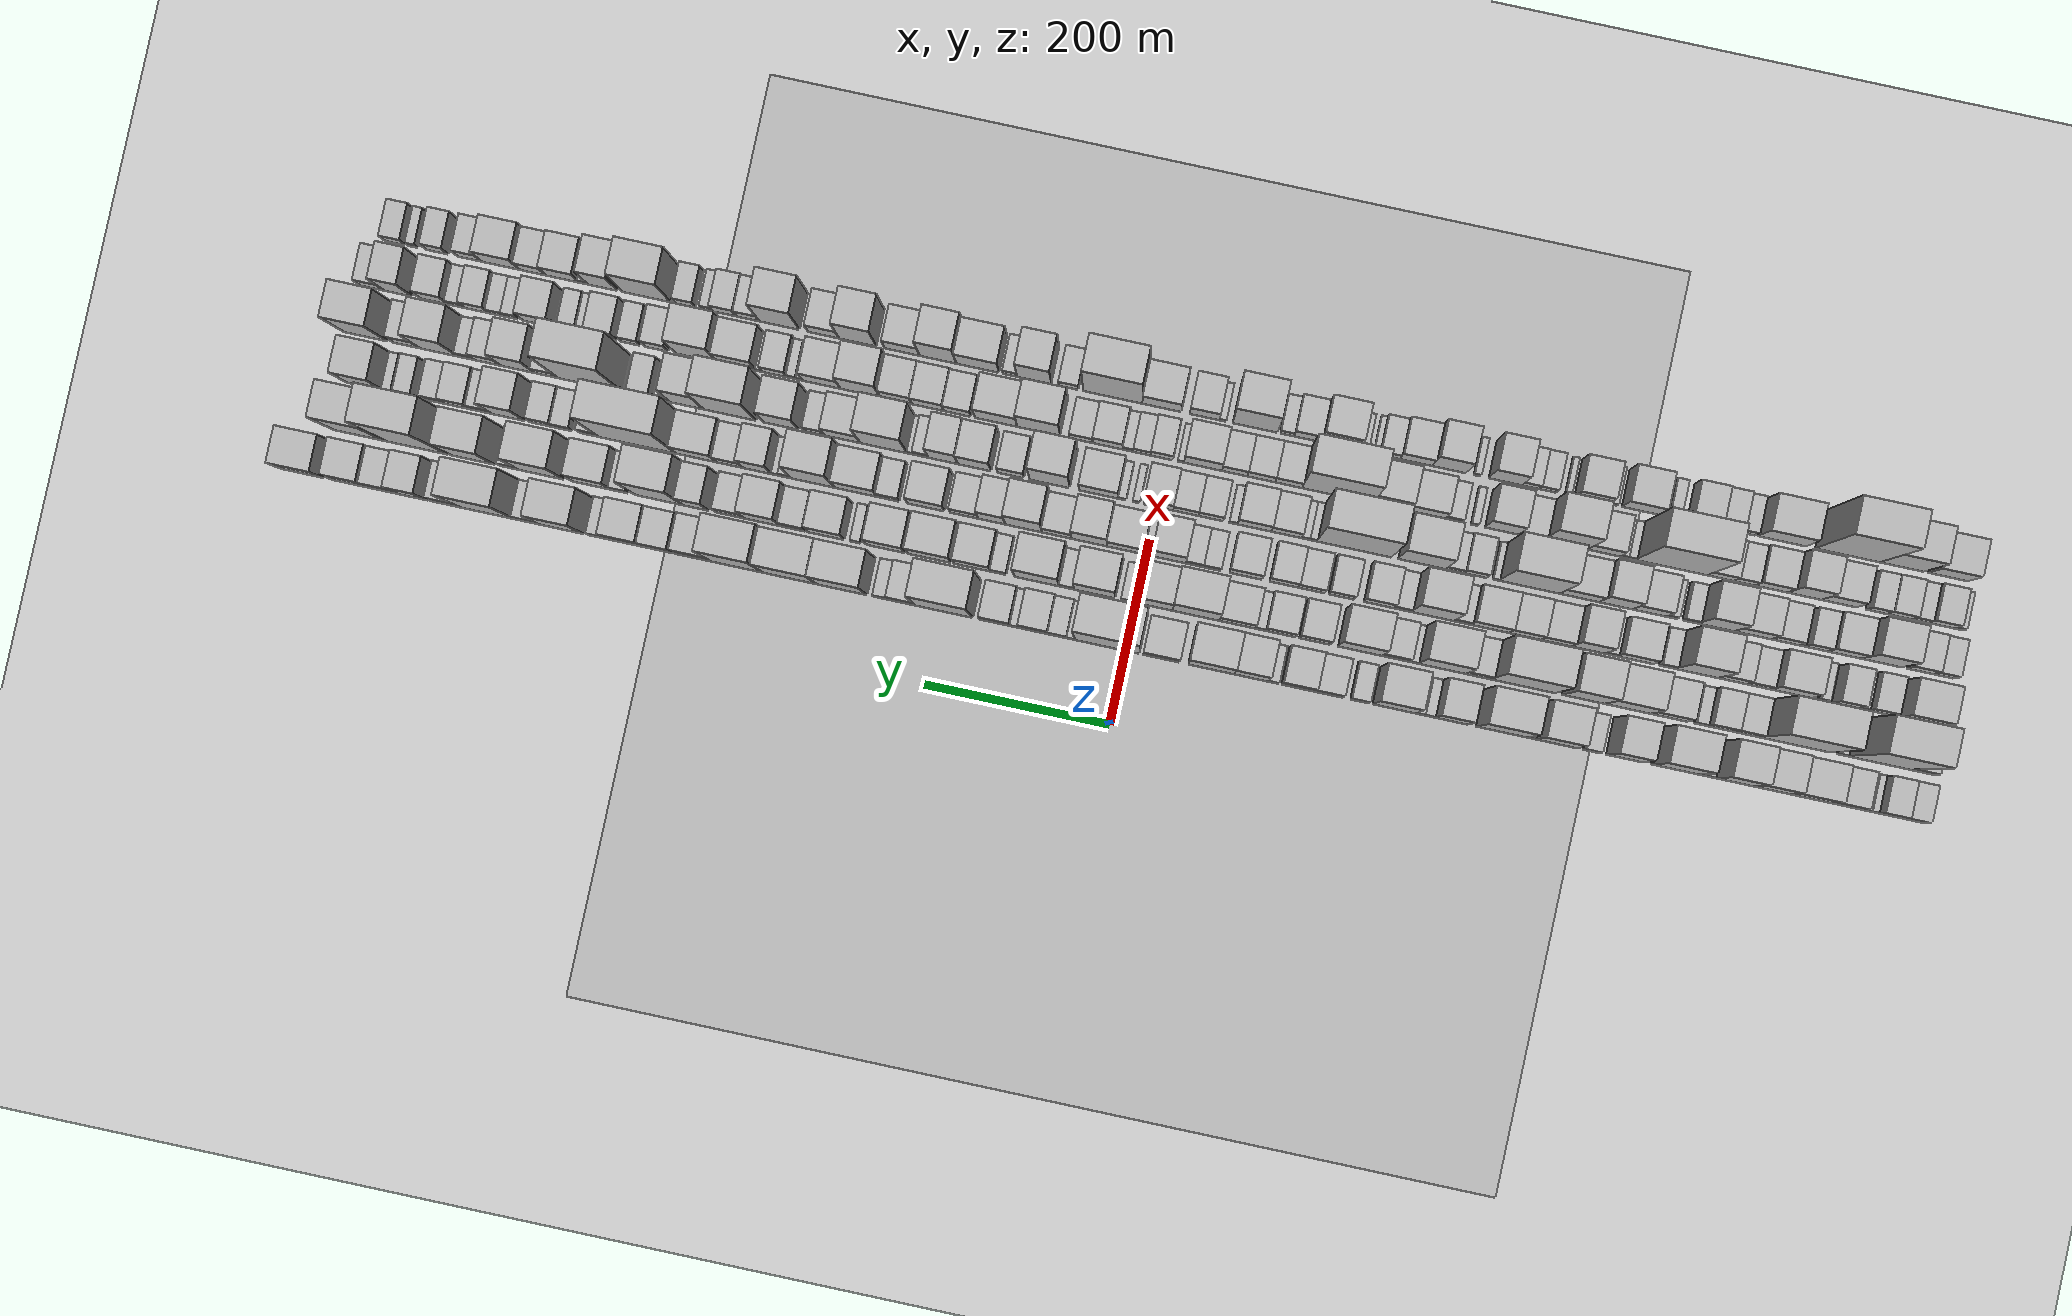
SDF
<?xml version="1.0" encoding="utf-8"?>

<sdf version="1.6">

   <world name="default">

      <gui fullscreen="0">

         <camera name="user_camera">

            <pose>-15 0 4.57585 0 0 0</pose>

            <view_controller>orbit</view_controller>

         </camera>

      </gui>

      <scene>

         <sky>

           <clouds>

             <speed>12</speed>

           </clouds>

         </sky>

         <ambient>0.4 0.4 0.4 1</ambient>

         <background>0.7 0.7 0.7 1</background>

         <shadows>1</shadows>

      </scene>

      <gravity>0 0 -9.8066</gravity>

      <magnetic_field>6e-06 2.3e-05 -4.2e-05</magnetic_field>

      <physics default="0" name="default_physics" type="ode">

         <ode>

            <solver>

               <type>quick</type>

               <iters>10</iters>

               <sor>1.0</sor>

               <use_dynamic_moi_rescaling>0</use_dynamic_moi_rescaling>

            </solver>

            <constraints>

               <cfm>0</cfm>

               <erp>0.2</erp>

               <contact_max_correcting_vel>100</contact_max_correcting_vel>

               <contact_surface_layer>0.001</contact_surface_layer>

            </constraints>

         </ode>

         <max_step_size>0.004</max_step_size>

         <real_time_factor>1</real_time_factor>

         <real_time_update_rate>250</real_time_update_rate>

      </physics>

      <light name="sun" type="directional">

         <cast_shadows>1</cast_shadows>

         <pose>0 0 10 0 0 0</pose>

         <diffuse>0.8 0.8 0.8 1</diffuse>

         <specular>0.2 0.2 0.2 1</specular>

         <attenuation>

            <range>1000</range>

            <constant>0.9</constant>

            <linear>0.01</linear>

            <quadratic>0.001</quadratic>

         </attenuation>

         <direction>-0.5 0.1 -0.9</direction>

      </light>

      <include>

         <name>ground_plane_1</name>

         <uri>model://HANNAS_ground_plane</uri>

         <pose>0 0 0  0 0 0</pose>

      </include>

      <include>

         <name>ground_plane_2</name>

         <uri>model://HANNAS_ground_plane</uri>

         <pose>100 0 0  0 0 0</pose>

      </include>

      <model name="building_1">

         <static>1</static>

         <pose frame="">100.0000 -848.3081 0 0.000000 0.000000 0.000000</pose>

         <link name="link">

            <pose frame="">0 0 22.50 0 0 0</pose>

            <collision name="collision">

               <geometry>

                  <box>

                     <size>40.0000 23.3837 45.0000</size>

                  </box>

               </geometry>

               <max_contacts>10</max_contacts>

               <surface>

                  <contact>

                     <ode/>

                  </contact>

                  <bounce/>

                  <friction>

                     <torsional>

                        <ode/>

                     </torsional>

                     <ode/>

                  </friction>

               </surface>

            </collision>

            <visual name="visual">

               <cast_shadows>0</cast_shadows>

               <geometry>

                  <box>

                     <size>40.0000 23.3837 45.0000</size>

                  </box>

               </geometry>

               <material>

                  <script>

                     <uri>model://HANNAS_wall/materials/scripts</uri>

                     <uri>model://HANNAS_wall/materials/textures</uri>

                     <name>vrc/HANNAS_wall</name>

                  </script>

               </material>

            </visual>

            <self_collide>0</self_collide>

            <enable_wind>0</enable_wind>

            <kinematic>0</kinematic>

         </link>

      </model>

      <model name="building_2">

         <static>1</static>

         <pose frame="">100.0000 -822.9420 0 0.000000 0.000000 0.000000</pose>

         <link name="link">

            <pose frame="">0 0 25.50 0 0 0</pose>

            <collision name="collision">

               <geometry>

                  <box>

                     <size>40.0000 27.3487 51.0000</size>

                  </box>

               </geometry>

               <max_contacts>10</max_contacts>

               <surface>

                  <contact>

                     <ode/>

                  </contact>

                  <bounce/>

                  <friction>

                     <torsional>

                        <ode/>

                     </torsional>

                     <ode/>

                  </friction>

               </surface>

            </collision>

            <visual name="visual">

               <cast_shadows>0</cast_shadows>

               <geometry>

                  <box>

                     <size>40.0000 27.3487 51.0000</size>

                  </box>

               </geometry>

               <material>

                  <script>

                     <uri>model://HANNAS_wall/materials/scripts</uri>

                     <uri>model://HANNAS_wall/materials/textures</uri>

                     <name>vrc/HANNAS_wall</name>

                  </script>

               </material>

            </visual>

            <self_collide>0</self_collide>

            <enable_wind>0</enable_wind>

            <kinematic>0</kinematic>

         </link>

      </model>

      <model name="building_3">

         <static>1</static>

         <pose frame="">100.0000 -805.3015 0 0.000000 0.000000 0.000000</pose>

         <link name="link">

            <pose frame="">0 0 9.00 0 0 0</pose>

            <collision name="collision">

               <geometry>

                  <box>

                     <size>40.0000 7.9323 18.0000</size>

                  </box>

               </geometry>

               <max_contacts>10</max_contacts>

               <surface>

                  <contact>

                     <ode/>

                  </contact>

                  <bounce/>

                  <friction>

                     <torsional>

                        <ode/>

                     </torsional>

                     <ode/>

                  </friction>

               </surface>

            </collision>

            <visual name="visual">

               <cast_shadows>0</cast_shadows>

               <geometry>

                  <box>

                     <size>40.0000 7.9323 18.0000</size>

                  </box>

               </geometry>

               <material>

                  <script>

                     <uri>model://HANNAS_wall/materials/scripts</uri>

                     <uri>model://HANNAS_wall/materials/textures</uri>

                     <name>vrc/HANNAS_wall</name>

                  </script>

               </material>

            </visual>

            <self_collide>0</self_collide>

            <enable_wind>0</enable_wind>

            <kinematic>0</kinematic>

         </link>

      </model>

      <model name="building_4">

         <static>1</static>

         <pose frame="">100.0000 -796.9766 0 0.000000 0.000000 0.000000</pose>

         <link name="link">

            <pose frame="">0 0 10.50 0 0 0</pose>

            <collision name="collision">

               <geometry>

                  <box>

                     <size>40.0000 8.7175 21.0000</size>

                  </box>

               </geometry>

               <max_contacts>10</max_contacts>

               <surface>

                  <contact>

                     <ode/>

                  </contact>

                  <bounce/>

                  <friction>

                     <torsional>

                        <ode/>

                     </torsional>

                     <ode/>

                  </friction>

               </surface>

            </collision>

            <visual name="visual">

               <cast_shadows>0</cast_shadows>

               <geometry>

                  <box>

                     <size>40.0000 8.7175 21.0000</size>

                  </box>

               </geometry>

               <material>

                  <script>

                     <uri>model://HANNAS_wall/materials/scripts</uri>

                     <uri>model://HANNAS_wall/materials/textures</uri>

                     <name>vrc/HANNAS_wall</name>

                  </script>

               </material>

            </visual>

            <self_collide>0</self_collide>

            <enable_wind>0</enable_wind>

            <kinematic>0</kinematic>

         </link>

      </model>

      <model name="building_5">

         <static>1</static>

         <pose frame="">100.0000 -776.7203 0 0.000000 0.000000 0.000000</pose>

         <link name="link">

            <pose frame="">0 0 28.50 0 0 0</pose>

            <collision name="collision">

               <geometry>

                  <box>

                     <size>40.0000 31.7950 57.0000</size>

                  </box>

               </geometry>

               <max_contacts>10</max_contacts>

               <surface>

                  <contact>

                     <ode/>

                  </contact>

                  <bounce/>

                  <friction>

                     <torsional>

                        <ode/>

                     </torsional>

                     <ode/>

                  </friction>

               </surface>

            </collision>

            <visual name="visual">

               <cast_shadows>0</cast_shadows>

               <geometry>

                  <box>

                     <size>40.0000 31.7950 57.0000</size>

                  </box>

               </geometry>

               <material>

                  <script>

                     <uri>model://HANNAS_wall/materials/scripts</uri>

                     <uri>model://HANNAS_wall/materials/textures</uri>

                     <name>vrc/HANNAS_wall</name>

                  </script>

               </material>

            </visual>

            <self_collide>0</self_collide>

            <enable_wind>0</enable_wind>

            <kinematic>0</kinematic>

         </link>

      </model>

      <model name="building_6">

         <static>1</static>

         <pose frame="">100.0000 -737.4847 0 0.000000 0.000000 0.000000</pose>

         <link name="link">

            <pose frame="">0 0 40.50 0 0 0</pose>

            <collision name="collision">

               <geometry>

                  <box>

                     <size>40.0000 46.6762 81.0000</size>

                  </box>

               </geometry>

               <max_contacts>10</max_contacts>

               <surface>

                  <contact>

                     <ode/>

                  </contact>

                  <bounce/>

                  <friction>

                     <torsional>

                        <ode/>

                     </torsional>

                     <ode/>

                  </friction>

               </surface>

            </collision>

            <visual name="visual">

               <cast_shadows>0</cast_shadows>

               <geometry>

                  <box>

                     <size>40.0000 46.6762 81.0000</size>

                  </box>

               </geometry>

               <material>

                  <script>

                     <uri>model://HANNAS_wall/materials/scripts</uri>

                     <uri>model://HANNAS_wall/materials/textures</uri>

                     <name>vrc/HANNAS_wall</name>

                  </script>

               </material>

            </visual>

            <self_collide>0</self_collide>

            <enable_wind>0</enable_wind>

            <kinematic>0</kinematic>

         </link>

      </model>

      <model name="building_7">

         <static>1</static>

         <pose frame="">100.0000 -694.6013 0 0.000000 0.000000 0.000000</pose>

         <link name="link">

            <pose frame="">0 0 52.50 0 0 0</pose>

            <collision name="collision">

               <geometry>

                  <box>

                     <size>40.0000 39.0908 105.0000</size>

                  </box>

               </geometry>

               <max_contacts>10</max_contacts>

               <surface>

                  <contact>

                     <ode/>

                  </contact>

                  <bounce/>

                  <friction>

                     <torsional>

                        <ode/>

                     </torsional>

                     <ode/>

                  </friction>

               </surface>

            </collision>

            <visual name="visual">

               <cast_shadows>0</cast_shadows>

               <geometry>

                  <box>

                     <size>40.0000 39.0908 105.0000</size>

                  </box>

               </geometry>

               <material>

                  <script>

                     <uri>model://HANNAS_wall/materials/scripts</uri>

                     <uri>model://HANNAS_wall/materials/textures</uri>

                     <name>vrc/HANNAS_wall</name>

                  </script>

               </material>

            </visual>

            <self_collide>0</self_collide>

            <enable_wind>0</enable_wind>

            <kinematic>0</kinematic>

         </link>

      </model>

      <model name="building_8">

         <static>1</static>

         <pose frame="">100.0000 -654.4463 0 0.000000 0.000000 0.000000</pose>

         <link name="link">

            <pose frame="">0 0 64.50 0 0 0</pose>

            <collision name="collision">

               <geometry>

                  <box>

                     <size>40.0000 41.2190 129.0000</size>

                  </box>

               </geometry>

               <max_contacts>10</max_contacts>

               <surface>

                  <contact>

                     <ode/>

                  </contact>

                  <bounce/>

                  <friction>

                     <torsional>

                        <ode/>

                     </torsional>

                     <ode/>

                  </friction>

               </surface>

            </collision>

            <visual name="visual">

               <cast_shadows>0</cast_shadows>

               <geometry>

                  <box>

                     <size>40.0000 41.2190 129.0000</size>

                  </box>

               </geometry>

               <material>

                  <script>

                     <uri>model://HANNAS_wall/materials/scripts</uri>

                     <uri>model://HANNAS_wall/materials/textures</uri>

                     <name>vrc/HANNAS_wall</name>

                  </script>

               </material>

            </visual>

            <self_collide>0</self_collide>

            <enable_wind>0</enable_wind>

            <kinematic>0</kinematic>

         </link>

      </model>

      <model name="building_9">

         <static>1</static>

         <pose frame="">100.0000 -629.4320 0 0.000000 0.000000 0.000000</pose>

         <link name="link">

            <pose frame="">0 0 9.00 0 0 0</pose>

            <collision name="collision">

               <geometry>

                  <box>

                     <size>40.0000 8.8096 18.0000</size>

                  </box>

               </geometry>

               <max_contacts>10</max_contacts>

               <surface>

                  <contact>

                     <ode/>

                  </contact>

                  <bounce/>

                  <friction>

                     <torsional>

                        <ode/>

                     </torsional>

                     <ode/>

                  </friction>

               </surface>

            </collision>

            <visual name="visual">

               <cast_shadows>0</cast_shadows>

               <geometry>

                  <box>

                     <size>40.0000 8.8096 18.0000</size>

                  </box>

               </geometry>

               <material>

                  <script>

                     <uri>model://HANNAS_wall/materials/scripts</uri>

                     <uri>model://HANNAS_wall/materials/textures</uri>

                     <name>vrc/HANNAS_wall</name>

                  </script>

               </material>

            </visual>

            <self_collide>0</self_collide>

            <enable_wind>0</enable_wind>

            <kinematic>0</kinematic>

         </link>

      </model>

      <model name="building_10">

         <static>1</static>

         <pose frame="">100.0000 -620.8518 0 0.000000 0.000000 0.000000</pose>

         <link name="link">

            <pose frame="">0 0 9.00 0 0 0</pose>

            <collision name="collision">

               <geometry>

                  <box>

                     <size>40.0000 8.3508 18.0000</size>

                  </box>

               </geometry>

               <max_contacts>10</max_contacts>

               <surface>

                  <contact>

                     <ode/>

                  </contact>

                  <bounce/>

                  <friction>

                     <torsional>

                        <ode/>

                     </torsional>

                     <ode/>

                  </friction>

               </surface>

            </collision>

            <visual name="visual">

               <cast_shadows>0</cast_shadows>

               <geometry>

                  <box>

                     <size>40.0000 8.3508 18.0000</size>

                  </box>

               </geometry>

               <material>

                  <script>

                     <uri>model://HANNAS_wall/materials/scripts</uri>

                     <uri>model://HANNAS_wall/materials/textures</uri>

                     <name>vrc/HANNAS_wall</name>

                  </script>

               </material>

            </visual>

            <self_collide>0</self_collide>

            <enable_wind>0</enable_wind>

            <kinematic>0</kinematic>

         </link>

      </model>

      <model name="building_11">

         <static>1</static>

         <pose frame="">100.0000 -591.3180 0 0.000000 0.000000 0.000000</pose>

         <link name="link">

            <pose frame="">0 0 70.50 0 0 0</pose>

            <collision name="collision">

               <geometry>

                  <box>

                     <size>40.0000 50.7169 141.0000</size>

                  </box>

               </geometry>

               <max_contacts>10</max_contacts>

               <surface>

                  <contact>

                     <ode/>

                  </contact>

                  <bounce/>

                  <friction>

                     <torsional>

                        <ode/>

                     </torsional>

                     <ode/>

                  </friction>

               </surface>

            </collision>

            <visual name="visual">

               <cast_shadows>0</cast_shadows>

               <geometry>

                  <box>

                     <size>40.0000 50.7169 141.0000</size>

                  </box>

               </geometry>

               <material>

                  <script>

                     <uri>model://HANNAS_wall/materials/scripts</uri>

                     <uri>model://HANNAS_wall/materials/textures</uri>

                     <name>vrc/HANNAS_wall</name>

                  </script>

               </material>

            </visual>

            <self_collide>0</self_collide>

            <enable_wind>0</enable_wind>

            <kinematic>0</kinematic>

         </link>

      </model>

      <model name="building_12">

         <static>1</static>

         <pose frame="">100.0000 -536.8043 0 0.000000 0.000000 0.000000</pose>

         <link name="link">

            <pose frame="">0 0 58.50 0 0 0</pose>

            <collision name="collision">

               <geometry>

                  <box>

                     <size>40.0000 38.3103 117.0000</size>

                  </box>

               </geometry>

               <max_contacts>10</max_contacts>

               <surface>

                  <contact>

                     <ode/>

                  </contact>

                  <bounce/>

                  <friction>

                     <torsional>

                        <ode/>

                     </torsional>

                     <ode/>

                  </friction>

               </surface>

            </collision>

            <visual name="visual">

               <cast_shadows>0</cast_shadows>

               <geometry>

                  <box>

                     <size>40.0000 38.3103 117.0000</size>

                  </box>

               </geometry>

               <material>

                  <script>

                     <uri>model://HANNAS_wall/materials/scripts</uri>

                     <uri>model://HANNAS_wall/materials/textures</uri>

                     <name>vrc/HANNAS_wall</name>

                  </script>

               </material>

            </visual>

            <self_collide>0</self_collide>

            <enable_wind>0</enable_wind>

            <kinematic>0</kinematic>

         </link>

      </model>

      <model name="building_13">

         <static>1</static>

         <pose frame="">100.0000 -501.3110 0 0.000000 0.000000 0.000000</pose>

         <link name="link">

            <pose frame="">0 0 16.50 0 0 0</pose>

            <collision name="collision">

               <geometry>

                  <box>

                     <size>40.0000 18.6764 33.0000</size>

                  </box>

               </geometry>

               <max_contacts>10</max_contacts>

               <surface>

                  <contact>

                     <ode/>

                  </contact>

                  <bounce/>

                  <friction>

                     <torsional>

                        <ode/>

                     </torsional>

                     <ode/>

                  </friction>

               </surface>

            </collision>

            <visual name="visual">

               <cast_shadows>0</cast_shadows>

               <geometry>

                  <box>

                     <size>40.0000 18.6764 33.0000</size>

                  </box>

               </geometry>

               <material>

                  <script>

                     <uri>model://HANNAS_wall/materials/scripts</uri>

                     <uri>model://HANNAS_wall/materials/textures</uri>

                     <name>vrc/HANNAS_wall</name>

                  </script>

               </material>

            </visual>

            <self_collide>0</self_collide>

            <enable_wind>0</enable_wind>

            <kinematic>0</kinematic>

         </link>

      </model>

      <model name="building_14">

         <static>1</static>

         <pose frame="">100.0000 -462.9899 0 0.000000 0.000000 0.000000</pose>

         <link name="link">

            <pose frame="">0 0 58.50 0 0 0</pose>

            <collision name="collision">

               <geometry>

                  <box>

                     <size>40.0000 43.9658 117.0000</size>

                  </box>

               </geometry>

               <max_contacts>10</max_contacts>

               <surface>

                  <contact>

                     <ode/>

                  </contact>

                  <bounce/>

                  <friction>

                     <torsional>

                        <ode/>

                     </torsional>

                     <ode/>

                  </friction>

               </surface>

            </collision>

            <visual name="visual">

               <cast_shadows>0</cast_shadows>

               <geometry>

                  <box>

                     <size>40.0000 43.9658 117.0000</size>

                  </box>

               </geometry>

               <material>

                  <script>

                     <uri>model://HANNAS_wall/materials/scripts</uri>

                     <uri>model://HANNAS_wall/materials/textures</uri>

                     <name>vrc/HANNAS_wall</name>

                  </script>

               </material>

            </visual>

            <self_collide>0</self_collide>

            <enable_wind>0</enable_wind>

            <kinematic>0</kinematic>

         </link>

      </model>

      <model name="building_15">

         <static>1</static>

         <pose frame="">100.0000 -436.5544 0 0.000000 0.000000 0.000000</pose>

         <link name="link">

            <pose frame="">0 0 10.50 0 0 0</pose>

            <collision name="collision">

               <geometry>

                  <box>

                     <size>40.0000 8.9052 21.0000</size>

                  </box>

               </geometry>

               <max_contacts>10</max_contacts>

               <surface>

                  <contact>

                     <ode/>

                  </contact>

                  <bounce/>

                  <friction>

                     <torsional>

                        <ode/>

                     </torsional>

                     <ode/>

                  </friction>

               </surface>

            </collision>

            <visual name="visual">

               <cast_shadows>0</cast_shadows>

               <geometry>

                  <box>

                     <size>40.0000 8.9052 21.0000</size>

                  </box>

               </geometry>

               <material>

                  <script>

                     <uri>model://HANNAS_wall/materials/scripts</uri>

                     <uri>model://HANNAS_wall/materials/textures</uri>

                     <name>vrc/HANNAS_wall</name>

                  </script>

               </material>

            </visual>

            <self_collide>0</self_collide>

            <enable_wind>0</enable_wind>

            <kinematic>0</kinematic>

         </link>

      </model>

      <model name="building_16">

         <static>1</static>

         <pose frame="">100.0000 -404.7646 0 0.000000 0.000000 0.000000</pose>

         <link name="link">

            <pose frame="">0 0 72.00 0 0 0</pose>

            <collision name="collision">

               <geometry>

                  <box>

                     <size>40.0000 54.6743 144.0000</size>

                  </box>

               </geometry>

               <max_contacts>10</max_contacts>

               <surface>

                  <contact>

                     <ode/>

                  </contact>

                  <bounce/>

                  <friction>

                     <torsional>

                        <ode/>

                     </torsional>

                     <ode/>

                  </friction>

               </surface>

            </collision>

            <visual name="visual">

               <cast_shadows>0</cast_shadows>

               <geometry>

                  <box>

                     <size>40.0000 54.6743 144.0000</size>

                  </box>

               </geometry>

               <material>

                  <script>

                     <uri>model://HANNAS_wall/materials/scripts</uri>

                     <uri>model://HANNAS_wall/materials/textures</uri>

                     <name>vrc/HANNAS_wall</name>

                  </script>

               </material>

            </visual>

            <self_collide>0</self_collide>

            <enable_wind>0</enable_wind>

            <kinematic>0</kinematic>

         </link>

      </model>

      <model name="building_17">

         <static>1</static>

         <pose frame="">100.0000 -350.3334 0 0.000000 0.000000 0.000000</pose>

         <link name="link">

            <pose frame="">0 0 51.00 0 0 0</pose>

            <collision name="collision">

               <geometry>

                  <box>

                     <size>40.0000 36.1881 102.0000</size>

                  </box>

               </geometry>

               <max_contacts>10</max_contacts>

               <surface>

                  <contact>

                     <ode/>

                  </contact>

                  <bounce/>

                  <friction>

                     <torsional>

                        <ode/>

                     </torsional>

                     <ode/>

                  </friction>

               </surface>

            </collision>

            <visual name="visual">

               <cast_shadows>0</cast_shadows>

               <geometry>

                  <box>

                     <size>40.0000 36.1881 102.0000</size>

                  </box>

               </geometry>

               <material>

                  <script>

                     <uri>model://HANNAS_wall/materials/scripts</uri>

                     <uri>model://HANNAS_wall/materials/textures</uri>

                     <name>vrc/HANNAS_wall</name>

                  </script>

               </material>

            </visual>

            <self_collide>0</self_collide>

            <enable_wind>0</enable_wind>

            <kinematic>0</kinematic>

         </link>

      </model>

      <model name="building_18">

         <static>1</static>

         <pose frame="">100.0000 -326.8579 0 0.000000 0.000000 0.000000</pose>

         <link name="link">

            <pose frame="">0 0 12.00 0 0 0</pose>

            <collision name="collision">

               <geometry>

                  <box>

                     <size>40.0000 10.7630 24.0000</size>

                  </box>

               </geometry>

               <max_contacts>10</max_contacts>

               <surface>

                  <contact>

                     <ode/>

                  </contact>

                  <bounce/>

                  <friction>

                     <torsional>

                        <ode/>

                     </torsional>

                     <ode/>

                  </friction>

               </surface>

            </collision>

            <visual name="visual">

               <cast_shadows>0</cast_shadows>

               <geometry>

                  <box>

                     <size>40.0000 10.7630 24.0000</size>

                  </box>

               </geometry>

               <material>

                  <script>

                     <uri>model://HANNAS_wall/materials/scripts</uri>

                     <uri>model://HANNAS_wall/materials/textures</uri>

                     <name>vrc/HANNAS_wall</name>

                  </script>

               </material>

            </visual>

            <self_collide>0</self_collide>

            <enable_wind>0</enable_wind>

            <kinematic>0</kinematic>

         </link>

      </model>

      <model name="building_19">

         <static>1</static>

         <pose frame="">100.0000 -316.5767 0 0.000000 0.000000 0.000000</pose>

         <link name="link">

            <pose frame="">0 0 12.00 0 0 0</pose>

            <collision name="collision">

               <geometry>

                  <box>

                     <size>40.0000 9.7994 24.0000</size>

                  </box>

               </geometry>

               <max_contacts>10</max_contacts>

               <surface>

                  <contact>

                     <ode/>

                  </contact>

                  <bounce/>

                  <friction>

                     <torsional>

                        <ode/>

                     </torsional>

                     <ode/>

                  </friction>

               </surface>

            </collision>

            <visual name="visual">

               <cast_shadows>0</cast_shadows>

               <geometry>

                  <box>

                     <size>40.0000 9.7994 24.0000</size>

                  </box>

               </geometry>

               <material>

                  <script>

                     <uri>model://HANNAS_wall/materials/scripts</uri>

                     <uri>model://HANNAS_wall/materials/textures</uri>

                     <name>vrc/HANNAS_wall</name>

                  </script>

               </material>

            </visual>

            <self_collide>0</self_collide>

            <enable_wind>0</enable_wind>

            <kinematic>0</kinematic>

         </link>

      </model>

      <model name="building_20">

         <static>1</static>

         <pose frame="">100.0000 -288.7271 0 0.000000 0.000000 0.000000</pose>

         <link name="link">

            <pose frame="">0 0 67.50 0 0 0</pose>

            <collision name="collision">

               <geometry>

                  <box>

                     <size>40.0000 45.8998 135.0000</size>

                  </box>

               </geometry>

               <max_contacts>10</max_contacts>

               <surface>

                  <contact>

                     <ode/>

                  </contact>

                  <bounce/>

                  <friction>

                     <torsional>

                        <ode/>

                     </torsional>

                     <ode/>

                  </friction>

               </surface>

            </collision>

            <visual name="visual">

               <cast_shadows>0</cast_shadows>

               <geometry>

                  <box>

                     <size>40.0000 45.8998 135.0000</size>

                  </box>

               </geometry>

               <material>

                  <script>

                     <uri>model://HANNAS_wall/materials/scripts</uri>

                     <uri>model://HANNAS_wall/materials/textures</uri>

                     <name>vrc/HANNAS_wall</name>

                  </script>

               </material>

            </visual>

            <self_collide>0</self_collide>

            <enable_wind>0</enable_wind>

            <kinematic>0</kinematic>

         </link>

      </model>

      <model name="building_21">

         <static>1</static>

         <pose frame="">100.0000 -251.6912 0 0.000000 0.000000 0.000000</pose>

         <link name="link">

            <pose frame="">0 0 19.50 0 0 0</pose>

            <collision name="collision">

               <geometry>

                  <box>

                     <size>40.0000 20.1721 39.0000</size>

                  </box>

               </geometry>

               <max_contacts>10</max_contacts>

               <surface>

                  <contact>

                     <ode/>

                  </contact>

                  <bounce/>

                  <friction>

                     <torsional>

                        <ode/>

                     </torsional>

                     <ode/>

                  </friction>

               </surface>

            </collision>

            <visual name="visual">

               <cast_shadows>0</cast_shadows>

               <geometry>

                  <box>

                     <size>40.0000 20.1721 39.0000</size>

                  </box>

               </geometry>

               <material>

                  <script>

                     <uri>model://HANNAS_wall/materials/scripts</uri>

                     <uri>model://HANNAS_wall/materials/textures</uri>

                     <name>vrc/HANNAS_wall</name>

                  </script>

               </material>

            </visual>

            <self_collide>0</self_collide>

            <enable_wind>0</enable_wind>

            <kinematic>0</kinematic>

         </link>

      </model>

      <model name="building_22">

         <static>1</static>

         <pose frame="">100.0000 -218.7330 0 0.000000 0.000000 0.000000</pose>

         <link name="link">

            <pose frame="">0 0 27.00 0 0 0</pose>

            <collision name="collision">

               <geometry>

                  <box>

                     <size>40.0000 29.7443 54.0000</size>

                  </box>

               </geometry>

               <max_contacts>10</max_contacts>

               <surface>

                  <contact>

                     <ode/>

                  </contact>

                  <bounce/>

                  <friction>

                     <torsional>

                        <ode/>

                     </torsional>

                     <ode/>

                  </friction>

               </surface>

            </collision>

            <visual name="visual">

               <cast_shadows>0</cast_shadows>

               <geometry>

                  <box>

                     <size>40.0000 29.7443 54.0000</size>

                  </box>

               </geometry>

               <material>

                  <script>

                     <uri>model://HANNAS_wall/materials/scripts</uri>

                     <uri>model://HANNAS_wall/materials/textures</uri>

                     <name>vrc/HANNAS_wall</name>

                  </script>

               </material>

            </visual>

            <self_collide>0</self_collide>

            <enable_wind>0</enable_wind>

            <kinematic>0</kinematic>

         </link>

      </model>

      <model name="building_23">

         <static>1</static>

         <pose frame="">100.0000 -185.6382 0 0.000000 0.000000 0.000000</pose>

         <link name="link">

            <pose frame="">0 0 34.50 0 0 0</pose>

            <collision name="collision">

               <geometry>

                  <box>

                     <size>40.0000 36.4452 69.0000</size>

                  </box>

               </geometry>

               <max_contacts>10</max_contacts>

               <surface>

                  <contact>

                     <ode/>

                  </contact>

                  <bounce/>

                  <friction>

                     <torsional>

                        <ode/>

                     </torsional>

                     <ode/>

                  </friction>

               </surface>

            </collision>

            <visual name="visual">

               <cast_shadows>0</cast_shadows>

               <geometry>

                  <box>

                     <size>40.0000 36.4452 69.0000</size>

                  </box>

               </geometry>

               <material>

                  <script>

                     <uri>model://HANNAS_wall/materials/scripts</uri>

                     <uri>model://HANNAS_wall/materials/textures</uri>

                     <name>vrc/HANNAS_wall</name>

                  </script>

               </material>

            </visual>

            <self_collide>0</self_collide>

            <enable_wind>0</enable_wind>

            <kinematic>0</kinematic>

         </link>

      </model>

      <model name="building_24">

         <static>1</static>

         <pose frame="">100.0000 -158.5348 0 0.000000 0.000000 0.000000</pose>

         <link name="link">

            <pose frame="">0 0 13.50 0 0 0</pose>

            <collision name="collision">

               <geometry>

                  <box>

                     <size>40.0000 11.7615 27.0000</size>

                  </box>

               </geometry>

               <max_contacts>10</max_contacts>

               <surface>

                  <contact>

                     <ode/>

                  </contact>

                  <bounce/>

                  <friction>

                     <torsional>

                        <ode/>

                     </torsional>

                     <ode/>

                  </friction>

               </surface>

            </collision>

            <visual name="visual">

               <cast_shadows>0</cast_shadows>

               <geometry>

                  <box>

                     <size>40.0000 11.7615 27.0000</size>

                  </box>

               </geometry>

               <material>

                  <script>

                     <uri>model://HANNAS_wall/materials/scripts</uri>

                     <uri>model://HANNAS_wall/materials/textures</uri>

                     <name>vrc/HANNAS_wall</name>

                  </script>

               </material>

            </visual>

            <self_collide>0</self_collide>

            <enable_wind>0</enable_wind>

            <kinematic>0</kinematic>

         </link>

      </model>

      <model name="building_25">

         <static>1</static>

         <pose frame="">100.0000 -134.3453 0 0.000000 0.000000 0.000000</pose>

         <link name="link">

            <pose frame="">0 0 60.00 0 0 0</pose>

            <collision name="collision">

               <geometry>

                  <box>

                     <size>40.0000 36.6176 120.0000</size>

                  </box>

               </geometry>

               <max_contacts>10</max_contacts>

               <surface>

                  <contact>

                     <ode/>

                  </contact>

                  <bounce/>

                  <friction>

                     <torsional>

                        <ode/>

                     </torsional>

                     <ode/>

                  </friction>

               </surface>

            </collision>

            <visual name="visual">

               <cast_shadows>0</cast_shadows>

               <geometry>

                  <box>

                     <size>40.0000 36.6176 120.0000</size>

                  </box>

               </geometry>

               <material>

                  <script>

                     <uri>model://HANNAS_wall/materials/scripts</uri>

                     <uri>model://HANNAS_wall/materials/textures</uri>

                     <name>vrc/HANNAS_wall</name>

                  </script>

               </material>

            </visual>

            <self_collide>0</self_collide>

            <enable_wind>0</enable_wind>

            <kinematic>0</kinematic>

         </link>

      </model>

      <model name="building_26">

         <static>1</static>

         <pose frame="">100.0000 -91.2927 0 0.000000 0.000000 0.000000</pose>

         <link name="link">

            <pose frame="">0 0 64.50 0 0 0</pose>

            <collision name="collision">

               <geometry>

                  <box>

                     <size>40.0000 49.4875 129.0000</size>

                  </box>

               </geometry>

               <max_contacts>10</max_contacts>

               <surface>

                  <contact>

                     <ode/>

                  </contact>

                  <bounce/>

                  <friction>

                     <torsional>

                        <ode/>

                     </torsional>

                     <ode/>

                  </friction>

               </surface>

            </collision>

            <visual name="visual">

               <cast_shadows>0</cast_shadows>

               <geometry>

                  <box>

                     <size>40.0000 49.4875 129.0000</size>

                  </box>

               </geometry>

               <material>

                  <script>

                     <uri>model://HANNAS_wall/materials/scripts</uri>

                     <uri>model://HANNAS_wall/materials/textures</uri>

                     <name>vrc/HANNAS_wall</name>

                  </script>

               </material>

            </visual>

            <self_collide>0</self_collide>

            <enable_wind>0</enable_wind>

            <kinematic>0</kinematic>

         </link>

      </model>

      <model name="building_27">

         <static>1</static>

         <pose frame="">100.0000 -37.7616 0 0.000000 0.000000 0.000000</pose>

         <link name="link">

            <pose frame="">0 0 33.00 0 0 0</pose>

            <collision name="collision">

               <geometry>

                  <box>

                     <size>40.0000 39.5747 66.0000</size>

                  </box>

               </geometry>

               <max_contacts>10</max_contacts>

               <surface>

                  <contact>

                     <ode/>

                  </contact>

                  <bounce/>

                  <friction>

                     <torsional>

                        <ode/>

                     </torsional>

                     <ode/>

                  </friction>

               </surface>

            </collision>

            <visual name="visual">

               <cast_shadows>0</cast_shadows>

               <geometry>

                  <box>

                     <size>40.0000 39.5747 66.0000</size>

                  </box>

               </geometry>

               <material>

                  <script>

                     <uri>model://HANNAS_wall/materials/scripts</uri>

                     <uri>model://HANNAS_wall/materials/textures</uri>

                     <name>vrc/HANNAS_wall</name>

                  </script>

               </material>

            </visual>

            <self_collide>0</self_collide>

            <enable_wind>0</enable_wind>

            <kinematic>0</kinematic>

         </link>

      </model>

      <model name="building_28">

         <static>1</static>

         <pose frame="">100.0000 20.9367 0 0.000000 0.000000 0.000000</pose>

         <link name="link">

            <pose frame="">0 0 108.00 0 0 0</pose>

            <collision name="collision">

               <geometry>

                  <box>

                     <size>40.0000 69.8217 216.0000</size>

                  </box>

               </geometry>

               <max_contacts>10</max_contacts>

               <surface>

                  <contact>

                     <ode/>

                  </contact>

                  <bounce/>

                  <friction>

                     <torsional>

                        <ode/>

                     </torsional>

                     <ode/>

                  </friction>

               </surface>

            </collision>

            <visual name="visual">

               <cast_shadows>0</cast_shadows>

               <geometry>

                  <box>

                     <size>40.0000 69.8217 216.0000</size>

                  </box>

               </geometry>

               <material>

                  <script>

                     <uri>model://HANNAS_wall/materials/scripts</uri>

                     <uri>model://HANNAS_wall/materials/textures</uri>

                     <name>vrc/HANNAS_wall</name>

                  </script>

               </material>

            </visual>

            <self_collide>0</self_collide>

            <enable_wind>0</enable_wind>

            <kinematic>0</kinematic>

         </link>

      </model>

      <model name="building_29">

         <static>1</static>

         <pose frame="">100.0000 60.2967 0 0.000000 0.000000 0.000000</pose>

         <link name="link">

            <pose frame="">0 0 10.50 0 0 0</pose>

            <collision name="collision">

               <geometry>

                  <box>

                     <size>40.0000 8.8983 21.0000</size>

                  </box>

               </geometry>

               <max_contacts>10</max_contacts>

               <surface>

                  <contact>

                     <ode/>

                  </contact>

                  <bounce/>

                  <friction>

                     <torsional>

                        <ode/>

                     </torsional>

                     <ode/>

                  </friction>

               </surface>

            </collision>

            <visual name="visual">

               <cast_shadows>0</cast_shadows>

               <geometry>

                  <box>

                     <size>40.0000 8.8983 21.0000</size>

                  </box>

               </geometry>

               <material>

                  <script>

                     <uri>model://HANNAS_wall/materials/scripts</uri>

                     <uri>model://HANNAS_wall/materials/textures</uri>

                     <name>vrc/HANNAS_wall</name>

                  </script>

               </material>

            </visual>

            <self_collide>0</self_collide>

            <enable_wind>0</enable_wind>

            <kinematic>0</kinematic>

         </link>

      </model>

      <model name="building_30">

         <static>1</static>

         <pose frame="">100.0000 74.8387 0 0.000000 0.000000 0.000000</pose>

         <link name="link">

            <pose frame="">0 0 19.50 0 0 0</pose>

            <collision name="collision">

               <geometry>

                  <box>

                     <size>40.0000 20.1858 39.0000</size>

                  </box>

               </geometry>

               <max_contacts>10</max_contacts>

               <surface>

                  <contact>

                     <ode/>

                  </contact>

                  <bounce/>

                  <friction>

                     <torsional>

                        <ode/>

                     </torsional>

                     <ode/>

                  </friction>

               </surface>

            </collision>

            <visual name="visual">

               <cast_shadows>0</cast_shadows>

               <geometry>

                  <box>

                     <size>40.0000 20.1858 39.0000</size>

                  </box>

               </geometry>

               <material>

                  <script>

                     <uri>model://HANNAS_wall/materials/scripts</uri>

                     <uri>model://HANNAS_wall/materials/textures</uri>

                     <name>vrc/HANNAS_wall</name>

                  </script>

               </material>

            </visual>

            <self_collide>0</self_collide>

            <enable_wind>0</enable_wind>

            <kinematic>0</kinematic>

         </link>

      </model>

      <model name="building_31">

         <static>1</static>

         <pose frame="">100.0000 100.7868 0 0.000000 0.000000 0.000000</pose>

         <link name="link">

            <pose frame="">0 0 31.50 0 0 0</pose>

            <collision name="collision">

               <geometry>

                  <box>

                     <size>40.0000 31.7105 63.0000</size>

                  </box>

               </geometry>

               <max_contacts>10</max_contacts>

               <surface>

                  <contact>

                     <ode/>

                  </contact>

                  <bounce/>

                  <friction>

                     <torsional>

                        <ode/>

                     </torsional>

                     <ode/>

                  </friction>

               </surface>

            </collision>

            <visual name="visual">

               <cast_shadows>0</cast_shadows>

               <geometry>

                  <box>

                     <size>40.0000 31.7105 63.0000</size>

                  </box>

               </geometry>

               <material>

                  <script>

                     <uri>model://HANNAS_wall/materials/scripts</uri>

                     <uri>model://HANNAS_wall/materials/textures</uri>

                     <name>vrc/HANNAS_wall</name>

                  </script>

               </material>

            </visual>

            <self_collide>0</self_collide>

            <enable_wind>0</enable_wind>

            <kinematic>0</kinematic>

         </link>

      </model>

      <model name="building_32">

         <static>1</static>

         <pose frame="">100.0000 121.3697 0 0.000000 0.000000 0.000000</pose>

         <link name="link">

            <pose frame="">0 0 10.50 0 0 0</pose>

            <collision name="collision">

               <geometry>

                  <box>

                     <size>40.0000 9.4551 21.0000</size>

                  </box>

               </geometry>

               <max_contacts>10</max_contacts>

               <surface>

                  <contact>

                     <ode/>

                  </contact>

                  <bounce/>

                  <friction>

                     <torsional>

                        <ode/>

                     </torsional>

                     <ode/>

                  </friction>

               </surface>

            </collision>

            <visual name="visual">

               <cast_shadows>0</cast_shadows>

               <geometry>

                  <box>

                     <size>40.0000 9.4551 21.0000</size>

                  </box>

               </geometry>

               <material>

                  <script>

                     <uri>model://HANNAS_wall/materials/scripts</uri>

                     <uri>model://HANNAS_wall/materials/textures</uri>

                     <name>vrc/HANNAS_wall</name>

                  </script>

               </material>

            </visual>

            <self_collide>0</self_collide>

            <enable_wind>0</enable_wind>

            <kinematic>0</kinematic>

         </link>

      </model>

      <model name="building_33">

         <static>1</static>

         <pose frame="">100.0000 142.5122 0 0.000000 0.000000 0.000000</pose>

         <link name="link">

            <pose frame="">0 0 28.50 0 0 0</pose>

            <collision name="collision">

               <geometry>

                  <box>

                     <size>40.0000 32.8300 57.0000</size>

                  </box>

               </geometry>

               <max_contacts>10</max_contacts>

               <surface>

                  <contact>

                     <ode/>

                  </contact>

                  <bounce/>

                  <friction>

                     <torsional>

                        <ode/>

                     </torsional>

                     <ode/>

                  </friction>

               </surface>

            </collision>

            <visual name="visual">

               <cast_shadows>0</cast_shadows>

               <geometry>

                  <box>

                     <size>40.0000 32.8300 57.0000</size>

                  </box>

               </geometry>

               <material>

                  <script>

                     <uri>model://HANNAS_wall/materials/scripts</uri>

                     <uri>model://HANNAS_wall/materials/textures</uri>

                     <name>vrc/HANNAS_wall</name>

                  </script>

               </material>

            </visual>

            <self_collide>0</self_collide>

            <enable_wind>0</enable_wind>

            <kinematic>0</kinematic>

         </link>

      </model>

      <model name="building_34">

         <static>1</static>

         <pose frame="">100.0000 197.2322 0 0.000000 0.000000 0.000000</pose>

         <link name="link">

            <pose frame="">0 0 94.50 0 0 0</pose>

            <collision name="collision">

               <geometry>

                  <box>

                     <size>40.0000 62.6101 189.0000</size>

                  </box>

               </geometry>

               <max_contacts>10</max_contacts>

               <surface>

                  <contact>

                     <ode/>

                  </contact>

                  <bounce/>

                  <friction>

                     <torsional>

                        <ode/>

                     </torsional>

                     <ode/>

                  </friction>

               </surface>

            </collision>

            <visual name="visual">

               <cast_shadows>0</cast_shadows>

               <geometry>

                  <box>

                     <size>40.0000 62.6101 189.0000</size>

                  </box>

               </geometry>

               <material>

                  <script>

                     <uri>model://HANNAS_wall/materials/scripts</uri>

                     <uri>model://HANNAS_wall/materials/textures</uri>

                     <name>vrc/HANNAS_wall</name>

                  </script>

               </material>

            </visual>

            <self_collide>0</self_collide>

            <enable_wind>0</enable_wind>

            <kinematic>0</kinematic>

         </link>

      </model>

      <model name="building_35">

         <static>1</static>

         <pose frame="">100.0000 243.2534 0 0.000000 0.000000 0.000000</pose>

         <link name="link">

            <pose frame="">0 0 27.00 0 0 0</pose>

            <collision name="collision">

               <geometry>

                  <box>

                     <size>40.0000 29.4323 54.0000</size>

                  </box>

               </geometry>

               <max_contacts>10</max_contacts>

               <surface>

                  <contact>

                     <ode/>

                  </contact>

                  <bounce/>

                  <friction>

                     <torsional>

                        <ode/>

                     </torsional>

                     <ode/>

                  </friction>

               </surface>

            </collision>

            <visual name="visual">

               <cast_shadows>0</cast_shadows>

               <geometry>

                  <box>

                     <size>40.0000 29.4323 54.0000</size>

                  </box>

               </geometry>

               <material>

                  <script>

                     <uri>model://HANNAS_wall/materials/scripts</uri>

                     <uri>model://HANNAS_wall/materials/textures</uri>

                     <name>vrc/HANNAS_wall</name>

                  </script>

               </material>

            </visual>

            <self_collide>0</self_collide>

            <enable_wind>0</enable_wind>

            <kinematic>0</kinematic>

         </link>

      </model>

      <model name="building_36">

         <static>1</static>

         <pose frame="">100.0000 265.6831 0 0.000000 0.000000 0.000000</pose>

         <link name="link">

            <pose frame="">0 0 15.00 0 0 0</pose>

            <collision name="collision">

               <geometry>

                  <box>

                     <size>40.0000 15.4270 30.0000</size>

                  </box>

               </geometry>

               <max_contacts>10</max_contacts>

               <surface>

                  <contact>

                     <ode/>

                  </contact>

                  <bounce/>

                  <friction>

                     <torsional>

                        <ode/>

                     </torsional>

                     <ode/>

                  </friction>

               </surface>

            </collision>

            <visual name="visual">

               <cast_shadows>0</cast_shadows>

               <geometry>

                  <box>

                     <size>40.0000 15.4270 30.0000</size>

                  </box>

               </geometry>

               <material>

                  <script>

                     <uri>model://HANNAS_wall/materials/scripts</uri>

                     <uri>model://HANNAS_wall/materials/textures</uri>

                     <name>vrc/HANNAS_wall</name>

                  </script>

               </material>

            </visual>

            <self_collide>0</self_collide>

            <enable_wind>0</enable_wind>

            <kinematic>0</kinematic>

         </link>

      </model>

      <model name="building_37">

         <static>1</static>

         <pose frame="">100.0000 307.7641 0 0.000000 0.000000 0.000000</pose>

         <link name="link">

            <pose frame="">0 0 72.00 0 0 0</pose>

            <collision name="collision">

               <geometry>

                  <box>

                     <size>40.0000 54.7350 144.0000</size>

                  </box>

               </geometry>

               <max_contacts>10</max_contacts>

               <surface>

                  <contact>

                     <ode/>

                  </contact>

                  <bounce/>

                  <friction>

                     <torsional>

                        <ode/>

                     </torsional>

                     <ode/>

                  </friction>

               </surface>

            </collision>

            <visual name="visual">

               <cast_shadows>0</cast_shadows>

               <geometry>

                  <box>

                     <size>40.0000 54.7350 144.0000</size>

                  </box>

               </geometry>

               <material>

                  <script>

                     <uri>model://HANNAS_wall/materials/scripts</uri>

                     <uri>model://HANNAS_wall/materials/textures</uri>

                     <name>vrc/HANNAS_wall</name>

                  </script>

               </material>

            </visual>

            <self_collide>0</self_collide>

            <enable_wind>0</enable_wind>

            <kinematic>0</kinematic>

         </link>

      </model>

      <model name="building_38">

         <static>1</static>

         <pose frame="">100.0000 364.0918 0 0.000000 0.000000 0.000000</pose>

         <link name="link">

            <pose frame="">0 0 73.50 0 0 0</pose>

            <collision name="collision">

               <geometry>

                  <box>

                     <size>40.0000 57.9204 147.0000</size>

                  </box>

               </geometry>

               <max_contacts>10</max_contacts>

               <surface>

                  <contact>

                     <ode/>

                  </contact>

                  <bounce/>

                  <friction>

                     <torsional>

                        <ode/>

                     </torsional>

                     <ode/>

                  </friction>

               </surface>

            </collision>

            <visual name="visual">

               <cast_shadows>0</cast_shadows>

               <geometry>

                  <box>

                     <size>40.0000 57.9204 147.0000</size>

                  </box>

               </geometry>

               <material>

                  <script>

                     <uri>model://HANNAS_wall/materials/scripts</uri>

                     <uri>model://HANNAS_wall/materials/textures</uri>

                     <name>vrc/HANNAS_wall</name>

                  </script>

               </material>

            </visual>

            <self_collide>0</self_collide>

            <enable_wind>0</enable_wind>

            <kinematic>0</kinematic>

         </link>

      </model>

      <model name="building_39">

         <static>1</static>

         <pose frame="">100.0000 421.2244 0 0.000000 0.000000 0.000000</pose>

         <link name="link">

            <pose frame="">0 0 88.50 0 0 0</pose>

            <collision name="collision">

               <geometry>

                  <box>

                     <size>40.0000 56.3448 177.0000</size>

                  </box>

               </geometry>

               <max_contacts>10</max_contacts>

               <surface>

                  <contact>

                     <ode/>

                  </contact>

                  <bounce/>

                  <friction>

                     <torsional>

                        <ode/>

                     </torsional>

                     <ode/>

                  </friction>

               </surface>

            </collision>

            <visual name="visual">

               <cast_shadows>0</cast_shadows>

               <geometry>

                  <box>

                     <size>40.0000 56.3448 177.0000</size>

                  </box>

               </geometry>

               <material>

                  <script>

                     <uri>model://HANNAS_wall/materials/scripts</uri>

                     <uri>model://HANNAS_wall/materials/textures</uri>

                     <name>vrc/HANNAS_wall</name>

                  </script>

               </material>

            </visual>

            <self_collide>0</self_collide>

            <enable_wind>0</enable_wind>

            <kinematic>0</kinematic>

         </link>

      </model>

      <model name="building_40">

         <static>1</static>

         <pose frame="">100.0000 468.6178 0 0.000000 0.000000 0.000000</pose>

         <link name="link">

            <pose frame="">0 0 34.50 0 0 0</pose>

            <collision name="collision">

               <geometry>

                  <box>

                     <size>40.0000 38.4421 69.0000</size>

                  </box>

               </geometry>

               <max_contacts>10</max_contacts>

               <surface>

                  <contact>

                     <ode/>

                  </contact>

                  <bounce/>

                  <friction>

                     <torsional>

                        <ode/>

                     </torsional>

                     <ode/>

                  </friction>

               </surface>

            </collision>

            <visual name="visual">

               <cast_shadows>0</cast_shadows>

               <geometry>

                  <box>

                     <size>40.0000 38.4421 69.0000</size>

                  </box>

               </geometry>

               <material>

                  <script>

                     <uri>model://HANNAS_wall/materials/scripts</uri>

                     <uri>model://HANNAS_wall/materials/textures</uri>

                     <name>vrc/HANNAS_wall</name>

                  </script>

               </material>

            </visual>

            <self_collide>0</self_collide>

            <enable_wind>0</enable_wind>

            <kinematic>0</kinematic>

         </link>

      </model>

      <model name="building_41">

         <static>1</static>

         <pose frame="">100.0000 508.0312 0 0.000000 0.000000 0.000000</pose>

         <link name="link">

            <pose frame="">0 0 28.50 0 0 0</pose>

            <collision name="collision">

               <geometry>

                  <box>

                     <size>40.0000 32.3847 57.0000</size>

                  </box>

               </geometry>

               <max_contacts>10</max_contacts>

               <surface>

                  <contact>

                     <ode/>

                  </contact>

                  <bounce/>

                  <friction>

                     <torsional>

                        <ode/>

                     </torsional>

                     <ode/>

                  </friction>

               </surface>

            </collision>

            <visual name="visual">

               <cast_shadows>0</cast_shadows>

               <geometry>

                  <box>

                     <size>40.0000 32.3847 57.0000</size>

                  </box>

               </geometry>

               <material>

                  <script>

                     <uri>model://HANNAS_wall/materials/scripts</uri>

                     <uri>model://HANNAS_wall/materials/textures</uri>

                     <name>vrc/HANNAS_wall</name>

                  </script>

               </material>

            </visual>

            <self_collide>0</self_collide>

            <enable_wind>0</enable_wind>

            <kinematic>0</kinematic>

         </link>

      </model>

      <model name="building_42">

         <static>1</static>

         <pose frame="">100.0000 544.4914 0 0.000000 0.000000 0.000000</pose>

         <link name="link">

            <pose frame="">0 0 34.50 0 0 0</pose>

            <collision name="collision">

               <geometry>

                  <box>

                     <size>40.0000 40.5359 69.0000</size>

                  </box>

               </geometry>

               <max_contacts>10</max_contacts>

               <surface>

                  <contact>

                     <ode/>

                  </contact>

                  <bounce/>

                  <friction>

                     <torsional>

                        <ode/>

                     </torsional>

                     <ode/>

                  </friction>

               </surface>

            </collision>

            <visual name="visual">

               <cast_shadows>0</cast_shadows>

               <geometry>

                  <box>

                     <size>40.0000 40.5359 69.0000</size>

                  </box>

               </geometry>

               <material>

                  <script>

                     <uri>model://HANNAS_wall/materials/scripts</uri>

                     <uri>model://HANNAS_wall/materials/textures</uri>

                     <name>vrc/HANNAS_wall</name>

                  </script>

               </material>

            </visual>

            <self_collide>0</self_collide>

            <enable_wind>0</enable_wind>

            <kinematic>0</kinematic>

         </link>

      </model>

      <model name="building_43">

         <static>1</static>

         <pose frame="">100.0000 573.2885 0 0.000000 0.000000 0.000000</pose>

         <link name="link">

            <pose frame="">0 0 15.00 0 0 0</pose>

            <collision name="collision">

               <geometry>

                  <box>

                     <size>40.0000 17.0583 30.0000</size>

                  </box>

               </geometry>

               <max_contacts>10</max_contacts>

               <surface>

                  <contact>

                     <ode/>

                  </contact>

                  <bounce/>

                  <friction>

                     <torsional>

                        <ode/>

                     </torsional>

                     <ode/>

                  </friction>

               </surface>

            </collision>

            <visual name="visual">

               <cast_shadows>0</cast_shadows>

               <geometry>

                  <box>

                     <size>40.0000 17.0583 30.0000</size>

                  </box>

               </geometry>

               <material>

                  <script>

                     <uri>model://HANNAS_wall/materials/scripts</uri>

                     <uri>model://HANNAS_wall/materials/textures</uri>

                     <name>vrc/HANNAS_wall</name>

                  </script>

               </material>

            </visual>

            <self_collide>0</self_collide>

            <enable_wind>0</enable_wind>

            <kinematic>0</kinematic>

         </link>

      </model>

      <model name="building_44">

         <static>1</static>

         <pose frame="">100.0000 611.1924 0 0.000000 0.000000 0.000000</pose>

         <link name="link">

            <pose frame="">0 0 63.00 0 0 0</pose>

            <collision name="collision">

               <geometry>

                  <box>

                     <size>40.0000 48.7495 126.0000</size>

                  </box>

               </geometry>

               <max_contacts>10</max_contacts>

               <surface>

                  <contact>

                     <ode/>

                  </contact>

                  <bounce/>

                  <friction>

                     <torsional>

                        <ode/>

                     </torsional>

                     <ode/>

                  </friction>

               </surface>

            </collision>

            <visual name="visual">

               <cast_shadows>0</cast_shadows>

               <geometry>

                  <box>

                     <size>40.0000 48.7495 126.0000</size>

                  </box>

               </geometry>

               <material>

                  <script>

                     <uri>model://HANNAS_wall/materials/scripts</uri>

                     <uri>model://HANNAS_wall/materials/textures</uri>

                     <name>vrc/HANNAS_wall</name>

                  </script>

               </material>

            </visual>

            <self_collide>0</self_collide>

            <enable_wind>0</enable_wind>

            <kinematic>0</kinematic>

         </link>

      </model>

      <model name="building_45">

         <static>1</static>

         <pose frame="">100.0000 647.9582 0 0.000000 0.000000 0.000000</pose>

         <link name="link">

            <pose frame="">0 0 21.00 0 0 0</pose>

            <collision name="collision">

               <geometry>

                  <box>

                     <size>40.0000 24.7822 42.0000</size>

                  </box>

               </geometry>

               <max_contacts>10</max_contacts>

               <surface>

                  <contact>

                     <ode/>

                  </contact>

                  <bounce/>

                  <friction>

                     <torsional>

                        <ode/>

                     </torsional>

                     <ode/>

                  </friction>

               </surface>

            </collision>

            <visual name="visual">

               <cast_shadows>0</cast_shadows>

               <geometry>

                  <box>

                     <size>40.0000 24.7822 42.0000</size>

                  </box>

               </geometry>

               <material>

                  <script>

                     <uri>model://HANNAS_wall/materials/scripts</uri>

                     <uri>model://HANNAS_wall/materials/textures</uri>

                     <name>vrc/HANNAS_wall</name>

                  </script>

               </material>

            </visual>

            <self_collide>0</self_collide>

            <enable_wind>0</enable_wind>

            <kinematic>0</kinematic>

         </link>

      </model>

      <model name="building_46">

         <static>1</static>

         <pose frame="">100.0000 690.2803 0 0.000000 0.000000 0.000000</pose>

         <link name="link">

            <pose frame="">0 0 87.00 0 0 0</pose>

            <collision name="collision">

               <geometry>

                  <box>

                     <size>40.0000 59.8620 174.0000</size>

                  </box>

               </geometry>

               <max_contacts>10</max_contacts>

               <surface>

                  <contact>

                     <ode/>

                  </contact>

                  <bounce/>

                  <friction>

                     <torsional>

                        <ode/>

                     </torsional>

                     <ode/>

                  </friction>

               </surface>

            </collision>

            <visual name="visual">

               <cast_shadows>0</cast_shadows>

               <geometry>

                  <box>

                     <size>40.0000 59.8620 174.0000</size>

                  </box>

               </geometry>

               <material>

                  <script>

                     <uri>model://HANNAS_wall/materials/scripts</uri>

                     <uri>model://HANNAS_wall/materials/textures</uri>

                     <name>vrc/HANNAS_wall</name>

                  </script>

               </material>

            </visual>

            <self_collide>0</self_collide>

            <enable_wind>0</enable_wind>

            <kinematic>0</kinematic>

         </link>

      </model>

      <model name="building_47">

         <static>1</static>

         <pose frame="">100.0000 735.8342 0 0.000000 0.000000 0.000000</pose>

         <link name="link">

            <pose frame="">0 0 27.00 0 0 0</pose>

            <collision name="collision">

               <geometry>

                  <box>

                     <size>40.0000 31.2457 54.0000</size>

                  </box>

               </geometry>

               <max_contacts>10</max_contacts>

               <surface>

                  <contact>

                     <ode/>

                  </contact>

                  <bounce/>

                  <friction>

                     <torsional>

                        <ode/>

                     </torsional>

                     <ode/>

                  </friction>

               </surface>

            </collision>

            <visual name="visual">

               <cast_shadows>0</cast_shadows>

               <geometry>

                  <box>

                     <size>40.0000 31.2457 54.0000</size>

                  </box>

               </geometry>

               <material>

                  <script>

                     <uri>model://HANNAS_wall/materials/scripts</uri>

                     <uri>model://HANNAS_wall/materials/textures</uri>

                     <name>vrc/HANNAS_wall</name>

                  </script>

               </material>

            </visual>

            <self_collide>0</self_collide>

            <enable_wind>0</enable_wind>

            <kinematic>0</kinematic>

         </link>

      </model>

      <model name="building_48">

         <static>1</static>

         <pose frame="">100.0000 772.0168 0 0.000000 0.000000 0.000000</pose>

         <link name="link">

            <pose frame="">0 0 46.50 0 0 0</pose>

            <collision name="collision">

               <geometry>

                  <box>

                     <size>40.0000 33.1195 93.0000</size>

                  </box>

               </geometry>

               <max_contacts>10</max_contacts>

               <surface>

                  <contact>

                     <ode/>

                  </contact>

                  <bounce/>

                  <friction>

                     <torsional>

                        <ode/>

                     </torsional>

                     <ode/>

                  </friction>

               </surface>

            </collision>

            <visual name="visual">

               <cast_shadows>0</cast_shadows>

               <geometry>

                  <box>

                     <size>40.0000 33.1195 93.0000</size>

                  </box>

               </geometry>

               <material>

                  <script>

                     <uri>model://HANNAS_wall/materials/scripts</uri>

                     <uri>model://HANNAS_wall/materials/textures</uri>

                     <name>vrc/HANNAS_wall</name>

                  </script>

               </material>

            </visual>

            <self_collide>0</self_collide>

            <enable_wind>0</enable_wind>

            <kinematic>0</kinematic>

         </link>

      </model>

      <model name="building_49">

         <static>1</static>

         <pose frame="">100.0000 804.5187 0 0.000000 0.000000 0.000000</pose>

         <link name="link">

            <pose frame="">0 0 31.50 0 0 0</pose>

            <collision name="collision">

               <geometry>

                  <box>

                     <size>40.0000 31.8842 63.0000</size>

                  </box>

               </geometry>

               <max_contacts>10</max_contacts>

               <surface>

                  <contact>

                     <ode/>

                  </contact>

                  <bounce/>

                  <friction>

                     <torsional>

                        <ode/>

                     </torsional>

                     <ode/>

                  </friction>

               </surface>

            </collision>

            <visual name="visual">

               <cast_shadows>0</cast_shadows>

               <geometry>

                  <box>

                     <size>40.0000 31.8842 63.0000</size>

                  </box>

               </geometry>

               <material>

                  <script>

                     <uri>model://HANNAS_wall/materials/scripts</uri>

                     <uri>model://HANNAS_wall/materials/textures</uri>

                     <name>vrc/HANNAS_wall</name>

                  </script>

               </material>

            </visual>

            <self_collide>0</self_collide>

            <enable_wind>0</enable_wind>

            <kinematic>0</kinematic>

         </link>

      </model>

      <model name="building_50">

         <static>1</static>

         <pose frame="">100.0000 839.7334 0 0.000000 0.000000 0.000000</pose>

         <link name="link">

            <pose frame="">0 0 37.50 0 0 0</pose>

            <collision name="collision">

               <geometry>

                  <box>

                     <size>40.0000 38.5453 75.0000</size>

                  </box>

               </geometry>

               <max_contacts>10</max_contacts>

               <surface>

                  <contact>

                     <ode/>

                  </contact>

                  <bounce/>

                  <friction>

                     <torsional>

                        <ode/>

                     </torsional>

                     <ode/>

                  </friction>

               </surface>

            </collision>

            <visual name="visual">

               <cast_shadows>0</cast_shadows>

               <geometry>

                  <box>

                     <size>40.0000 38.5453 75.0000</size>

                  </box>

               </geometry>

               <material>

                  <script>

                     <uri>model://HANNAS_wall/materials/scripts</uri>

                     <uri>model://HANNAS_wall/materials/textures</uri>

                     <name>vrc/HANNAS_wall</name>

                  </script>

               </material>

            </visual>

            <self_collide>0</self_collide>

            <enable_wind>0</enable_wind>

            <kinematic>0</kinematic>

         </link>

      </model>

      <model name="building_51">

         <static>1</static>

         <pose frame="">100.0000 892.0236 0 0.000000 0.000000 0.000000</pose>

         <link name="link">

            <pose frame="">0 0 39.00 0 0 0</pose>

            <collision name="collision">

               <geometry>

                  <box>

                     <size>40.0000 46.0351 78.0000</size>

                  </box>

               </geometry>

               <max_contacts>10</max_contacts>

               <surface>

                  <contact>

                     <ode/>

                  </contact>

                  <bounce/>

                  <friction>

                     <torsional>

                        <ode/>

                     </torsional>

                     <ode/>

                  </friction>

               </surface>

            </collision>

            <visual name="visual">

               <cast_shadows>0</cast_shadows>

               <geometry>

                  <box>

                     <size>40.0000 46.0351 78.0000</size>

                  </box>

               </geometry>

               <material>

                  <script>

                     <uri>model://HANNAS_wall/materials/scripts</uri>

                     <uri>model://HANNAS_wall/materials/textures</uri>

                     <name>vrc/HANNAS_wall</name>

                  </script>

               </material>

            </visual>

            <self_collide>0</self_collide>

            <enable_wind>0</enable_wind>

            <kinematic>0</kinematic>

         </link>

      </model>

      <model name="building_52">

         <static>1</static>

         <pose frame="">152.0000 -848.9873 0 0.000000 0.000000 0.000000</pose>

         <link name="link">

            <pose frame="">0 0 19.50 0 0 0</pose>

            <collision name="collision">

               <geometry>

                  <box>

                     <size>40.0000 22.0254 39.0000</size>

                  </box>

               </geometry>

               <max_contacts>10</max_contacts>

               <surface>

                  <contact>

                     <ode/>

                  </contact>

                  <bounce/>

                  <friction>

                     <torsional>

                        <ode/>

                     </torsional>

                     <ode/>

                  </friction>

               </surface>

            </collision>

            <visual name="visual">

               <cast_shadows>0</cast_shadows>

               <geometry>

                  <box>

                     <size>40.0000 22.0254 39.0000</size>

                  </box>

               </geometry>

               <material>

                  <script>

                     <uri>model://HANNAS_wall/materials/scripts</uri>

                     <uri>model://HANNAS_wall/materials/textures</uri>

                     <name>vrc/HANNAS_wall</name>

                  </script>

               </material>

            </visual>

            <self_collide>0</self_collide>

            <enable_wind>0</enable_wind>

            <kinematic>0</kinematic>

         </link>

      </model>

      <model name="building_53">

         <static>1</static>

         <pose frame="">152.0000 -799.7490 0 0.000000 0.000000 0.000000</pose>

         <link name="link">

            <pose frame="">0 0 112.50 0 0 0</pose>

            <collision name="collision">

               <geometry>

                  <box>

                     <size>40.0000 68.4512 225.0000</size>

                  </box>

               </geometry>

               <max_contacts>10</max_contacts>

               <surface>

                  <contact>

                     <ode/>

                  </contact>

                  <bounce/>

                  <friction>

                     <torsional>

                        <ode/>

                     </torsional>

                     <ode/>

                  </friction>

               </surface>

            </collision>

            <visual name="visual">

               <cast_shadows>0</cast_shadows>

               <geometry>

                  <box>

                     <size>40.0000 68.4512 225.0000</size>

                  </box>

               </geometry>

               <material>

                  <script>

                     <uri>model://HANNAS_wall/materials/scripts</uri>

                     <uri>model://HANNAS_wall/materials/textures</uri>

                     <name>vrc/HANNAS_wall</name>

                  </script>

               </material>

            </visual>

            <self_collide>0</self_collide>

            <enable_wind>0</enable_wind>

            <kinematic>0</kinematic>

         </link>

      </model>

      <model name="building_54">

         <static>1</static>

         <pose frame="">152.0000 -760.4466 0 0.000000 0.000000 0.000000</pose>

         <link name="link">

            <pose frame="">0 0 10.50 0 0 0</pose>

            <collision name="collision">

               <geometry>

                  <box>

                     <size>40.0000 10.1536 21.0000</size>

                  </box>

               </geometry>

               <max_contacts>10</max_contacts>

               <surface>

                  <contact>

                     <ode/>

                  </contact>

                  <bounce/>

                  <friction>

                     <torsional>

                        <ode/>

                     </torsional>

                     <ode/>

                  </friction>

               </surface>

            </collision>

            <visual name="visual">

               <cast_shadows>0</cast_shadows>

               <geometry>

                  <box>

                     <size>40.0000 10.1536 21.0000</size>

                  </box>

               </geometry>

               <material>

                  <script>

                     <uri>model://HANNAS_wall/materials/scripts</uri>

                     <uri>model://HANNAS_wall/materials/textures</uri>

                     <name>vrc/HANNAS_wall</name>

                  </script>

               </material>

            </visual>

            <self_collide>0</self_collide>

            <enable_wind>0</enable_wind>

            <kinematic>0</kinematic>

         </link>

      </model>

      <model name="building_55">

         <static>1</static>

         <pose frame="">152.0000 -709.3927 0 0.000000 0.000000 0.000000</pose>

         <link name="link">

            <pose frame="">0 0 97.50 0 0 0</pose>

            <collision name="collision">

               <geometry>

                  <box>

                     <size>40.0000 75.9543 195.0000</size>

                  </box>

               </geometry>

               <max_contacts>10</max_contacts>

               <surface>

                  <contact>

                     <ode/>

                  </contact>

                  <bounce/>

                  <friction>

                     <torsional>

                        <ode/>

                     </torsional>

                     <ode/>

                  </friction>

               </surface>

            </collision>

            <visual name="visual">

               <cast_shadows>0</cast_shadows>

               <geometry>

                  <box>

                     <size>40.0000 75.9543 195.0000</size>

                  </box>

               </geometry>

               <material>

                  <script>

                     <uri>model://HANNAS_wall/materials/scripts</uri>

                     <uri>model://HANNAS_wall/materials/textures</uri>

                     <name>vrc/HANNAS_wall</name>

                  </script>

               </material>

            </visual>

            <self_collide>0</self_collide>

            <enable_wind>0</enable_wind>

            <kinematic>0</kinematic>

         </link>

      </model>

      <model name="building_56">

         <static>1</static>

         <pose frame="">152.0000 -657.5822 0 0.000000 0.000000 0.000000</pose>

         <link name="link">

            <pose frame="">0 0 27.00 0 0 0</pose>

            <collision name="collision">

               <geometry>

                  <box>

                     <size>40.0000 27.6666 54.0000</size>

                  </box>

               </geometry>

               <max_contacts>10</max_contacts>

               <surface>

                  <contact>

                     <ode/>

                  </contact>

                  <bounce/>

                  <friction>

                     <torsional>

                        <ode/>

                     </torsional>

                     <ode/>

                  </friction>

               </surface>

            </collision>

            <visual name="visual">

               <cast_shadows>0</cast_shadows>

               <geometry>

                  <box>

                     <size>40.0000 27.6666 54.0000</size>

                  </box>

               </geometry>

               <material>

                  <script>

                     <uri>model://HANNAS_wall/materials/scripts</uri>

                     <uri>model://HANNAS_wall/materials/textures</uri>

                     <name>vrc/HANNAS_wall</name>

                  </script>

               </material>

            </visual>

            <self_collide>0</self_collide>

            <enable_wind>0</enable_wind>

            <kinematic>0</kinematic>

         </link>

      </model>

      <model name="building_57">

         <static>1</static>

         <pose frame="">152.0000 -629.0129 0 0.000000 0.000000 0.000000</pose>

         <link name="link">

            <pose frame="">0 0 28.50 0 0 0</pose>

            <collision name="collision">

               <geometry>

                  <box>

                     <size>40.0000 29.4720 57.0000</size>

                  </box>

               </geometry>

               <max_contacts>10</max_contacts>

               <surface>

                  <contact>

                     <ode/>

                  </contact>

                  <bounce/>

                  <friction>

                     <torsional>

                        <ode/>

                     </torsional>

                     <ode/>

                  </friction>

               </surface>

            </collision>

            <visual name="visual">

               <cast_shadows>0</cast_shadows>

               <geometry>

                  <box>

                     <size>40.0000 29.4720 57.0000</size>

                  </box>

               </geometry>

               <material>

                  <script>

                     <uri>model://HANNAS_wall/materials/scripts</uri>

                     <uri>model://HANNAS_wall/materials/textures</uri>

                     <name>vrc/HANNAS_wall</name>

                  </script>

               </material>

            </visual>

            <self_collide>0</self_collide>

            <enable_wind>0</enable_wind>

            <kinematic>0</kinematic>

         </link>

      </model>

      <model name="building_58">

         <static>1</static>

         <pose frame="">152.0000 -607.7544 0 0.000000 0.000000 0.000000</pose>

         <link name="link">

            <pose frame="">0 0 13.50 0 0 0</pose>

            <collision name="collision">

               <geometry>

                  <box>

                     <size>40.0000 13.0451 27.0000</size>

                  </box>

               </geometry>

               <max_contacts>10</max_contacts>

               <surface>

                  <contact>

                     <ode/>

                  </contact>

                  <bounce/>

                  <friction>

                     <torsional>

                        <ode/>

                     </torsional>

                     <ode/>

                  </friction>

               </surface>

            </collision>

            <visual name="visual">

               <cast_shadows>0</cast_shadows>

               <geometry>

                  <box>

                     <size>40.0000 13.0451 27.0000</size>

                  </box>

               </geometry>

               <material>

                  <script>

                     <uri>model://HANNAS_wall/materials/scripts</uri>

                     <uri>model://HANNAS_wall/materials/textures</uri>

                     <name>vrc/HANNAS_wall</name>

                  </script>

               </material>

            </visual>

            <self_collide>0</self_collide>

            <enable_wind>0</enable_wind>

            <kinematic>0</kinematic>

         </link>

      </model>

      <model name="building_59">

         <static>1</static>

         <pose frame="">152.0000 -574.2278 0 0.000000 0.000000 0.000000</pose>

         <link name="link">

            <pose frame="">0 0 34.50 0 0 0</pose>

            <collision name="collision">

               <geometry>

                  <box>

                     <size>40.0000 40.0081 69.0000</size>

                  </box>

               </geometry>

               <max_contacts>10</max_contacts>

               <surface>

                  <contact>

                     <ode/>

                  </contact>

                  <bounce/>

                  <friction>

                     <torsional>

                        <ode/>

                     </torsional>

                     <ode/>

                  </friction>

               </surface>

            </collision>

            <visual name="visual">

               <cast_shadows>0</cast_shadows>

               <geometry>

                  <box>

                     <size>40.0000 40.0081 69.0000</size>

                  </box>

               </geometry>

               <material>

                  <script>

                     <uri>model://HANNAS_wall/materials/scripts</uri>

                     <uri>model://HANNAS_wall/materials/textures</uri>

                     <name>vrc/HANNAS_wall</name>

                  </script>

               </material>

            </visual>

            <self_collide>0</self_collide>

            <enable_wind>0</enable_wind>

            <kinematic>0</kinematic>

         </link>

      </model>

      <model name="building_60">

         <static>1</static>

         <pose frame="">152.0000 -529.4644 0 0.000000 0.000000 0.000000</pose>

         <link name="link">

            <pose frame="">0 0 63.00 0 0 0</pose>

            <collision name="collision">

               <geometry>

                  <box>

                     <size>40.0000 49.5187 126.0000</size>

                  </box>

               </geometry>

               <max_contacts>10</max_contacts>

               <surface>

                  <contact>

                     <ode/>

                  </contact>

                  <bounce/>

                  <friction>

                     <torsional>

                        <ode/>

                     </torsional>

                     <ode/>

                  </friction>

               </surface>

            </collision>

            <visual name="visual">

               <cast_shadows>0</cast_shadows>

               <geometry>

                  <box>

                     <size>40.0000 49.5187 126.0000</size>

                  </box>

               </geometry>

               <material>

                  <script>

                     <uri>model://HANNAS_wall/materials/scripts</uri>

                     <uri>model://HANNAS_wall/materials/textures</uri>

                     <name>vrc/HANNAS_wall</name>

                  </script>

               </material>

            </visual>

            <self_collide>0</self_collide>

            <enable_wind>0</enable_wind>

            <kinematic>0</kinematic>

         </link>

      </model>

      <model name="building_61">

         <static>1</static>

         <pose frame="">152.0000 -481.9697 0 0.000000 0.000000 0.000000</pose>

         <link name="link">

            <pose frame="">0 0 75.00 0 0 0</pose>

            <collision name="collision">

               <geometry>

                  <box>

                     <size>40.0000 45.4706 150.0000</size>

                  </box>

               </geometry>

               <max_contacts>10</max_contacts>

               <surface>

                  <contact>

                     <ode/>

                  </contact>

                  <bounce/>

                  <friction>

                     <torsional>

                        <ode/>

                     </torsional>

                     <ode/>

                  </friction>

               </surface>

            </collision>

            <visual name="visual">

               <cast_shadows>0</cast_shadows>

               <geometry>

                  <box>

                     <size>40.0000 45.4706 150.0000</size>

                  </box>

               </geometry>

               <material>

                  <script>

                     <uri>model://HANNAS_wall/materials/scripts</uri>

                     <uri>model://HANNAS_wall/materials/textures</uri>

                     <name>vrc/HANNAS_wall</name>

                  </script>

               </material>

            </visual>

            <self_collide>0</self_collide>

            <enable_wind>0</enable_wind>

            <kinematic>0</kinematic>

         </link>

      </model>

      <model name="building_62">

         <static>1</static>

         <pose frame="">152.0000 -416.5960 0 0.000000 0.000000 0.000000</pose>

         <link name="link">

            <pose frame="">0 0 93.00 0 0 0</pose>

            <collision name="collision">

               <geometry>

                  <box>

                     <size>40.0000 69.2770 186.0000</size>

                  </box>

               </geometry>

               <max_contacts>10</max_contacts>

               <surface>

                  <contact>

                     <ode/>

                  </contact>

                  <bounce/>

                  <friction>

                     <torsional>

                        <ode/>

                     </torsional>

                     <ode/>

                  </friction>

               </surface>

            </collision>

            <visual name="visual">

               <cast_shadows>0</cast_shadows>

               <geometry>

                  <box>

                     <size>40.0000 69.2770 186.0000</size>

                  </box>

               </geometry>

               <material>

                  <script>

                     <uri>model://HANNAS_wall/materials/scripts</uri>

                     <uri>model://HANNAS_wall/materials/textures</uri>

                     <name>vrc/HANNAS_wall</name>

                  </script>

               </material>

            </visual>

            <self_collide>0</self_collide>

            <enable_wind>0</enable_wind>

            <kinematic>0</kinematic>

         </link>

      </model>

      <model name="building_63">

         <static>1</static>

         <pose frame="">152.0000 -368.4361 0 0.000000 0.000000 0.000000</pose>

         <link name="link">

            <pose frame="">0 0 27.00 0 0 0</pose>

            <collision name="collision">

               <geometry>

                  <box>

                     <size>40.0000 27.0428 54.0000</size>

                  </box>

               </geometry>

               <max_contacts>10</max_contacts>

               <surface>

                  <contact>

                     <ode/>

                  </contact>

                  <bounce/>

                  <friction>

                     <torsional>

                        <ode/>

                     </torsional>

                     <ode/>

                  </friction>

               </surface>

            </collision>

            <visual name="visual">

               <cast_shadows>0</cast_shadows>

               <geometry>

                  <box>

                     <size>40.0000 27.0428 54.0000</size>

                  </box>

               </geometry>

               <material>

                  <script>

                     <uri>model://HANNAS_wall/materials/scripts</uri>

                     <uri>model://HANNAS_wall/materials/textures</uri>

                     <name>vrc/HANNAS_wall</name>

                  </script>

               </material>

            </visual>

            <self_collide>0</self_collide>

            <enable_wind>0</enable_wind>

            <kinematic>0</kinematic>

         </link>

      </model>

      <model name="building_64">

         <static>1</static>

         <pose frame="">152.0000 -329.3221 0 0.000000 0.000000 0.000000</pose>

         <link name="link">

            <pose frame="">0 0 70.50 0 0 0</pose>

            <collision name="collision">

               <geometry>

                  <box>

                     <size>40.0000 51.1853 141.0000</size>

                  </box>

               </geometry>

               <max_contacts>10</max_contacts>

               <surface>

                  <contact>

                     <ode/>

                  </contact>

                  <bounce/>

                  <friction>

                     <torsional>

                        <ode/>

                     </torsional>

                     <ode/>

                  </friction>

               </surface>

            </collision>

            <visual name="visual">

               <cast_shadows>0</cast_shadows>

               <geometry>

                  <box>

                     <size>40.0000 51.1853 141.0000</size>

                  </box>

               </geometry>

               <material>

                  <script>

                     <uri>model://HANNAS_wall/materials/scripts</uri>

                     <uri>model://HANNAS_wall/materials/textures</uri>

                     <name>vrc/HANNAS_wall</name>

                  </script>

               </material>

            </visual>

            <self_collide>0</self_collide>

            <enable_wind>0</enable_wind>

            <kinematic>0</kinematic>

         </link>

      </model>

      <model name="building_65">

         <static>1</static>

         <pose frame="">152.0000 -299.2770 0 0.000000 0.000000 0.000000</pose>

         <link name="link">

            <pose frame="">0 0 9.00 0 0 0</pose>

            <collision name="collision">

               <geometry>

                  <box>

                     <size>40.0000 8.9049 18.0000</size>

                  </box>

               </geometry>

               <max_contacts>10</max_contacts>

               <surface>

                  <contact>

                     <ode/>

                  </contact>

                  <bounce/>

                  <friction>

                     <torsional>

                        <ode/>

                     </torsional>

                     <ode/>

                  </friction>

               </surface>

            </collision>

            <visual name="visual">

               <cast_shadows>0</cast_shadows>

               <geometry>

                  <box>

                     <size>40.0000 8.9049 18.0000</size>

                  </box>

               </geometry>

               <material>

                  <script>

                     <uri>model://HANNAS_wall/materials/scripts</uri>

                     <uri>model://HANNAS_wall/materials/textures</uri>

                     <name>vrc/HANNAS_wall</name>

                  </script>

               </material>

            </visual>

            <self_collide>0</self_collide>

            <enable_wind>0</enable_wind>

            <kinematic>0</kinematic>

         </link>

      </model>

      <model name="building_66">

         <static>1</static>

         <pose frame="">152.0000 -279.8591 0 0.000000 0.000000 0.000000</pose>

         <link name="link">

            <pose frame="">0 0 25.50 0 0 0</pose>

            <collision name="collision">

               <geometry>

                  <box>

                     <size>40.0000 29.9308 51.0000</size>

                  </box>

               </geometry>

               <max_contacts>10</max_contacts>

               <surface>

                  <contact>

                     <ode/>

                  </contact>

                  <bounce/>

                  <friction>

                     <torsional>

                        <ode/>

                     </torsional>

                     <ode/>

                  </friction>

               </surface>

            </collision>

            <visual name="visual">

               <cast_shadows>0</cast_shadows>

               <geometry>

                  <box>

                     <size>40.0000 29.9308 51.0000</size>

                  </box>

               </geometry>

               <material>

                  <script>

                     <uri>model://HANNAS_wall/materials/scripts</uri>

                     <uri>model://HANNAS_wall/materials/textures</uri>

                     <name>vrc/HANNAS_wall</name>

                  </script>

               </material>

            </visual>

            <self_collide>0</self_collide>

            <enable_wind>0</enable_wind>

            <kinematic>0</kinematic>

         </link>

      </model>

      <model name="building_67">

         <static>1</static>

         <pose frame="">152.0000 -241.0748 0 0.000000 0.000000 0.000000</pose>

         <link name="link">

            <pose frame="">0 0 60.00 0 0 0</pose>

            <collision name="collision">

               <geometry>

                  <box>

                     <size>40.0000 47.6378 120.0000</size>

                  </box>

               </geometry>

               <max_contacts>10</max_contacts>

               <surface>

                  <contact>

                     <ode/>

                  </contact>

                  <bounce/>

                  <friction>

                     <torsional>

                        <ode/>

                     </torsional>

                     <ode/>

                  </friction>

               </surface>

            </collision>

            <visual name="visual">

               <cast_shadows>0</cast_shadows>

               <geometry>

                  <box>

                     <size>40.0000 47.6378 120.0000</size>

                  </box>

               </geometry>

               <material>

                  <script>

                     <uri>model://HANNAS_wall/materials/scripts</uri>

                     <uri>model://HANNAS_wall/materials/textures</uri>

                     <name>vrc/HANNAS_wall</name>

                  </script>

               </material>

            </visual>

            <self_collide>0</self_collide>

            <enable_wind>0</enable_wind>

            <kinematic>0</kinematic>

         </link>

      </model>

      <model name="building_68">

         <static>1</static>

         <pose frame="">152.0000 -192.2192 0 0.000000 0.000000 0.000000</pose>

         <link name="link">

            <pose frame="">0 0 31.50 0 0 0</pose>

            <collision name="collision">

               <geometry>

                  <box>

                     <size>40.0000 34.0734 63.0000</size>

                  </box>

               </geometry>

               <max_contacts>10</max_contacts>

               <surface>

                  <contact>

                     <ode/>

                  </contact>

                  <bounce/>

                  <friction>

                     <torsional>

                        <ode/>

                     </torsional>

                     <ode/>

                  </friction>

               </surface>

            </collision>

            <visual name="visual">

               <cast_shadows>0</cast_shadows>

               <geometry>

                  <box>

                     <size>40.0000 34.0734 63.0000</size>

                  </box>

               </geometry>

               <material>

                  <script>

                     <uri>model://HANNAS_wall/materials/scripts</uri>

                     <uri>model://HANNAS_wall/materials/textures</uri>

                     <name>vrc/HANNAS_wall</name>

                  </script>

               </material>

            </visual>

            <self_collide>0</self_collide>

            <enable_wind>0</enable_wind>

            <kinematic>0</kinematic>

         </link>

      </model>

      <model name="building_69">

         <static>1</static>

         <pose frame="">152.0000 -155.6423 0 0.000000 0.000000 0.000000</pose>

         <link name="link">

            <pose frame="">0 0 30.00 0 0 0</pose>

            <collision name="collision">

               <geometry>

                  <box>

                     <size>40.0000 33.0803 60.0000</size>

                  </box>

               </geometry>

               <max_contacts>10</max_contacts>

               <surface>

                  <contact>

                     <ode/>

                  </contact>

                  <bounce/>

                  <friction>

                     <torsional>

                        <ode/>

                     </torsional>

                     <ode/>

                  </friction>

               </surface>

            </collision>

            <visual name="visual">

               <cast_shadows>0</cast_shadows>

               <geometry>

                  <box>

                     <size>40.0000 33.0803 60.0000</size>

                  </box>

               </geometry>

               <material>

                  <script>

                     <uri>model://HANNAS_wall/materials/scripts</uri>

                     <uri>model://HANNAS_wall/materials/textures</uri>

                     <name>vrc/HANNAS_wall</name>

                  </script>

               </material>

            </visual>

            <self_collide>0</self_collide>

            <enable_wind>0</enable_wind>

            <kinematic>0</kinematic>

         </link>

      </model>

      <model name="building_70">

         <static>1</static>

         <pose frame="">152.0000 -133.5895 0 0.000000 0.000000 0.000000</pose>

         <link name="link">

            <pose frame="">0 0 12.00 0 0 0</pose>

            <collision name="collision">

               <geometry>

                  <box>

                     <size>40.0000 11.0254 24.0000</size>

                  </box>

               </geometry>

               <max_contacts>10</max_contacts>

               <surface>

                  <contact>

                     <ode/>

                  </contact>

                  <bounce/>

                  <friction>

                     <torsional>

                        <ode/>

                     </torsional>

                     <ode/>

                  </friction>

               </surface>

            </collision>

            <visual name="visual">

               <cast_shadows>0</cast_shadows>

               <geometry>

                  <box>

                     <size>40.0000 11.0254 24.0000</size>

                  </box>

               </geometry>

               <material>

                  <script>

                     <uri>model://HANNAS_wall/materials/scripts</uri>

                     <uri>model://HANNAS_wall/materials/textures</uri>

                     <name>vrc/HANNAS_wall</name>

                  </script>

               </material>

            </visual>

            <self_collide>0</self_collide>

            <enable_wind>0</enable_wind>

            <kinematic>0</kinematic>

         </link>

      </model>

      <model name="building_71">

         <static>1</static>

         <pose frame="">152.0000 -108.5377 0 0.000000 0.000000 0.000000</pose>

         <link name="link">

            <pose frame="">0 0 33.00 0 0 0</pose>

            <collision name="collision">

               <geometry>

                  <box>

                     <size>40.0000 39.0782 66.0000</size>

                  </box>

               </geometry>

               <max_contacts>10</max_contacts>

               <surface>

                  <contact>

                     <ode/>

                  </contact>

                  <bounce/>

                  <friction>

                     <torsional>

                        <ode/>

                     </torsional>

                     <ode/>

                  </friction>

               </surface>

            </collision>

            <visual name="visual">

               <cast_shadows>0</cast_shadows>

               <geometry>

                  <box>

                     <size>40.0000 39.0782 66.0000</size>

                  </box>

               </geometry>

               <material>

                  <script>

                     <uri>model://HANNAS_wall/materials/scripts</uri>

                     <uri>model://HANNAS_wall/materials/textures</uri>

                     <name>vrc/HANNAS_wall</name>

                  </script>

               </material>

            </visual>

            <self_collide>0</self_collide>

            <enable_wind>0</enable_wind>

            <kinematic>0</kinematic>

         </link>

      </model>

      <model name="building_72">

         <static>1</static>

         <pose frame="">152.0000 -63.7319 0 0.000000 0.000000 0.000000</pose>

         <link name="link">

            <pose frame="">0 0 70.50 0 0 0</pose>

            <collision name="collision">

               <geometry>

                  <box>

                     <size>40.0000 50.5334 141.0000</size>

                  </box>

               </geometry>

               <max_contacts>10</max_contacts>

               <surface>

                  <contact>

                     <ode/>

                  </contact>

                  <bounce/>

                  <friction>

                     <torsional>

                        <ode/>

                     </torsional>

                     <ode/>

                  </friction>

               </surface>

            </collision>

            <visual name="visual">

               <cast_shadows>0</cast_shadows>

               <geometry>

                  <box>

                     <size>40.0000 50.5334 141.0000</size>

                  </box>

               </geometry>

               <material>

                  <script>

                     <uri>model://HANNAS_wall/materials/scripts</uri>

                     <uri>model://HANNAS_wall/materials/textures</uri>

                     <name>vrc/HANNAS_wall</name>

                  </script>

               </material>

            </visual>

            <self_collide>0</self_collide>

            <enable_wind>0</enable_wind>

            <kinematic>0</kinematic>

         </link>

      </model>

      <model name="building_73">

         <static>1</static>

         <pose frame="">152.0000 -16.3836 0 0.000000 0.000000 0.000000</pose>

         <link name="link">

            <pose frame="">0 0 60.00 0 0 0</pose>

            <collision name="collision">

               <geometry>

                  <box>

                     <size>40.0000 44.1631 120.0000</size>

                  </box>

               </geometry>

               <max_contacts>10</max_contacts>

               <surface>

                  <contact>

                     <ode/>

                  </contact>

                  <bounce/>

                  <friction>

                     <torsional>

                        <ode/>

                     </torsional>

                     <ode/>

                  </friction>

               </surface>

            </collision>

            <visual name="visual">

               <cast_shadows>0</cast_shadows>

               <geometry>

                  <box>

                     <size>40.0000 44.1631 120.0000</size>

                  </box>

               </geometry>

               <material>

                  <script>

                     <uri>model://HANNAS_wall/materials/scripts</uri>

                     <uri>model://HANNAS_wall/materials/textures</uri>

                     <name>vrc/HANNAS_wall</name>

                  </script>

               </material>

            </visual>

            <self_collide>0</self_collide>

            <enable_wind>0</enable_wind>

            <kinematic>0</kinematic>

         </link>

      </model>

      <model name="building_74">

         <static>1</static>

         <pose frame="">152.0000 11.5250 0 0.000000 0.000000 0.000000</pose>

         <link name="link">

            <pose frame="">0 0 12.00 0 0 0</pose>

            <collision name="collision">

               <geometry>

                  <box>

                     <size>40.0000 11.6542 24.0000</size>

                  </box>

               </geometry>

               <max_contacts>10</max_contacts>

               <surface>

                  <contact>

                     <ode/>

                  </contact>

                  <bounce/>

                  <friction>

                     <torsional>

                        <ode/>

                     </torsional>

                     <ode/>

                  </friction>

               </surface>

            </collision>

            <visual name="visual">

               <cast_shadows>0</cast_shadows>

               <geometry>

                  <box>

                     <size>40.0000 11.6542 24.0000</size>

                  </box>

               </geometry>

               <material>

                  <script>

                     <uri>model://HANNAS_wall/materials/scripts</uri>

                     <uri>model://HANNAS_wall/materials/textures</uri>

                     <name>vrc/HANNAS_wall</name>

                  </script>

               </material>

            </visual>

            <self_collide>0</self_collide>

            <enable_wind>0</enable_wind>

            <kinematic>0</kinematic>

         </link>

      </model>

      <model name="building_75">

         <static>1</static>

         <pose frame="">152.0000 45.7108 0 0.000000 0.000000 0.000000</pose>

         <link name="link">

            <pose frame="">0 0 58.50 0 0 0</pose>

            <collision name="collision">

               <geometry>

                  <box>

                     <size>40.0000 44.7173 117.0000</size>

                  </box>

               </geometry>

               <max_contacts>10</max_contacts>

               <surface>

                  <contact>

                     <ode/>

                  </contact>

                  <bounce/>

                  <friction>

                     <torsional>

                        <ode/>

                     </torsional>

                     <ode/>

                  </friction>

               </surface>

            </collision>

            <visual name="visual">

               <cast_shadows>0</cast_shadows>

               <geometry>

                  <box>

                     <size>40.0000 44.7173 117.0000</size>

                  </box>

               </geometry>

               <material>

                  <script>

                     <uri>model://HANNAS_wall/materials/scripts</uri>

                     <uri>model://HANNAS_wall/materials/textures</uri>

                     <name>vrc/HANNAS_wall</name>

                  </script>

               </material>

            </visual>

            <self_collide>0</self_collide>

            <enable_wind>0</enable_wind>

            <kinematic>0</kinematic>

         </link>

      </model>

      <model name="building_76">

         <static>1</static>

         <pose frame="">152.0000 76.0577 0 0.000000 0.000000 0.000000</pose>

         <link name="link">

            <pose frame="">0 0 15.00 0 0 0</pose>

            <collision name="collision">

               <geometry>

                  <box>

                     <size>40.0000 15.9766 30.0000</size>

                  </box>

               </geometry>

               <max_contacts>10</max_contacts>

               <surface>

                  <contact>

                     <ode/>

                  </contact>

                  <bounce/>

                  <friction>

                     <torsional>

                        <ode/>

                     </torsional>

                     <ode/>

                  </friction>

               </surface>

            </collision>

            <visual name="visual">

               <cast_shadows>0</cast_shadows>

               <geometry>

                  <box>

                     <size>40.0000 15.9766 30.0000</size>

                  </box>

               </geometry>

               <material>

                  <script>

                     <uri>model://HANNAS_wall/materials/scripts</uri>

                     <uri>model://HANNAS_wall/materials/textures</uri>

                     <name>vrc/HANNAS_wall</name>

                  </script>

               </material>

            </visual>

            <self_collide>0</self_collide>

            <enable_wind>0</enable_wind>

            <kinematic>0</kinematic>

         </link>

      </model>

      <model name="building_77">

         <static>1</static>

         <pose frame="">152.0000 108.1435 0 0.000000 0.000000 0.000000</pose>

         <link name="link">

            <pose frame="">0 0 64.50 0 0 0</pose>

            <collision name="collision">

               <geometry>

                  <box>

                     <size>40.0000 48.1950 129.0000</size>

                  </box>

               </geometry>

               <max_contacts>10</max_contacts>

               <surface>

                  <contact>

                     <ode/>

                  </contact>

                  <bounce/>

                  <friction>

                     <torsional>

                        <ode/>

                     </torsional>

                     <ode/>

                  </friction>

               </surface>

            </collision>

            <visual name="visual">

               <cast_shadows>0</cast_shadows>

               <geometry>

                  <box>

                     <size>40.0000 48.1950 129.0000</size>

                  </box>

               </geometry>

               <material>

                  <script>

                     <uri>model://HANNAS_wall/materials/scripts</uri>

                     <uri>model://HANNAS_wall/materials/textures</uri>

                     <name>vrc/HANNAS_wall</name>

                  </script>

               </material>

            </visual>

            <self_collide>0</self_collide>

            <enable_wind>0</enable_wind>

            <kinematic>0</kinematic>

         </link>

      </model>

      <model name="building_78">

         <static>1</static>

         <pose frame="">152.0000 149.9061 0 0.000000 0.000000 0.000000</pose>

         <link name="link">

            <pose frame="">0 0 15.00 0 0 0</pose>

            <collision name="collision">

               <geometry>

                  <box>

                     <size>40.0000 17.3303 30.0000</size>

                  </box>

               </geometry>

               <max_contacts>10</max_contacts>

               <surface>

                  <contact>

                     <ode/>

                  </contact>

                  <bounce/>

                  <friction>

                     <torsional>

                        <ode/>

                     </torsional>

                     <ode/>

                  </friction>

               </surface>

            </collision>

            <visual name="visual">

               <cast_shadows>0</cast_shadows>

               <geometry>

                  <box>

                     <size>40.0000 17.3303 30.0000</size>

                  </box>

               </geometry>

               <material>

                  <script>

                     <uri>model://HANNAS_wall/materials/scripts</uri>

                     <uri>model://HANNAS_wall/materials/textures</uri>

                     <name>vrc/HANNAS_wall</name>

                  </script>

               </material>

            </visual>

            <self_collide>0</self_collide>

            <enable_wind>0</enable_wind>

            <kinematic>0</kinematic>

         </link>

      </model>

      <model name="building_79">

         <static>1</static>

         <pose frame="">152.0000 178.2462 0 0.000000 0.000000 0.000000</pose>

         <link name="link">

            <pose frame="">0 0 36.00 0 0 0</pose>

            <collision name="collision">

               <geometry>

                  <box>

                     <size>40.0000 39.3499 72.0000</size>

                  </box>

               </geometry>

               <max_contacts>10</max_contacts>

               <surface>

                  <contact>

                     <ode/>

                  </contact>

                  <bounce/>

                  <friction>

                     <torsional>

                        <ode/>

                     </torsional>

                     <ode/>

                  </friction>

               </surface>

            </collision>

            <visual name="visual">

               <cast_shadows>0</cast_shadows>

               <geometry>

                  <box>

                     <size>40.0000 39.3499 72.0000</size>

                  </box>

               </geometry>

               <material>

                  <script>

                     <uri>model://HANNAS_wall/materials/scripts</uri>

                     <uri>model://HANNAS_wall/materials/textures</uri>

                     <name>vrc/HANNAS_wall</name>

                  </script>

               </material>

            </visual>

            <self_collide>0</self_collide>

            <enable_wind>0</enable_wind>

            <kinematic>0</kinematic>

         </link>

      </model>

      <model name="building_80">

         <static>1</static>

         <pose frame="">152.0000 224.3932 0 0.000000 0.000000 0.000000</pose>

         <link name="link">

            <pose frame="">0 0 43.50 0 0 0</pose>

            <collision name="collision">

               <geometry>

                  <box>

                     <size>40.0000 46.9440 87.0000</size>

                  </box>

               </geometry>

               <max_contacts>10</max_contacts>

               <surface>

                  <contact>

                     <ode/>

                  </contact>

                  <bounce/>

                  <friction>

                     <torsional>

                        <ode/>

                     </torsional>

                     <ode/>

                  </friction>

               </surface>

            </collision>

            <visual name="visual">

               <cast_shadows>0</cast_shadows>

               <geometry>

                  <box>

                     <size>40.0000 46.9440 87.0000</size>

                  </box>

               </geometry>

               <material>

                  <script>

                     <uri>model://HANNAS_wall/materials/scripts</uri>

                     <uri>model://HANNAS_wall/materials/textures</uri>

                     <name>vrc/HANNAS_wall</name>

                  </script>

               </material>

            </visual>

            <self_collide>0</self_collide>

            <enable_wind>0</enable_wind>

            <kinematic>0</kinematic>

         </link>

      </model>

      <model name="building_81">

         <static>1</static>

         <pose frame="">152.0000 271.6596 0 0.000000 0.000000 0.000000</pose>

         <link name="link">

            <pose frame="">0 0 40.50 0 0 0</pose>

            <collision name="collision">

               <geometry>

                  <box>

                     <size>40.0000 41.5888 81.0000</size>

                  </box>

               </geometry>

               <max_contacts>10</max_contacts>

               <surface>

                  <contact>

                     <ode/>

                  </contact>

                  <bounce/>

                  <friction>

                     <torsional>

                        <ode/>

                     </torsional>

                     <ode/>

                  </friction>

               </surface>

            </collision>

            <visual name="visual">

               <cast_shadows>0</cast_shadows>

               <geometry>

                  <box>

                     <size>40.0000 41.5888 81.0000</size>

                  </box>

               </geometry>

               <material>

                  <script>

                     <uri>model://HANNAS_wall/materials/scripts</uri>

                     <uri>model://HANNAS_wall/materials/textures</uri>

                     <name>vrc/HANNAS_wall</name>

                  </script>

               </material>

            </visual>

            <self_collide>0</self_collide>

            <enable_wind>0</enable_wind>

            <kinematic>0</kinematic>

         </link>

      </model>

      <model name="building_82">

         <static>1</static>

         <pose frame="">152.0000 303.9292 0 0.000000 0.000000 0.000000</pose>

         <link name="link">

            <pose frame="">0 0 12.00 0 0 0</pose>

            <collision name="collision">

               <geometry>

                  <box>

                     <size>40.0000 10.9506 24.0000</size>

                  </box>

               </geometry>

               <max_contacts>10</max_contacts>

               <surface>

                  <contact>

                     <ode/>

                  </contact>

                  <bounce/>

                  <friction>

                     <torsional>

                        <ode/>

                     </torsional>

                     <ode/>

                  </friction>

               </surface>

            </collision>

            <visual name="visual">

               <cast_shadows>0</cast_shadows>

               <geometry>

                  <box>

                     <size>40.0000 10.9506 24.0000</size>

                  </box>

               </geometry>

               <material>

                  <script>

                     <uri>model://HANNAS_wall/materials/scripts</uri>

                     <uri>model://HANNAS_wall/materials/textures</uri>

                     <name>vrc/HANNAS_wall</name>

                  </script>

               </material>

            </visual>

            <self_collide>0</self_collide>

            <enable_wind>0</enable_wind>

            <kinematic>0</kinematic>

         </link>

      </model>

      <model name="building_83">

         <static>1</static>

         <pose frame="">152.0000 336.1044 0 0.000000 0.000000 0.000000</pose>

         <link name="link">

            <pose frame="">0 0 39.00 0 0 0</pose>

            <collision name="collision">

               <geometry>

                  <box>

                     <size>40.0000 39.3997 78.0000</size>

                  </box>

               </geometry>

               <max_contacts>10</max_contacts>

               <surface>

                  <contact>

                     <ode/>

                  </contact>

                  <bounce/>

                  <friction>

                     <torsional>

                        <ode/>

                     </torsional>

                     <ode/>

                  </friction>

               </surface>

            </collision>

            <visual name="visual">

               <cast_shadows>0</cast_shadows>

               <geometry>

                  <box>

                     <size>40.0000 39.3997 78.0000</size>

                  </box>

               </geometry>

               <material>

                  <script>

                     <uri>model://HANNAS_wall/materials/scripts</uri>

                     <uri>model://HANNAS_wall/materials/textures</uri>

                     <name>vrc/HANNAS_wall</name>

                  </script>

               </material>

            </visual>

            <self_collide>0</self_collide>

            <enable_wind>0</enable_wind>

            <kinematic>0</kinematic>

         </link>

      </model>

      <model name="building_84">

         <static>1</static>

         <pose frame="">152.0000 372.1476 0 0.000000 0.000000 0.000000</pose>

         <link name="link">

            <pose frame="">0 0 25.50 0 0 0</pose>

            <collision name="collision">

               <geometry>

                  <box>

                     <size>40.0000 26.6867 51.0000</size>

                  </box>

               </geometry>

               <max_contacts>10</max_contacts>

               <surface>

                  <contact>

                     <ode/>

                  </contact>

                  <bounce/>

                  <friction>

                     <torsional>

                        <ode/>

                     </torsional>

                     <ode/>

                  </friction>

               </surface>

            </collision>

            <visual name="visual">

               <cast_shadows>0</cast_shadows>

               <geometry>

                  <box>

                     <size>40.0000 26.6867 51.0000</size>

                  </box>

               </geometry>

               <material>

                  <script>

                     <uri>model://HANNAS_wall/materials/scripts</uri>

                     <uri>model://HANNAS_wall/materials/textures</uri>

                     <name>vrc/HANNAS_wall</name>

                  </script>

               </material>

            </visual>

            <self_collide>0</self_collide>

            <enable_wind>0</enable_wind>

            <kinematic>0</kinematic>

         </link>

      </model>

      <model name="building_85">

         <static>1</static>

         <pose frame="">152.0000 405.2490 0 0.000000 0.000000 0.000000</pose>

         <link name="link">

            <pose frame="">0 0 51.00 0 0 0</pose>

            <collision name="collision">

               <geometry>

                  <box>

                     <size>40.0000 39.5160 102.0000</size>

                  </box>

               </geometry>

               <max_contacts>10</max_contacts>

               <surface>

                  <contact>

                     <ode/>

                  </contact>

                  <bounce/>

                  <friction>

                     <torsional>

                        <ode/>

                     </torsional>

                     <ode/>

                  </friction>

               </surface>

            </collision>

            <visual name="visual">

               <cast_shadows>0</cast_shadows>

               <geometry>

                  <box>

                     <size>40.0000 39.5160 102.0000</size>

                  </box>

               </geometry>

               <material>

                  <script>

                     <uri>model://HANNAS_wall/materials/scripts</uri>

                     <uri>model://HANNAS_wall/materials/textures</uri>

                     <name>vrc/HANNAS_wall</name>

                  </script>

               </material>

            </visual>

            <self_collide>0</self_collide>

            <enable_wind>0</enable_wind>

            <kinematic>0</kinematic>

         </link>

      </model>

      <model name="building_86">

         <static>1</static>

         <pose frame="">152.0000 439.9806 0 0.000000 0.000000 0.000000</pose>

         <link name="link">

            <pose frame="">0 0 28.50 0 0 0</pose>

            <collision name="collision">

               <geometry>

                  <box>

                     <size>40.0000 29.9473 57.0000</size>

                  </box>

               </geometry>

               <max_contacts>10</max_contacts>

               <surface>

                  <contact>

                     <ode/>

                  </contact>

                  <bounce/>

                  <friction>

                     <torsional>

                        <ode/>

                     </torsional>

                     <ode/>

                  </friction>

               </surface>

            </collision>

            <visual name="visual">

               <cast_shadows>0</cast_shadows>

               <geometry>

                  <box>

                     <size>40.0000 29.9473 57.0000</size>

                  </box>

               </geometry>

               <material>

                  <script>

                     <uri>model://HANNAS_wall/materials/scripts</uri>

                     <uri>model://HANNAS_wall/materials/textures</uri>

                     <name>vrc/HANNAS_wall</name>

                  </script>

               </material>

            </visual>

            <self_collide>0</self_collide>

            <enable_wind>0</enable_wind>

            <kinematic>0</kinematic>

         </link>

      </model>

      <model name="building_87">

         <static>1</static>

         <pose frame="">152.0000 476.9784 0 0.000000 0.000000 0.000000</pose>

         <link name="link">

            <pose frame="">0 0 46.50 0 0 0</pose>

            <collision name="collision">

               <geometry>

                  <box>

                     <size>40.0000 28.0482 93.0000</size>

                  </box>

               </geometry>

               <max_contacts>10</max_contacts>

               <surface>

                  <contact>

                     <ode/>

                  </contact>

                  <bounce/>

                  <friction>

                     <torsional>

                        <ode/>

                     </torsional>

                     <ode/>

                  </friction>

               </surface>

            </collision>

            <visual name="visual">

               <cast_shadows>0</cast_shadows>

               <geometry>

                  <box>

                     <size>40.0000 28.0482 93.0000</size>

                  </box>

               </geometry>

               <material>

                  <script>

                     <uri>model://HANNAS_wall/materials/scripts</uri>

                     <uri>model://HANNAS_wall/materials/textures</uri>

                     <name>vrc/HANNAS_wall</name>

                  </script>

               </material>

            </visual>

            <self_collide>0</self_collide>

            <enable_wind>0</enable_wind>

            <kinematic>0</kinematic>

         </link>

      </model>

      <model name="building_88">

         <static>1</static>

         <pose frame="">152.0000 517.1321 0 0.000000 0.000000 0.000000</pose>

         <link name="link">

            <pose frame="">0 0 84.00 0 0 0</pose>

            <collision name="collision">

               <geometry>

                  <box>

                     <size>40.0000 52.2592 168.0000</size>

                  </box>

               </geometry>

               <max_contacts>10</max_contacts>

               <surface>

                  <contact>

                     <ode/>

                  </contact>

                  <bounce/>

                  <friction>

                     <torsional>

                        <ode/>

                     </torsional>

                     <ode/>

                  </friction>

               </surface>

            </collision>

            <visual name="visual">

               <cast_shadows>0</cast_shadows>

               <geometry>

                  <box>

                     <size>40.0000 52.2592 168.0000</size>

                  </box>

               </geometry>

               <material>

                  <script>

                     <uri>model://HANNAS_wall/materials/scripts</uri>

                     <uri>model://HANNAS_wall/materials/textures</uri>

                     <name>vrc/HANNAS_wall</name>

                  </script>

               </material>

            </visual>

            <self_collide>0</self_collide>

            <enable_wind>0</enable_wind>

            <kinematic>0</kinematic>

         </link>

      </model>

      <model name="building_89">

         <static>1</static>

         <pose frame="">152.0000 559.5845 0 0.000000 0.000000 0.000000</pose>

         <link name="link">

            <pose frame="">0 0 16.50 0 0 0</pose>

            <collision name="collision">

               <geometry>

                  <box>

                     <size>40.0000 18.6455 33.0000</size>

                  </box>

               </geometry>

               <max_contacts>10</max_contacts>

               <surface>

                  <contact>

                     <ode/>

                  </contact>

                  <bounce/>

                  <friction>

                     <torsional>

                        <ode/>

                     </torsional>

                     <ode/>

                  </friction>

               </surface>

            </collision>

            <visual name="visual">

               <cast_shadows>0</cast_shadows>

               <geometry>

                  <box>

                     <size>40.0000 18.6455 33.0000</size>

                  </box>

               </geometry>

               <material>

                  <script>

                     <uri>model://HANNAS_wall/materials/scripts</uri>

                     <uri>model://HANNAS_wall/materials/textures</uri>

                     <name>vrc/HANNAS_wall</name>

                  </script>

               </material>

            </visual>

            <self_collide>0</self_collide>

            <enable_wind>0</enable_wind>

            <kinematic>0</kinematic>

         </link>

      </model>

      <model name="building_90">

         <static>1</static>

         <pose frame="">152.0000 590.2712 0 0.000000 0.000000 0.000000</pose>

         <link name="link">

            <pose frame="">0 0 40.50 0 0 0</pose>

            <collision name="collision">

               <geometry>

                  <box>

                     <size>40.0000 42.7281 81.0000</size>

                  </box>

               </geometry>

               <max_contacts>10</max_contacts>

               <surface>

                  <contact>

                     <ode/>

                  </contact>

                  <bounce/>

                  <friction>

                     <torsional>

                        <ode/>

                     </torsional>

                     <ode/>

                  </friction>

               </surface>

            </collision>

            <visual name="visual">

               <cast_shadows>0</cast_shadows>

               <geometry>

                  <box>

                     <size>40.0000 42.7281 81.0000</size>

                  </box>

               </geometry>

               <material>

                  <script>

                     <uri>model://HANNAS_wall/materials/scripts</uri>

                     <uri>model://HANNAS_wall/materials/textures</uri>

                     <name>vrc/HANNAS_wall</name>

                  </script>

               </material>

            </visual>

            <self_collide>0</self_collide>

            <enable_wind>0</enable_wind>

            <kinematic>0</kinematic>

         </link>

      </model>

      <model name="building_91">

         <static>1</static>

         <pose frame="">152.0000 644.6111 0 0.000000 0.000000 0.000000</pose>

         <link name="link">

            <pose frame="">0 0 67.50 0 0 0</pose>

            <collision name="collision">

               <geometry>

                  <box>

                     <size>40.0000 49.9517 135.0000</size>

                  </box>

               </geometry>

               <max_contacts>10</max_contacts>

               <surface>

                  <contact>

                     <ode/>

                  </contact>

                  <bounce/>

                  <friction>

                     <torsional>

                        <ode/>

                     </torsional>

                     <ode/>

                  </friction>

               </surface>

            </collision>

            <visual name="visual">

               <cast_shadows>0</cast_shadows>

               <geometry>

                  <box>

                     <size>40.0000 49.9517 135.0000</size>

                  </box>

               </geometry>

               <material>

                  <script>

                     <uri>model://HANNAS_wall/materials/scripts</uri>

                     <uri>model://HANNAS_wall/materials/textures</uri>

                     <name>vrc/HANNAS_wall</name>

                  </script>

               </material>

            </visual>

            <self_collide>0</self_collide>

            <enable_wind>0</enable_wind>

            <kinematic>0</kinematic>

         </link>

      </model>

      <model name="building_92">

         <static>1</static>

         <pose frame="">152.0000 679.1760 0 0.000000 0.000000 0.000000</pose>

         <link name="link">

            <pose frame="">0 0 16.50 0 0 0</pose>

            <collision name="collision">

               <geometry>

                  <box>

                     <size>40.0000 19.1781 33.0000</size>

                  </box>

               </geometry>

               <max_contacts>10</max_contacts>

               <surface>

                  <contact>

                     <ode/>

                  </contact>

                  <bounce/>

                  <friction>

                     <torsional>

                        <ode/>

                     </torsional>

                     <ode/>

                  </friction>

               </surface>

            </collision>

            <visual name="visual">

               <cast_shadows>0</cast_shadows>

               <geometry>

                  <box>

                     <size>40.0000 19.1781 33.0000</size>

                  </box>

               </geometry>

               <material>

                  <script>

                     <uri>model://HANNAS_wall/materials/scripts</uri>

                     <uri>model://HANNAS_wall/materials/textures</uri>

                     <name>vrc/HANNAS_wall</name>

                  </script>

               </material>

            </visual>

            <self_collide>0</self_collide>

            <enable_wind>0</enable_wind>

            <kinematic>0</kinematic>

         </link>

      </model>

      <model name="building_93">

         <static>1</static>

         <pose frame="">152.0000 718.9890 0 0.000000 0.000000 0.000000</pose>

         <link name="link">

            <pose frame="">0 0 64.50 0 0 0</pose>

            <collision name="collision">

               <geometry>

                  <box>

                     <size>40.0000 48.4477 129.0000</size>

                  </box>

               </geometry>

               <max_contacts>10</max_contacts>

               <surface>

                  <contact>

                     <ode/>

                  </contact>

                  <bounce/>

                  <friction>

                     <torsional>

                        <ode/>

                     </torsional>

                     <ode/>

                  </friction>

               </surface>

            </collision>

            <visual name="visual">

               <cast_shadows>0</cast_shadows>

               <geometry>

                  <box>

                     <size>40.0000 48.4477 129.0000</size>

                  </box>

               </geometry>

               <material>

                  <script>

                     <uri>model://HANNAS_wall/materials/scripts</uri>

                     <uri>model://HANNAS_wall/materials/textures</uri>

                     <name>vrc/HANNAS_wall</name>

                  </script>

               </material>

            </visual>

            <self_collide>0</self_collide>

            <enable_wind>0</enable_wind>

            <kinematic>0</kinematic>

         </link>

      </model>

      <model name="building_94">

         <static>1</static>

         <pose frame="">152.0000 779.1926 0 0.000000 0.000000 0.000000</pose>

         <link name="link">

            <pose frame="">0 0 109.50 0 0 0</pose>

            <collision name="collision">

               <geometry>

                  <box>

                     <size>40.0000 65.9595 219.0000</size>

                  </box>

               </geometry>

               <max_contacts>10</max_contacts>

               <surface>

                  <contact>

                     <ode/>

                  </contact>

                  <bounce/>

                  <friction>

                     <torsional>

                        <ode/>

                     </torsional>

                     <ode/>

                  </friction>

               </surface>

            </collision>

            <visual name="visual">

               <cast_shadows>0</cast_shadows>

               <geometry>

                  <box>

                     <size>40.0000 65.9595 219.0000</size>

                  </box>

               </geometry>

               <material>

                  <script>

                     <uri>model://HANNAS_wall/materials/scripts</uri>

                     <uri>model://HANNAS_wall/materials/textures</uri>

                     <name>vrc/HANNAS_wall</name>

                  </script>

               </material>

            </visual>

            <self_collide>0</self_collide>

            <enable_wind>0</enable_wind>

            <kinematic>0</kinematic>

         </link>

      </model>

      <model name="building_95">

         <static>1</static>

         <pose frame="">152.0000 842.4534 0 0.000000 0.000000 0.000000</pose>

         <link name="link">

            <pose frame="">0 0 70.50 0 0 0</pose>

            <collision name="collision">

               <geometry>

                  <box>

                     <size>40.0000 54.5622 141.0000</size>

                  </box>

               </geometry>

               <max_contacts>10</max_contacts>

               <surface>

                  <contact>

                     <ode/>

                  </contact>

                  <bounce/>

                  <friction>

                     <torsional>

                        <ode/>

                     </torsional>

                     <ode/>

                  </friction>

               </surface>

            </collision>

            <visual name="visual">

               <cast_shadows>0</cast_shadows>

               <geometry>

                  <box>

                     <size>40.0000 54.5622 141.0000</size>

                  </box>

               </geometry>

               <material>

                  <script>

                     <uri>model://HANNAS_wall/materials/scripts</uri>

                     <uri>model://HANNAS_wall/materials/textures</uri>

                     <name>vrc/HANNAS_wall</name>

                  </script>

               </material>

            </visual>

            <self_collide>0</self_collide>

            <enable_wind>0</enable_wind>

            <kinematic>0</kinematic>

         </link>

      </model>

      <model name="building_96">

         <static>1</static>

         <pose frame="">204.0000 -833.6947 0 0.000000 0.000000 0.000000</pose>

         <link name="link">

            <pose frame="">0 0 40.50 0 0 0</pose>

            <collision name="collision">

               <geometry>

                  <box>

                     <size>40.0000 46.6106 81.0000</size>

                  </box>

               </geometry>

               <max_contacts>10</max_contacts>

               <surface>

                  <contact>

                     <ode/>

                  </contact>

                  <bounce/>

                  <friction>

                     <torsional>

                        <ode/>

                     </torsional>

                     <ode/>

                  </friction>

               </surface>

            </collision>

            <visual name="visual">

               <cast_shadows>0</cast_shadows>

               <geometry>

                  <box>

                     <size>40.0000 46.6106 81.0000</size>

                  </box>

               </geometry>

               <material>

                  <script>

                     <uri>model://HANNAS_wall/materials/scripts</uri>

                     <uri>model://HANNAS_wall/materials/textures</uri>

                     <name>vrc/HANNAS_wall</name>

                  </script>

               </material>

            </visual>

            <self_collide>0</self_collide>

            <enable_wind>0</enable_wind>

            <kinematic>0</kinematic>

         </link>

      </model>

      <model name="building_97">

         <static>1</static>

         <pose frame="">204.0000 -791.0180 0 0.000000 0.000000 0.000000</pose>

         <link name="link">

            <pose frame="">0 0 24.00 0 0 0</pose>

            <collision name="collision">

               <geometry>

                  <box>

                     <size>40.0000 26.7429 48.0000</size>

                  </box>

               </geometry>

               <max_contacts>10</max_contacts>

               <surface>

                  <contact>

                     <ode/>

                  </contact>

                  <bounce/>

                  <friction>

                     <torsional>

                        <ode/>

                     </torsional>

                     <ode/>

                  </friction>

               </surface>

            </collision>

            <visual name="visual">

               <cast_shadows>0</cast_shadows>

               <geometry>

                  <box>

                     <size>40.0000 26.7429 48.0000</size>

                  </box>

               </geometry>

               <material>

                  <script>

                     <uri>model://HANNAS_wall/materials/scripts</uri>

                     <uri>model://HANNAS_wall/materials/textures</uri>

                     <name>vrc/HANNAS_wall</name>

                  </script>

               </material>

            </visual>

            <self_collide>0</self_collide>

            <enable_wind>0</enable_wind>

            <kinematic>0</kinematic>

         </link>

      </model>

      <model name="building_98">

         <static>1</static>

         <pose frame="">204.0000 -773.0447 0 0.000000 0.000000 0.000000</pose>

         <link name="link">

            <pose frame="">0 0 10.50 0 0 0</pose>

            <collision name="collision">

               <geometry>

                  <box>

                     <size>40.0000 9.2038 21.0000</size>

                  </box>

               </geometry>

               <max_contacts>10</max_contacts>

               <surface>

                  <contact>

                     <ode/>

                  </contact>

                  <bounce/>

                  <friction>

                     <torsional>

                        <ode/>

                     </torsional>

                     <ode/>

                  </friction>

               </surface>

            </collision>

            <visual name="visual">

               <cast_shadows>0</cast_shadows>

               <geometry>

                  <box>

                     <size>40.0000 9.2038 21.0000</size>

                  </box>

               </geometry>

               <material>

                  <script>

                     <uri>model://HANNAS_wall/materials/scripts</uri>

                     <uri>model://HANNAS_wall/materials/textures</uri>

                     <name>vrc/HANNAS_wall</name>

                  </script>

               </material>

            </visual>

            <self_collide>0</self_collide>

            <enable_wind>0</enable_wind>

            <kinematic>0</kinematic>

         </link>

      </model>

      <model name="building_99">

         <static>1</static>

         <pose frame="">204.0000 -754.0227 0 0.000000 0.000000 0.000000</pose>

         <link name="link">

            <pose frame="">0 0 28.50 0 0 0</pose>

            <collision name="collision">

               <geometry>

                  <box>

                     <size>40.0000 28.8403 57.0000</size>

                  </box>

               </geometry>

               <max_contacts>10</max_contacts>

               <surface>

                  <contact>

                     <ode/>

                  </contact>

                  <bounce/>

                  <friction>

                     <torsional>

                        <ode/>

                     </torsional>

                     <ode/>

                  </friction>

               </surface>

            </collision>

            <visual name="visual">

               <cast_shadows>0</cast_shadows>

               <geometry>

                  <box>

                     <size>40.0000 28.8403 57.0000</size>

                  </box>

               </geometry>

               <material>

                  <script>

                     <uri>model://HANNAS_wall/materials/scripts</uri>

                     <uri>model://HANNAS_wall/materials/textures</uri>

                     <name>vrc/HANNAS_wall</name>

                  </script>

               </material>

            </visual>

            <self_collide>0</self_collide>

            <enable_wind>0</enable_wind>

            <kinematic>0</kinematic>

         </link>

      </model>

      <model name="building_100">

         <static>1</static>

         <pose frame="">204.0000 -729.3753 0 0.000000 0.000000 0.000000</pose>

         <link name="link">

            <pose frame="">0 0 12.00 0 0 0</pose>

            <collision name="collision">

               <geometry>

                  <box>

                     <size>40.0000 10.4544 24.0000</size>

                  </box>

               </geometry>

               <max_contacts>10</max_contacts>

               <surface>

                  <contact>

                     <ode/>

                  </contact>

                  <bounce/>

                  <friction>

                     <torsional>

                        <ode/>

                     </torsional>

                     <ode/>

                  </friction>

               </surface>

            </collision>

            <visual name="visual">

               <cast_shadows>0</cast_shadows>

               <geometry>

                  <box>

                     <size>40.0000 10.4544 24.0000</size>

                  </box>

               </geometry>

               <material>

                  <script>

                     <uri>model://HANNAS_wall/materials/scripts</uri>

                     <uri>model://HANNAS_wall/materials/textures</uri>

                     <name>vrc/HANNAS_wall</name>

                  </script>

               </material>

            </visual>

            <self_collide>0</self_collide>

            <enable_wind>0</enable_wind>

            <kinematic>0</kinematic>

         </link>

      </model>

      <model name="building_101">

         <static>1</static>

         <pose frame="">204.0000 -694.1203 0 0.000000 0.000000 0.000000</pose>

         <link name="link">

            <pose frame="">0 0 42.00 0 0 0</pose>

            <collision name="collision">

               <geometry>

                  <box>

                     <size>40.0000 44.0556 84.0000</size>

                  </box>

               </geometry>

               <max_contacts>10</max_contacts>

               <surface>

                  <contact>

                     <ode/>

                  </contact>

                  <bounce/>

                  <friction>

                     <torsional>

                        <ode/>

                     </torsional>

                     <ode/>

                  </friction>

               </surface>

            </collision>

            <visual name="visual">

               <cast_shadows>0</cast_shadows>

               <geometry>

                  <box>

                     <size>40.0000 44.0556 84.0000</size>

                  </box>

               </geometry>

               <material>

                  <script>

                     <uri>model://HANNAS_wall/materials/scripts</uri>

                     <uri>model://HANNAS_wall/materials/textures</uri>

                     <name>vrc/HANNAS_wall</name>

                  </script>

               </material>

            </visual>

            <self_collide>0</self_collide>

            <enable_wind>0</enable_wind>

            <kinematic>0</kinematic>

         </link>

      </model>

      <model name="building_102">

         <static>1</static>

         <pose frame="">204.0000 -659.2146 0 0.000000 0.000000 0.000000</pose>

         <link name="link">

            <pose frame="">0 0 22.50 0 0 0</pose>

            <collision name="collision">

               <geometry>

                  <box>

                     <size>40.0000 25.7557 45.0000</size>

                  </box>

               </geometry>

               <max_contacts>10</max_contacts>

               <surface>

                  <contact>

                     <ode/>

                  </contact>

                  <bounce/>

                  <friction>

                     <torsional>

                        <ode/>

                     </torsional>

                     <ode/>

                  </friction>

               </surface>

            </collision>

            <visual name="visual">

               <cast_shadows>0</cast_shadows>

               <geometry>

                  <box>

                     <size>40.0000 25.7557 45.0000</size>

                  </box>

               </geometry>

               <material>

                  <script>

                     <uri>model://HANNAS_wall/materials/scripts</uri>

                     <uri>model://HANNAS_wall/materials/textures</uri>

                     <name>vrc/HANNAS_wall</name>

                  </script>

               </material>

            </visual>

            <self_collide>0</self_collide>

            <enable_wind>0</enable_wind>

            <kinematic>0</kinematic>

         </link>

      </model>

      <model name="building_103">

         <static>1</static>

         <pose frame="">204.0000 -631.1133 0 0.000000 0.000000 0.000000</pose>

         <link name="link">

            <pose frame="">0 0 30.00 0 0 0</pose>

            <collision name="collision">

               <geometry>

                  <box>

                     <size>40.0000 30.4469 60.0000</size>

                  </box>

               </geometry>

               <max_contacts>10</max_contacts>

               <surface>

                  <contact>

                     <ode/>

                  </contact>

                  <bounce/>

                  <friction>

                     <torsional>

                        <ode/>

                     </torsional>

                     <ode/>

                  </friction>

               </surface>

            </collision>

            <visual name="visual">

               <cast_shadows>0</cast_shadows>

               <geometry>

                  <box>

                     <size>40.0000 30.4469 60.0000</size>

                  </box>

               </geometry>

               <material>

                  <script>

                     <uri>model://HANNAS_wall/materials/scripts</uri>

                     <uri>model://HANNAS_wall/materials/textures</uri>

                     <name>vrc/HANNAS_wall</name>

                  </script>

               </material>

            </visual>

            <self_collide>0</self_collide>

            <enable_wind>0</enable_wind>

            <kinematic>0</kinematic>

         </link>

      </model>

      <model name="building_104">

         <static>1</static>

         <pose frame="">204.0000 -592.8675 0 0.000000 0.000000 0.000000</pose>

         <link name="link">

            <pose frame="">0 0 72.00 0 0 0</pose>

            <collision name="collision">

               <geometry>

                  <box>

                     <size>40.0000 46.0448 144.0000</size>

                  </box>

               </geometry>

               <max_contacts>10</max_contacts>

               <surface>

                  <contact>

                     <ode/>

                  </contact>

                  <bounce/>

                  <friction>

                     <torsional>

                        <ode/>

                     </torsional>

                     <ode/>

                  </friction>

               </surface>

            </collision>

            <visual name="visual">

               <cast_shadows>0</cast_shadows>

               <geometry>

                  <box>

                     <size>40.0000 46.0448 144.0000</size>

                  </box>

               </geometry>

               <material>

                  <script>

                     <uri>model://HANNAS_wall/materials/scripts</uri>

                     <uri>model://HANNAS_wall/materials/textures</uri>

                     <name>vrc/HANNAS_wall</name>

                  </script>

               </material>

            </visual>

            <self_collide>0</self_collide>

            <enable_wind>0</enable_wind>

            <kinematic>0</kinematic>

         </link>

      </model>

      <model name="building_105">

         <static>1</static>

         <pose frame="">204.0000 -561.3258 0 0.000000 0.000000 0.000000</pose>

         <link name="link">

            <pose frame="">0 0 16.50 0 0 0</pose>

            <collision name="collision">

               <geometry>

                  <box>

                     <size>40.0000 17.0385 33.0000</size>

                  </box>

               </geometry>

               <max_contacts>10</max_contacts>

               <surface>

                  <contact>

                     <ode/>

                  </contact>

                  <bounce/>

                  <friction>

                     <torsional>

                        <ode/>

                     </torsional>

                     <ode/>

                  </friction>

               </surface>

            </collision>

            <visual name="visual">

               <cast_shadows>0</cast_shadows>

               <geometry>

                  <box>

                     <size>40.0000 17.0385 33.0000</size>

                  </box>

               </geometry>

               <material>

                  <script>

                     <uri>model://HANNAS_wall/materials/scripts</uri>

                     <uri>model://HANNAS_wall/materials/textures</uri>

                     <name>vrc/HANNAS_wall</name>

                  </script>

               </material>

            </visual>

            <self_collide>0</self_collide>

            <enable_wind>0</enable_wind>

            <kinematic>0</kinematic>

         </link>

      </model>

      <model name="building_106">

         <static>1</static>

         <pose frame="">204.0000 -527.0133 0 0.000000 0.000000 0.000000</pose>

         <link name="link">

            <pose frame="">0 0 33.00 0 0 0</pose>

            <collision name="collision">

               <geometry>

                  <box>

                     <size>40.0000 39.5864 66.0000</size>

                  </box>

               </geometry>

               <max_contacts>10</max_contacts>

               <surface>

                  <contact>

                     <ode/>

                  </contact>

                  <bounce/>

                  <friction>

                     <torsional>

                        <ode/>

                     </torsional>

                     <ode/>

                  </friction>

               </surface>

            </collision>

            <visual name="visual">

               <cast_shadows>0</cast_shadows>

               <geometry>

                  <box>

                     <size>40.0000 39.5864 66.0000</size>

                  </box>

               </geometry>

               <material>

                  <script>

                     <uri>model://HANNAS_wall/materials/scripts</uri>

                     <uri>model://HANNAS_wall/materials/textures</uri>

                     <name>vrc/HANNAS_wall</name>

                  </script>

               </material>

            </visual>

            <self_collide>0</self_collide>

            <enable_wind>0</enable_wind>

            <kinematic>0</kinematic>

         </link>

      </model>

      <model name="building_107">

         <static>1</static>

         <pose frame="">204.0000 -500.5702 0 0.000000 0.000000 0.000000</pose>

         <link name="link">

            <pose frame="">0 0 13.50 0 0 0</pose>

            <collision name="collision">

               <geometry>

                  <box>

                     <size>40.0000 13.2998 27.0000</size>

                  </box>

               </geometry>

               <max_contacts>10</max_contacts>

               <surface>

                  <contact>

                     <ode/>

                  </contact>

                  <bounce/>

                  <friction>

                     <torsional>

                        <ode/>

                     </torsional>

                     <ode/>

                  </friction>

               </surface>

            </collision>

            <visual name="visual">

               <cast_shadows>0</cast_shadows>

               <geometry>

                  <box>

                     <size>40.0000 13.2998 27.0000</size>

                  </box>

               </geometry>

               <material>

                  <script>

                     <uri>model://HANNAS_wall/materials/scripts</uri>

                     <uri>model://HANNAS_wall/materials/textures</uri>

                     <name>vrc/HANNAS_wall</name>

                  </script>

               </material>

            </visual>

            <self_collide>0</self_collide>

            <enable_wind>0</enable_wind>

            <kinematic>0</kinematic>

         </link>

      </model>

      <model name="building_108">

         <static>1</static>

         <pose frame="">204.0000 -475.9146 0 0.000000 0.000000 0.000000</pose>

         <link name="link">

            <pose frame="">0 0 55.50 0 0 0</pose>

            <collision name="collision">

               <geometry>

                  <box>

                     <size>40.0000 36.0115 111.0000</size>

                  </box>

               </geometry>

               <max_contacts>10</max_contacts>

               <surface>

                  <contact>

                     <ode/>

                  </contact>

                  <bounce/>

                  <friction>

                     <torsional>

                        <ode/>

                     </torsional>

                     <ode/>

                  </friction>

               </surface>

            </collision>

            <visual name="visual">

               <cast_shadows>0</cast_shadows>

               <geometry>

                  <box>

                     <size>40.0000 36.0115 111.0000</size>

                  </box>

               </geometry>

               <material>

                  <script>

                     <uri>model://HANNAS_wall/materials/scripts</uri>

                     <uri>model://HANNAS_wall/materials/textures</uri>

                     <name>vrc/HANNAS_wall</name>

                  </script>

               </material>

            </visual>

            <self_collide>0</self_collide>

            <enable_wind>0</enable_wind>

            <kinematic>0</kinematic>

         </link>

      </model>

      <model name="building_109">

         <static>1</static>

         <pose frame="">204.0000 -441.5620 0 0.000000 0.000000 0.000000</pose>

         <link name="link">

            <pose frame="">0 0 30.00 0 0 0</pose>

            <collision name="collision">

               <geometry>

                  <box>

                     <size>40.0000 32.6936 60.0000</size>

                  </box>

               </geometry>

               <max_contacts>10</max_contacts>

               <surface>

                  <contact>

                     <ode/>

                  </contact>

                  <bounce/>

                  <friction>

                     <torsional>

                        <ode/>

                     </torsional>

                     <ode/>

                  </friction>

               </surface>

            </collision>

            <visual name="visual">

               <cast_shadows>0</cast_shadows>

               <geometry>

                  <box>

                     <size>40.0000 32.6936 60.0000</size>

                  </box>

               </geometry>

               <material>

                  <script>

                     <uri>model://HANNAS_wall/materials/scripts</uri>

                     <uri>model://HANNAS_wall/materials/textures</uri>

                     <name>vrc/HANNAS_wall</name>

                  </script>

               </material>

            </visual>

            <self_collide>0</self_collide>

            <enable_wind>0</enable_wind>

            <kinematic>0</kinematic>

         </link>

      </model>

      <model name="building_110">

         <static>1</static>

         <pose frame="">204.0000 -408.0279 0 0.000000 0.000000 0.000000</pose>

         <link name="link">

            <pose frame="">0 0 33.00 0 0 0</pose>

            <collision name="collision">

               <geometry>

                  <box>

                     <size>40.0000 34.3746 66.0000</size>

                  </box>

               </geometry>

               <max_contacts>10</max_contacts>

               <surface>

                  <contact>

                     <ode/>

                  </contact>

                  <bounce/>

                  <friction>

                     <torsional>

                        <ode/>

                     </torsional>

                     <ode/>

                  </friction>

               </surface>

            </collision>

            <visual name="visual">

               <cast_shadows>0</cast_shadows>

               <geometry>

                  <box>

                     <size>40.0000 34.3746 66.0000</size>

                  </box>

               </geometry>

               <material>

                  <script>

                     <uri>model://HANNAS_wall/materials/scripts</uri>

                     <uri>model://HANNAS_wall/materials/textures</uri>

                     <name>vrc/HANNAS_wall</name>

                  </script>

               </material>

            </visual>

            <self_collide>0</self_collide>

            <enable_wind>0</enable_wind>

            <kinematic>0</kinematic>

         </link>

      </model>

      <model name="building_111">

         <static>1</static>

         <pose frame="">204.0000 -370.3814 0 0.000000 0.000000 0.000000</pose>

         <link name="link">

            <pose frame="">0 0 34.50 0 0 0</pose>

            <collision name="collision">

               <geometry>

                  <box>

                     <size>40.0000 40.9183 69.0000</size>

                  </box>

               </geometry>

               <max_contacts>10</max_contacts>

               <surface>

                  <contact>

                     <ode/>

                  </contact>

                  <bounce/>

                  <friction>

                     <torsional>

                        <ode/>

                     </torsional>

                     <ode/>

                  </friction>

               </surface>

            </collision>

            <visual name="visual">

               <cast_shadows>0</cast_shadows>

               <geometry>

                  <box>

                     <size>40.0000 40.9183 69.0000</size>

                  </box>

               </geometry>

               <material>

                  <script>

                     <uri>model://HANNAS_wall/materials/scripts</uri>

                     <uri>model://HANNAS_wall/materials/textures</uri>

                     <name>vrc/HANNAS_wall</name>

                  </script>

               </material>

            </visual>

            <self_collide>0</self_collide>

            <enable_wind>0</enable_wind>

            <kinematic>0</kinematic>

         </link>

      </model>

      <model name="building_112">

         <static>1</static>

         <pose frame="">204.0000 -340.7332 0 0.000000 0.000000 0.000000</pose>

         <link name="link">

            <pose frame="">0 0 16.50 0 0 0</pose>

            <collision name="collision">

               <geometry>

                  <box>

                     <size>40.0000 18.3780 33.0000</size>

                  </box>

               </geometry>

               <max_contacts>10</max_contacts>

               <surface>

                  <contact>

                     <ode/>

                  </contact>

                  <bounce/>

                  <friction>

                     <torsional>

                        <ode/>

                     </torsional>

                     <ode/>

                  </friction>

               </surface>

            </collision>

            <visual name="visual">

               <cast_shadows>0</cast_shadows>

               <geometry>

                  <box>

                     <size>40.0000 18.3780 33.0000</size>

                  </box>

               </geometry>

               <material>

                  <script>

                     <uri>model://HANNAS_wall/materials/scripts</uri>

                     <uri>model://HANNAS_wall/materials/textures</uri>

                     <name>vrc/HANNAS_wall</name>

                  </script>

               </material>

            </visual>

            <self_collide>0</self_collide>

            <enable_wind>0</enable_wind>

            <kinematic>0</kinematic>

         </link>

      </model>

      <model name="building_113">

         <static>1</static>

         <pose frame="">204.0000 -308.4906 0 0.000000 0.000000 0.000000</pose>

         <link name="link">

            <pose frame="">0 0 73.50 0 0 0</pose>

            <collision name="collision">

               <geometry>

                  <box>

                     <size>40.0000 46.1072 147.0000</size>

                  </box>

               </geometry>

               <max_contacts>10</max_contacts>

               <surface>

                  <contact>

                     <ode/>

                  </contact>

                  <bounce/>

                  <friction>

                     <torsional>

                        <ode/>

                     </torsional>

                     <ode/>

                  </friction>

               </surface>

            </collision>

            <visual name="visual">

               <cast_shadows>0</cast_shadows>

               <geometry>

                  <box>

                     <size>40.0000 46.1072 147.0000</size>

                  </box>

               </geometry>

               <material>

                  <script>

                     <uri>model://HANNAS_wall/materials/scripts</uri>

                     <uri>model://HANNAS_wall/materials/textures</uri>

                     <name>vrc/HANNAS_wall</name>

                  </script>

               </material>

            </visual>

            <self_collide>0</self_collide>

            <enable_wind>0</enable_wind>

            <kinematic>0</kinematic>

         </link>

      </model>

      <model name="building_114">

         <static>1</static>

         <pose frame="">204.0000 -276.1419 0 0.000000 0.000000 0.000000</pose>

         <link name="link">

            <pose frame="">0 0 16.50 0 0 0</pose>

            <collision name="collision">

               <geometry>

                  <box>

                     <size>40.0000 18.5903 33.0000</size>

                  </box>

               </geometry>

               <max_contacts>10</max_contacts>

               <surface>

                  <contact>

                     <ode/>

                  </contact>

                  <bounce/>

                  <friction>

                     <torsional>

                        <ode/>

                     </torsional>

                     <ode/>

                  </friction>

               </surface>

            </collision>

            <visual name="visual">

               <cast_shadows>0</cast_shadows>

               <geometry>

                  <box>

                     <size>40.0000 18.5903 33.0000</size>

                  </box>

               </geometry>

               <material>

                  <script>

                     <uri>model://HANNAS_wall/materials/scripts</uri>

                     <uri>model://HANNAS_wall/materials/textures</uri>

                     <name>vrc/HANNAS_wall</name>

                  </script>

               </material>

            </visual>

            <self_collide>0</self_collide>

            <enable_wind>0</enable_wind>

            <kinematic>0</kinematic>

         </link>

      </model>

      <model name="building_115">

         <static>1</static>

         <pose frame="">204.0000 -250.4800 0 0.000000 0.000000 0.000000</pose>

         <link name="link">

            <pose frame="">0 0 30.00 0 0 0</pose>

            <collision name="collision">

               <geometry>

                  <box>

                     <size>40.0000 32.7336 60.0000</size>

                  </box>

               </geometry>

               <max_contacts>10</max_contacts>

               <surface>

                  <contact>

                     <ode/>

                  </contact>

                  <bounce/>

                  <friction>

                     <torsional>

                        <ode/>

                     </torsional>

                     <ode/>

                  </friction>

               </surface>

            </collision>

            <visual name="visual">

               <cast_shadows>0</cast_shadows>

               <geometry>

                  <box>

                     <size>40.0000 32.7336 60.0000</size>

                  </box>

               </geometry>

               <material>

                  <script>

                     <uri>model://HANNAS_wall/materials/scripts</uri>

                     <uri>model://HANNAS_wall/materials/textures</uri>

                     <name>vrc/HANNAS_wall</name>

                  </script>

               </material>

            </visual>

            <self_collide>0</self_collide>

            <enable_wind>0</enable_wind>

            <kinematic>0</kinematic>

         </link>

      </model>

      <model name="building_116">

         <static>1</static>

         <pose frame="">204.0000 -210.1144 0 0.000000 0.000000 0.000000</pose>

         <link name="link">

            <pose frame="">0 0 25.50 0 0 0</pose>

            <collision name="collision">

               <geometry>

                  <box>

                     <size>40.0000 27.9976 51.0000</size>

                  </box>

               </geometry>

               <max_contacts>10</max_contacts>

               <surface>

                  <contact>

                     <ode/>

                  </contact>

                  <bounce/>

                  <friction>

                     <torsional>

                        <ode/>

                     </torsional>

                     <ode/>

                  </friction>

               </surface>

            </collision>

            <visual name="visual">

               <cast_shadows>0</cast_shadows>

               <geometry>

                  <box>

                     <size>40.0000 27.9976 51.0000</size>

                  </box>

               </geometry>

               <material>

                  <script>

                     <uri>model://HANNAS_wall/materials/scripts</uri>

                     <uri>model://HANNAS_wall/materials/textures</uri>

                     <name>vrc/HANNAS_wall</name>

                  </script>

               </material>

            </visual>

            <self_collide>0</self_collide>

            <enable_wind>0</enable_wind>

            <kinematic>0</kinematic>

         </link>

      </model>

      <model name="building_117">

         <static>1</static>

         <pose frame="">204.0000 -177.6629 0 0.000000 0.000000 0.000000</pose>

         <link name="link">

            <pose frame="">0 0 25.50 0 0 0</pose>

            <collision name="collision">

               <geometry>

                  <box>

                     <size>40.0000 28.9055 51.0000</size>

                  </box>

               </geometry>

               <max_contacts>10</max_contacts>

               <surface>

                  <contact>

                     <ode/>

                  </contact>

                  <bounce/>

                  <friction>

                     <torsional>

                        <ode/>

                     </torsional>

                     <ode/>

                  </friction>

               </surface>

            </collision>

            <visual name="visual">

               <cast_shadows>0</cast_shadows>

               <geometry>

                  <box>

                     <size>40.0000 28.9055 51.0000</size>

                  </box>

               </geometry>

               <material>

                  <script>

                     <uri>model://HANNAS_wall/materials/scripts</uri>

                     <uri>model://HANNAS_wall/materials/textures</uri>

                     <name>vrc/HANNAS_wall</name>

                  </script>

               </material>

            </visual>

            <self_collide>0</self_collide>

            <enable_wind>0</enable_wind>

            <kinematic>0</kinematic>

         </link>

      </model>

      <model name="building_118">

         <static>1</static>

         <pose frame="">204.0000 -147.7347 0 0.000000 0.000000 0.000000</pose>

         <link name="link">

            <pose frame="">0 0 30.00 0 0 0</pose>

            <collision name="collision">

               <geometry>

                  <box>

                     <size>40.0000 30.9509 60.0000</size>

                  </box>

               </geometry>

               <max_contacts>10</max_contacts>

               <surface>

                  <contact>

                     <ode/>

                  </contact>

                  <bounce/>

                  <friction>

                     <torsional>

                        <ode/>

                     </torsional>

                     <ode/>

                  </friction>

               </surface>

            </collision>

            <visual name="visual">

               <cast_shadows>0</cast_shadows>

               <geometry>

                  <box>

                     <size>40.0000 30.9509 60.0000</size>

                  </box>

               </geometry>

               <material>

                  <script>

                     <uri>model://HANNAS_wall/materials/scripts</uri>

                     <uri>model://HANNAS_wall/materials/textures</uri>

                     <name>vrc/HANNAS_wall</name>

                  </script>

               </material>

            </visual>

            <self_collide>0</self_collide>

            <enable_wind>0</enable_wind>

            <kinematic>0</kinematic>

         </link>

      </model>

      <model name="building_119">

         <static>1</static>

         <pose frame="">204.0000 -106.5356 0 0.000000 0.000000 0.000000</pose>

         <link name="link">

            <pose frame="">0 0 33.00 0 0 0</pose>

            <collision name="collision">

               <geometry>

                  <box>

                     <size>40.0000 35.4473 66.0000</size>

                  </box>

               </geometry>

               <max_contacts>10</max_contacts>

               <surface>

                  <contact>

                     <ode/>

                  </contact>

                  <bounce/>

                  <friction>

                     <torsional>

                        <ode/>

                     </torsional>

                     <ode/>

                  </friction>

               </surface>

            </collision>

            <visual name="visual">

               <cast_shadows>0</cast_shadows>

               <geometry>

                  <box>

                     <size>40.0000 35.4473 66.0000</size>

                  </box>

               </geometry>

               <material>

                  <script>

                     <uri>model://HANNAS_wall/materials/scripts</uri>

                     <uri>model://HANNAS_wall/materials/textures</uri>

                     <name>vrc/HANNAS_wall</name>

                  </script>

               </material>

            </visual>

            <self_collide>0</self_collide>

            <enable_wind>0</enable_wind>

            <kinematic>0</kinematic>

         </link>

      </model>

      <model name="building_120">

         <static>1</static>

         <pose frame="">204.0000 -70.2847 0 0.000000 0.000000 0.000000</pose>

         <link name="link">

            <pose frame="">0 0 16.50 0 0 0</pose>

            <collision name="collision">

               <geometry>

                  <box>

                     <size>40.0000 19.0546 33.0000</size>

                  </box>

               </geometry>

               <max_contacts>10</max_contacts>

               <surface>

                  <contact>

                     <ode/>

                  </contact>

                  <bounce/>

                  <friction>

                     <torsional>

                        <ode/>

                     </torsional>

                     <ode/>

                  </friction>

               </surface>

            </collision>

            <visual name="visual">

               <cast_shadows>0</cast_shadows>

               <geometry>

                  <box>

                     <size>40.0000 19.0546 33.0000</size>

                  </box>

               </geometry>

               <material>

                  <script>

                     <uri>model://HANNAS_wall/materials/scripts</uri>

                     <uri>model://HANNAS_wall/materials/textures</uri>

                     <name>vrc/HANNAS_wall</name>

                  </script>

               </material>

            </visual>

            <self_collide>0</self_collide>

            <enable_wind>0</enable_wind>

            <kinematic>0</kinematic>

         </link>

      </model>

      <model name="building_121">

         <static>1</static>

         <pose frame="">204.0000 -51.2398 0 0.000000 0.000000 0.000000</pose>

         <link name="link">

            <pose frame="">0 0 18.00 0 0 0</pose>

            <collision name="collision">

               <geometry>

                  <box>

                     <size>40.0000 19.0352 36.0000</size>

                  </box>

               </geometry>

               <max_contacts>10</max_contacts>

               <surface>

                  <contact>

                     <ode/>

                  </contact>

                  <bounce/>

                  <friction>

                     <torsional>

                        <ode/>

                     </torsional>

                     <ode/>

                  </friction>

               </surface>

            </collision>

            <visual name="visual">

               <cast_shadows>0</cast_shadows>

               <geometry>

                  <box>

                     <size>40.0000 19.0352 36.0000</size>

                  </box>

               </geometry>

               <material>

                  <script>

                     <uri>model://HANNAS_wall/materials/scripts</uri>

                     <uri>model://HANNAS_wall/materials/textures</uri>

                     <name>vrc/HANNAS_wall</name>

                  </script>

               </material>

            </visual>

            <self_collide>0</self_collide>

            <enable_wind>0</enable_wind>

            <kinematic>0</kinematic>

         </link>

      </model>

      <model name="building_122">

         <static>1</static>

         <pose frame="">204.0000 -23.2414 0 0.000000 0.000000 0.000000</pose>

         <link name="link">

            <pose frame="">0 0 48.00 0 0 0</pose>

            <collision name="collision">

               <geometry>

                  <box>

                     <size>40.0000 36.9616 96.0000</size>

                  </box>

               </geometry>

               <max_contacts>10</max_contacts>

               <surface>

                  <contact>

                     <ode/>

                  </contact>

                  <bounce/>

                  <friction>

                     <torsional>

                        <ode/>

                     </torsional>

                     <ode/>

                  </friction>

               </surface>

            </collision>

            <visual name="visual">

               <cast_shadows>0</cast_shadows>

               <geometry>

                  <box>

                     <size>40.0000 36.9616 96.0000</size>

                  </box>

               </geometry>

               <material>

                  <script>

                     <uri>model://HANNAS_wall/materials/scripts</uri>

                     <uri>model://HANNAS_wall/materials/textures</uri>

                     <name>vrc/HANNAS_wall</name>

                  </script>

               </material>

            </visual>

            <self_collide>0</self_collide>

            <enable_wind>0</enable_wind>

            <kinematic>0</kinematic>

         </link>

      </model>

      <model name="building_123">

         <static>1</static>

         <pose frame="">204.0000 -0.4595 0 0.000000 0.000000 0.000000</pose>

         <link name="link">

            <pose frame="">0 0 10.50 0 0 0</pose>

            <collision name="collision">

               <geometry>

                  <box>

                     <size>40.0000 8.6023 21.0000</size>

                  </box>

               </geometry>

               <max_contacts>10</max_contacts>

               <surface>

                  <contact>

                     <ode/>

                  </contact>

                  <bounce/>

                  <friction>

                     <torsional>

                        <ode/>

                     </torsional>

                     <ode/>

                  </friction>

               </surface>

            </collision>

            <visual name="visual">

               <cast_shadows>0</cast_shadows>

               <geometry>

                  <box>

                     <size>40.0000 8.6023 21.0000</size>

                  </box>

               </geometry>

               <material>

                  <script>

                     <uri>model://HANNAS_wall/materials/scripts</uri>

                     <uri>model://HANNAS_wall/materials/textures</uri>

                     <name>vrc/HANNAS_wall</name>

                  </script>

               </material>

            </visual>

            <self_collide>0</self_collide>

            <enable_wind>0</enable_wind>

            <kinematic>0</kinematic>

         </link>

      </model>

      <model name="building_124">

         <static>1</static>

         <pose frame="">204.0000 23.7971 0 0.000000 0.000000 0.000000</pose>

         <link name="link">

            <pose frame="">0 0 36.00 0 0 0</pose>

            <collision name="collision">

               <geometry>

                  <box>

                     <size>40.0000 39.9108 72.0000</size>

                  </box>

               </geometry>

               <max_contacts>10</max_contacts>

               <surface>

                  <contact>

                     <ode/>

                  </contact>

                  <bounce/>

                  <friction>

                     <torsional>

                        <ode/>

                     </torsional>

                     <ode/>

                  </friction>

               </surface>

            </collision>

            <visual name="visual">

               <cast_shadows>0</cast_shadows>

               <geometry>

                  <box>

                     <size>40.0000 39.9108 72.0000</size>

                  </box>

               </geometry>

               <material>

                  <script>

                     <uri>model://HANNAS_wall/materials/scripts</uri>

                     <uri>model://HANNAS_wall/materials/textures</uri>

                     <name>vrc/HANNAS_wall</name>

                  </script>

               </material>

            </visual>

            <self_collide>0</self_collide>

            <enable_wind>0</enable_wind>

            <kinematic>0</kinematic>

         </link>

      </model>

      <model name="building_125">

         <static>1</static>

         <pose frame="">204.0000 62.9266 0 0.000000 0.000000 0.000000</pose>

         <link name="link">

            <pose frame="">0 0 54.00 0 0 0</pose>

            <collision name="collision">

               <geometry>

                  <box>

                     <size>40.0000 38.3483 108.0000</size>

                  </box>

               </geometry>

               <max_contacts>10</max_contacts>

               <surface>

                  <contact>

                     <ode/>

                  </contact>

                  <bounce/>

                  <friction>

                     <torsional>

                        <ode/>

                     </torsional>

                     <ode/>

                  </friction>

               </surface>

            </collision>

            <visual name="visual">

               <cast_shadows>0</cast_shadows>

               <geometry>

                  <box>

                     <size>40.0000 38.3483 108.0000</size>

                  </box>

               </geometry>

               <material>

                  <script>

                     <uri>model://HANNAS_wall/materials/scripts</uri>

                     <uri>model://HANNAS_wall/materials/textures</uri>

                     <name>vrc/HANNAS_wall</name>

                  </script>

               </material>

            </visual>

            <self_collide>0</self_collide>

            <enable_wind>0</enable_wind>

            <kinematic>0</kinematic>

         </link>

      </model>

      <model name="building_126">

         <static>1</static>

         <pose frame="">204.0000 97.9361 0 0.000000 0.000000 0.000000</pose>

         <link name="link">

            <pose frame="">0 0 30.00 0 0 0</pose>

            <collision name="collision">

               <geometry>

                  <box>

                     <size>40.0000 31.6707 60.0000</size>

                  </box>

               </geometry>

               <max_contacts>10</max_contacts>

               <surface>

                  <contact>

                     <ode/>

                  </contact>

                  <bounce/>

                  <friction>

                     <torsional>

                        <ode/>

                     </torsional>

                     <ode/>

                  </friction>

               </surface>

            </collision>

            <visual name="visual">

               <cast_shadows>0</cast_shadows>

               <geometry>

                  <box>

                     <size>40.0000 31.6707 60.0000</size>

                  </box>

               </geometry>

               <material>

                  <script>

                     <uri>model://HANNAS_wall/materials/scripts</uri>

                     <uri>model://HANNAS_wall/materials/textures</uri>

                     <name>vrc/HANNAS_wall</name>

                  </script>

               </material>

            </visual>

            <self_collide>0</self_collide>

            <enable_wind>0</enable_wind>

            <kinematic>0</kinematic>

         </link>

      </model>

      <model name="building_127">

         <static>1</static>

         <pose frame="">204.0000 133.6687 0 0.000000 0.000000 0.000000</pose>

         <link name="link">

            <pose frame="">0 0 64.50 0 0 0</pose>

            <collision name="collision">

               <geometry>

                  <box>

                     <size>40.0000 39.7944 129.0000</size>

                  </box>

               </geometry>

               <max_contacts>10</max_contacts>

               <surface>

                  <contact>

                     <ode/>

                  </contact>

                  <bounce/>

                  <friction>

                     <torsional>

                        <ode/>

                     </torsional>

                     <ode/>

                  </friction>

               </surface>

            </collision>

            <visual name="visual">

               <cast_shadows>0</cast_shadows>

               <geometry>

                  <box>

                     <size>40.0000 39.7944 129.0000</size>

                  </box>

               </geometry>

               <material>

                  <script>

                     <uri>model://HANNAS_wall/materials/scripts</uri>

                     <uri>model://HANNAS_wall/materials/textures</uri>

                     <name>vrc/HANNAS_wall</name>

                  </script>

               </material>

            </visual>

            <self_collide>0</self_collide>

            <enable_wind>0</enable_wind>

            <kinematic>0</kinematic>

         </link>

      </model>

      <model name="building_128">

         <static>1</static>

         <pose frame="">204.0000 168.3808 0 0.000000 0.000000 0.000000</pose>

         <link name="link">

            <pose frame="">0 0 48.00 0 0 0</pose>

            <collision name="collision">

               <geometry>

                  <box>

                     <size>40.0000 29.6298 96.0000</size>

                  </box>

               </geometry>

               <max_contacts>10</max_contacts>

               <surface>

                  <contact>

                     <ode/>

                  </contact>

                  <bounce/>

                  <friction>

                     <torsional>

                        <ode/>

                     </torsional>

                     <ode/>

                  </friction>

               </surface>

            </collision>

            <visual name="visual">

               <cast_shadows>0</cast_shadows>

               <geometry>

                  <box>

                     <size>40.0000 29.6298 96.0000</size>

                  </box>

               </geometry>

               <material>

                  <script>

                     <uri>model://HANNAS_wall/materials/scripts</uri>

                     <uri>model://HANNAS_wall/materials/textures</uri>

                     <name>vrc/HANNAS_wall</name>

                  </script>

               </material>

            </visual>

            <self_collide>0</self_collide>

            <enable_wind>0</enable_wind>

            <kinematic>0</kinematic>

         </link>

      </model>

      <model name="building_129">

         <static>1</static>

         <pose frame="">204.0000 198.1995 0 0.000000 0.000000 0.000000</pose>

         <link name="link">

            <pose frame="">0 0 27.00 0 0 0</pose>

            <collision name="collision">

               <geometry>

                  <box>

                     <size>40.0000 30.0076 54.0000</size>

                  </box>

               </geometry>

               <max_contacts>10</max_contacts>

               <surface>

                  <contact>

                     <ode/>

                  </contact>

                  <bounce/>

                  <friction>

                     <torsional>

                        <ode/>

                     </torsional>

                     <ode/>

                  </friction>

               </surface>

            </collision>

            <visual name="visual">

               <cast_shadows>0</cast_shadows>

               <geometry>

                  <box>

                     <size>40.0000 30.0076 54.0000</size>

                  </box>

               </geometry>

               <material>

                  <script>

                     <uri>model://HANNAS_wall/materials/scripts</uri>

                     <uri>model://HANNAS_wall/materials/textures</uri>

                     <name>vrc/HANNAS_wall</name>

                  </script>

               </material>

            </visual>

            <self_collide>0</self_collide>

            <enable_wind>0</enable_wind>

            <kinematic>0</kinematic>

         </link>

      </model>

      <model name="building_130">

         <static>1</static>

         <pose frame="">204.0000 239.2770 0 0.000000 0.000000 0.000000</pose>

         <link name="link">

            <pose frame="">0 0 37.50 0 0 0</pose>

            <collision name="collision">

               <geometry>

                  <box>

                     <size>40.0000 40.1474 75.0000</size>

                  </box>

               </geometry>

               <max_contacts>10</max_contacts>

               <surface>

                  <contact>

                     <ode/>

                  </contact>

                  <bounce/>

                  <friction>

                     <torsional>

                        <ode/>

                     </torsional>

                     <ode/>

                  </friction>

               </surface>

            </collision>

            <visual name="visual">

               <cast_shadows>0</cast_shadows>

               <geometry>

                  <box>

                     <size>40.0000 40.1474 75.0000</size>

                  </box>

               </geometry>

               <material>

                  <script>

                     <uri>model://HANNAS_wall/materials/scripts</uri>

                     <uri>model://HANNAS_wall/materials/textures</uri>

                     <name>vrc/HANNAS_wall</name>

                  </script>

               </material>

            </visual>

            <self_collide>0</self_collide>

            <enable_wind>0</enable_wind>

            <kinematic>0</kinematic>

         </link>

      </model>

      <model name="building_131">

         <static>1</static>

         <pose frame="">204.0000 280.3859 0 0.000000 0.000000 0.000000</pose>

         <link name="link">

            <pose frame="">0 0 21.00 0 0 0</pose>

            <collision name="collision">

               <geometry>

                  <box>

                     <size>40.0000 24.0703 42.0000</size>

                  </box>

               </geometry>

               <max_contacts>10</max_contacts>

               <surface>

                  <contact>

                     <ode/>

                  </contact>

                  <bounce/>

                  <friction>

                     <torsional>

                        <ode/>

                     </torsional>

                     <ode/>

                  </friction>

               </surface>

            </collision>

            <visual name="visual">

               <cast_shadows>0</cast_shadows>

               <geometry>

                  <box>

                     <size>40.0000 24.0703 42.0000</size>

                  </box>

               </geometry>

               <material>

                  <script>

                     <uri>model://HANNAS_wall/materials/scripts</uri>

                     <uri>model://HANNAS_wall/materials/textures</uri>

                     <name>vrc/HANNAS_wall</name>

                  </script>

               </material>

            </visual>

            <self_collide>0</self_collide>

            <enable_wind>0</enable_wind>

            <kinematic>0</kinematic>

         </link>

      </model>

      <model name="building_132">

         <static>1</static>

         <pose frame="">204.0000 315.2987 0 0.000000 0.000000 0.000000</pose>

         <link name="link">

            <pose frame="">0 0 40.50 0 0 0</pose>

            <collision name="collision">

               <geometry>

                  <box>

                     <size>40.0000 45.7554 81.0000</size>

                  </box>

               </geometry>

               <max_contacts>10</max_contacts>

               <surface>

                  <contact>

                     <ode/>

                  </contact>

                  <bounce/>

                  <friction>

                     <torsional>

                        <ode/>

                     </torsional>

                     <ode/>

                  </friction>

               </surface>

            </collision>

            <visual name="visual">

               <cast_shadows>0</cast_shadows>

               <geometry>

                  <box>

                     <size>40.0000 45.7554 81.0000</size>

                  </box>

               </geometry>

               <material>

                  <script>

                     <uri>model://HANNAS_wall/materials/scripts</uri>

                     <uri>model://HANNAS_wall/materials/textures</uri>

                     <name>vrc/HANNAS_wall</name>

                  </script>

               </material>

            </visual>

            <self_collide>0</self_collide>

            <enable_wind>0</enable_wind>

            <kinematic>0</kinematic>

         </link>

      </model>

      <model name="building_133">

         <static>1</static>

         <pose frame="">204.0000 361.9023 0 0.000000 0.000000 0.000000</pose>

         <link name="link">

            <pose frame="">0 0 73.50 0 0 0</pose>

            <collision name="collision">

               <geometry>

                  <box>

                     <size>40.0000 47.4518 147.0000</size>

                  </box>

               </geometry>

               <max_contacts>10</max_contacts>

               <surface>

                  <contact>

                     <ode/>

                  </contact>

                  <bounce/>

                  <friction>

                     <torsional>

                        <ode/>

                     </torsional>

                     <ode/>

                  </friction>

               </surface>

            </collision>

            <visual name="visual">

               <cast_shadows>0</cast_shadows>

               <geometry>

                  <box>

                     <size>40.0000 47.4518 147.0000</size>

                  </box>

               </geometry>

               <material>

                  <script>

                     <uri>model://HANNAS_wall/materials/scripts</uri>

                     <uri>model://HANNAS_wall/materials/textures</uri>

                     <name>vrc/HANNAS_wall</name>

                  </script>

               </material>

            </visual>

            <self_collide>0</self_collide>

            <enable_wind>0</enable_wind>

            <kinematic>0</kinematic>

         </link>

      </model>

      <model name="building_134">

         <static>1</static>

         <pose frame="">204.0000 392.0305 0 0.000000 0.000000 0.000000</pose>

         <link name="link">

            <pose frame="">0 0 13.50 0 0 0</pose>

            <collision name="collision">

               <geometry>

                  <box>

                     <size>40.0000 12.8045 27.0000</size>

                  </box>

               </geometry>

               <max_contacts>10</max_contacts>

               <surface>

                  <contact>

                     <ode/>

                  </contact>

                  <bounce/>

                  <friction>

                     <torsional>

                        <ode/>

                     </torsional>

                     <ode/>

                  </friction>

               </surface>

            </collision>

            <visual name="visual">

               <cast_shadows>0</cast_shadows>

               <geometry>

                  <box>

                     <size>40.0000 12.8045 27.0000</size>

                  </box>

               </geometry>

               <material>

                  <script>

                     <uri>model://HANNAS_wall/materials/scripts</uri>

                     <uri>model://HANNAS_wall/materials/textures</uri>

                     <name>vrc/HANNAS_wall</name>

                  </script>

               </material>

            </visual>

            <self_collide>0</self_collide>

            <enable_wind>0</enable_wind>

            <kinematic>0</kinematic>

         </link>

      </model>

      <model name="building_135">

         <static>1</static>

         <pose frame="">204.0000 402.2379 0 0.000000 0.000000 0.000000</pose>

         <link name="link">

            <pose frame="">0 0 9.00 0 0 0</pose>

            <collision name="collision">

               <geometry>

                  <box>

                     <size>40.0000 7.6104 18.0000</size>

                  </box>

               </geometry>

               <max_contacts>10</max_contacts>

               <surface>

                  <contact>

                     <ode/>

                  </contact>

                  <bounce/>

                  <friction>

                     <torsional>

                        <ode/>

                     </torsional>

                     <ode/>

                  </friction>

               </surface>

            </collision>

            <visual name="visual">

               <cast_shadows>0</cast_shadows>

               <geometry>

                  <box>

                     <size>40.0000 7.6104 18.0000</size>

                  </box>

               </geometry>

               <material>

                  <script>

                     <uri>model://HANNAS_wall/materials/scripts</uri>

                     <uri>model://HANNAS_wall/materials/textures</uri>

                     <name>vrc/HANNAS_wall</name>

                  </script>

               </material>

            </visual>

            <self_collide>0</self_collide>

            <enable_wind>0</enable_wind>

            <kinematic>0</kinematic>

         </link>

      </model>

      <model name="building_136">

         <static>1</static>

         <pose frame="">204.0000 422.0237 0 0.000000 0.000000 0.000000</pose>

         <link name="link">

            <pose frame="">0 0 46.50 0 0 0</pose>

            <collision name="collision">

               <geometry>

                  <box>

                     <size>40.0000 31.9613 93.0000</size>

                  </box>

               </geometry>

               <max_contacts>10</max_contacts>

               <surface>

                  <contact>

                     <ode/>

                  </contact>

                  <bounce/>

                  <friction>

                     <torsional>

                        <ode/>

                     </torsional>

                     <ode/>

                  </friction>

               </surface>

            </collision>

            <visual name="visual">

               <cast_shadows>0</cast_shadows>

               <geometry>

                  <box>

                     <size>40.0000 31.9613 93.0000</size>

                  </box>

               </geometry>

               <material>

                  <script>

                     <uri>model://HANNAS_wall/materials/scripts</uri>

                     <uri>model://HANNAS_wall/materials/textures</uri>

                     <name>vrc/HANNAS_wall</name>

                  </script>

               </material>

            </visual>

            <self_collide>0</self_collide>

            <enable_wind>0</enable_wind>

            <kinematic>0</kinematic>

         </link>

      </model>

      <model name="building_137">

         <static>1</static>

         <pose frame="">204.0000 452.4286 0 0.000000 0.000000 0.000000</pose>

         <link name="link">

            <pose frame="">0 0 27.00 0 0 0</pose>

            <collision name="collision">

               <geometry>

                  <box>

                     <size>40.0000 28.8484 54.0000</size>

                  </box>

               </geometry>

               <max_contacts>10</max_contacts>

               <surface>

                  <contact>

                     <ode/>

                  </contact>

                  <bounce/>

                  <friction>

                     <torsional>

                        <ode/>

                     </torsional>

                     <ode/>

                  </friction>

               </surface>

            </collision>

            <visual name="visual">

               <cast_shadows>0</cast_shadows>

               <geometry>

                  <box>

                     <size>40.0000 28.8484 54.0000</size>

                  </box>

               </geometry>

               <material>

                  <script>

                     <uri>model://HANNAS_wall/materials/scripts</uri>

                     <uri>model://HANNAS_wall/materials/textures</uri>

                     <name>vrc/HANNAS_wall</name>

                  </script>

               </material>

            </visual>

            <self_collide>0</self_collide>

            <enable_wind>0</enable_wind>

            <kinematic>0</kinematic>

         </link>

      </model>

      <model name="building_138">

         <static>1</static>

         <pose frame="">204.0000 488.7313 0 0.000000 0.000000 0.000000</pose>

         <link name="link">

            <pose frame="">0 0 39.00 0 0 0</pose>

            <collision name="collision">

               <geometry>

                  <box>

                     <size>40.0000 43.7572 78.0000</size>

                  </box>

               </geometry>

               <max_contacts>10</max_contacts>

               <surface>

                  <contact>

                     <ode/>

                  </contact>

                  <bounce/>

                  <friction>

                     <torsional>

                        <ode/>

                     </torsional>

                     <ode/>

                  </friction>

               </surface>

            </collision>

            <visual name="visual">

               <cast_shadows>0</cast_shadows>

               <geometry>

                  <box>

                     <size>40.0000 43.7572 78.0000</size>

                  </box>

               </geometry>

               <material>

                  <script>

                     <uri>model://HANNAS_wall/materials/scripts</uri>

                     <uri>model://HANNAS_wall/materials/textures</uri>

                     <name>vrc/HANNAS_wall</name>

                  </script>

               </material>

            </visual>

            <self_collide>0</self_collide>

            <enable_wind>0</enable_wind>

            <kinematic>0</kinematic>

         </link>

      </model>

      <model name="building_139">

         <static>1</static>

         <pose frame="">204.0000 552.3379 0 0.000000 0.000000 0.000000</pose>

         <link name="link">

            <pose frame="">0 0 105.00 0 0 0</pose>

            <collision name="collision">

               <geometry>

                  <box>

                     <size>40.0000 83.4560 210.0000</size>

                  </box>

               </geometry>

               <max_contacts>10</max_contacts>

               <surface>

                  <contact>

                     <ode/>

                  </contact>

                  <bounce/>

                  <friction>

                     <torsional>

                        <ode/>

                     </torsional>

                     <ode/>

                  </friction>

               </surface>

            </collision>

            <visual name="visual">

               <cast_shadows>0</cast_shadows>

               <geometry>

                  <box>

                     <size>40.0000 83.4560 210.0000</size>

                  </box>

               </geometry>

               <material>

                  <script>

                     <uri>model://HANNAS_wall/materials/scripts</uri>

                     <uri>model://HANNAS_wall/materials/textures</uri>

                     <name>vrc/HANNAS_wall</name>

                  </script>

               </material>

            </visual>

            <self_collide>0</self_collide>

            <enable_wind>0</enable_wind>

            <kinematic>0</kinematic>

         </link>

      </model>

      <model name="building_140">

         <static>1</static>

         <pose frame="">204.0000 604.3417 0 0.000000 0.000000 0.000000</pose>

         <link name="link">

            <pose frame="">0 0 19.50 0 0 0</pose>

            <collision name="collision">

               <geometry>

                  <box>

                     <size>40.0000 20.5516 39.0000</size>

                  </box>

               </geometry>

               <max_contacts>10</max_contacts>

               <surface>

                  <contact>

                     <ode/>

                  </contact>

                  <bounce/>

                  <friction>

                     <torsional>

                        <ode/>

                     </torsional>

                     <ode/>

                  </friction>

               </surface>

            </collision>

            <visual name="visual">

               <cast_shadows>0</cast_shadows>

               <geometry>

                  <box>

                     <size>40.0000 20.5516 39.0000</size>

                  </box>

               </geometry>

               <material>

                  <script>

                     <uri>model://HANNAS_wall/materials/scripts</uri>

                     <uri>model://HANNAS_wall/materials/textures</uri>

                     <name>vrc/HANNAS_wall</name>

                  </script>

               </material>

            </visual>

            <self_collide>0</self_collide>

            <enable_wind>0</enable_wind>

            <kinematic>0</kinematic>

         </link>

      </model>

      <model name="building_141">

         <static>1</static>

         <pose frame="">204.0000 632.7644 0 0.000000 0.000000 0.000000</pose>

         <link name="link">

            <pose frame="">0 0 18.00 0 0 0</pose>

            <collision name="collision">

               <geometry>

                  <box>

                     <size>40.0000 20.2938 36.0000</size>

                  </box>

               </geometry>

               <max_contacts>10</max_contacts>

               <surface>

                  <contact>

                     <ode/>

                  </contact>

                  <bounce/>

                  <friction>

                     <torsional>

                        <ode/>

                     </torsional>

                     <ode/>

                  </friction>

               </surface>

            </collision>

            <visual name="visual">

               <cast_shadows>0</cast_shadows>

               <geometry>

                  <box>

                     <size>40.0000 20.2938 36.0000</size>

                  </box>

               </geometry>

               <material>

                  <script>

                     <uri>model://HANNAS_wall/materials/scripts</uri>

                     <uri>model://HANNAS_wall/materials/textures</uri>

                     <name>vrc/HANNAS_wall</name>

                  </script>

               </material>

            </visual>

            <self_collide>0</self_collide>

            <enable_wind>0</enable_wind>

            <kinematic>0</kinematic>

         </link>

      </model>

      <model name="building_142">

         <static>1</static>

         <pose frame="">204.0000 655.7112 0 0.000000 0.000000 0.000000</pose>

         <link name="link">

            <pose frame="">0 0 22.50 0 0 0</pose>

            <collision name="collision">

               <geometry>

                  <box>

                     <size>40.0000 25.5998 45.0000</size>

                  </box>

               </geometry>

               <max_contacts>10</max_contacts>

               <surface>

                  <contact>

                     <ode/>

                  </contact>

                  <bounce/>

                  <friction>

                     <torsional>

                        <ode/>

                     </torsional>

                     <ode/>

                  </friction>

               </surface>

            </collision>

            <visual name="visual">

               <cast_shadows>0</cast_shadows>

               <geometry>

                  <box>

                     <size>40.0000 25.5998 45.0000</size>

                  </box>

               </geometry>

               <material>

                  <script>

                     <uri>model://HANNAS_wall/materials/scripts</uri>

                     <uri>model://HANNAS_wall/materials/textures</uri>

                     <name>vrc/HANNAS_wall</name>

                  </script>

               </material>

            </visual>

            <self_collide>0</self_collide>

            <enable_wind>0</enable_wind>

            <kinematic>0</kinematic>

         </link>

      </model>

      <model name="building_143">

         <static>1</static>

         <pose frame="">204.0000 691.9859 0 0.000000 0.000000 0.000000</pose>

         <link name="link">

            <pose frame="">0 0 54.00 0 0 0</pose>

            <collision name="collision">

               <geometry>

                  <box>

                     <size>40.0000 36.9496 108.0000</size>

                  </box>

               </geometry>

               <max_contacts>10</max_contacts>

               <surface>

                  <contact>

                     <ode/>

                  </contact>

                  <bounce/>

                  <friction>

                     <torsional>

                        <ode/>

                     </torsional>

                     <ode/>

                  </friction>

               </surface>

            </collision>

            <visual name="visual">

               <cast_shadows>0</cast_shadows>

               <geometry>

                  <box>

                     <size>40.0000 36.9496 108.0000</size>

                  </box>

               </geometry>

               <material>

                  <script>

                     <uri>model://HANNAS_wall/materials/scripts</uri>

                     <uri>model://HANNAS_wall/materials/textures</uri>

                     <name>vrc/HANNAS_wall</name>

                  </script>

               </material>

            </visual>

            <self_collide>0</self_collide>

            <enable_wind>0</enable_wind>

            <kinematic>0</kinematic>

         </link>

      </model>

      <model name="building_144">

         <static>1</static>

         <pose frame="">204.0000 721.9324 0 0.000000 0.000000 0.000000</pose>

         <link name="link">

            <pose frame="">0 0 19.50 0 0 0</pose>

            <collision name="collision">

               <geometry>

                  <box>

                     <size>40.0000 22.9434 39.0000</size>

                  </box>

               </geometry>

               <max_contacts>10</max_contacts>

               <surface>

                  <contact>

                     <ode/>

                  </contact>

                  <bounce/>

                  <friction>

                     <torsional>

                        <ode/>

                     </torsional>

                     <ode/>

                  </friction>

               </surface>

            </collision>

            <visual name="visual">

               <cast_shadows>0</cast_shadows>

               <geometry>

                  <box>

                     <size>40.0000 22.9434 39.0000</size>

                  </box>

               </geometry>

               <material>

                  <script>

                     <uri>model://HANNAS_wall/materials/scripts</uri>

                     <uri>model://HANNAS_wall/materials/textures</uri>

                     <name>vrc/HANNAS_wall</name>

                  </script>

               </material>

            </visual>

            <self_collide>0</self_collide>

            <enable_wind>0</enable_wind>

            <kinematic>0</kinematic>

         </link>

      </model>

      <model name="building_145">

         <static>1</static>

         <pose frame="">204.0000 747.8635 0 0.000000 0.000000 0.000000</pose>

         <link name="link">

            <pose frame="">0 0 25.50 0 0 0</pose>

            <collision name="collision">

               <geometry>

                  <box>

                     <size>40.0000 28.9188 51.0000</size>

                  </box>

               </geometry>

               <max_contacts>10</max_contacts>

               <surface>

                  <contact>

                     <ode/>

                  </contact>

                  <bounce/>

                  <friction>

                     <torsional>

                        <ode/>

                     </torsional>

                     <ode/>

                  </friction>

               </surface>

            </collision>

            <visual name="visual">

               <cast_shadows>0</cast_shadows>

               <geometry>

                  <box>

                     <size>40.0000 28.9188 51.0000</size>

                  </box>

               </geometry>

               <material>

                  <script>

                     <uri>model://HANNAS_wall/materials/scripts</uri>

                     <uri>model://HANNAS_wall/materials/textures</uri>

                     <name>vrc/HANNAS_wall</name>

                  </script>

               </material>

            </visual>

            <self_collide>0</self_collide>

            <enable_wind>0</enable_wind>

            <kinematic>0</kinematic>

         </link>

      </model>

      <model name="building_146">

         <static>1</static>

         <pose frame="">204.0000 773.2035 0 0.000000 0.000000 0.000000</pose>

         <link name="link">

            <pose frame="">0 0 19.50 0 0 0</pose>

            <collision name="collision">

               <geometry>

                  <box>

                     <size>40.0000 21.7611 39.0000</size>

                  </box>

               </geometry>

               <max_contacts>10</max_contacts>

               <surface>

                  <contact>

                     <ode/>

                  </contact>

                  <bounce/>

                  <friction>

                     <torsional>

                        <ode/>

                     </torsional>

                     <ode/>

                  </friction>

               </surface>

            </collision>

            <visual name="visual">

               <cast_shadows>0</cast_shadows>

               <geometry>

                  <box>

                     <size>40.0000 21.7611 39.0000</size>

                  </box>

               </geometry>

               <material>

                  <script>

                     <uri>model://HANNAS_wall/materials/scripts</uri>

                     <uri>model://HANNAS_wall/materials/textures</uri>

                     <name>vrc/HANNAS_wall</name>

                  </script>

               </material>

            </visual>

            <self_collide>0</self_collide>

            <enable_wind>0</enable_wind>

            <kinematic>0</kinematic>

         </link>

      </model>

      <model name="building_147">

         <static>1</static>

         <pose frame="">204.0000 802.6611 0 0.000000 0.000000 0.000000</pose>

         <link name="link">

            <pose frame="">0 0 18.00 0 0 0</pose>

            <collision name="collision">

               <geometry>

                  <box>

                     <size>40.0000 19.1540 36.0000</size>

                  </box>

               </geometry>

               <max_contacts>10</max_contacts>

               <surface>

                  <contact>

                     <ode/>

                  </contact>

                  <bounce/>

                  <friction>

                     <torsional>

                        <ode/>

                     </torsional>

                     <ode/>

                  </friction>

               </surface>

            </collision>

            <visual name="visual">

               <cast_shadows>0</cast_shadows>

               <geometry>

                  <box>

                     <size>40.0000 19.1540 36.0000</size>

                  </box>

               </geometry>

               <material>

                  <script>

                     <uri>model://HANNAS_wall/materials/scripts</uri>

                     <uri>model://HANNAS_wall/materials/textures</uri>

                     <name>vrc/HANNAS_wall</name>

                  </script>

               </material>

            </visual>

            <self_collide>0</self_collide>

            <enable_wind>0</enable_wind>

            <kinematic>0</kinematic>

         </link>

      </model>

      <model name="building_148">

         <static>1</static>

         <pose frame="">204.0000 821.2860 0 0.000000 0.000000 0.000000</pose>

         <link name="link">

            <pose frame="">0 0 12.00 0 0 0</pose>

            <collision name="collision">

               <geometry>

                  <box>

                     <size>40.0000 10.0958 24.0000</size>

                  </box>

               </geometry>

               <max_contacts>10</max_contacts>

               <surface>

                  <contact>

                     <ode/>

                  </contact>

                  <bounce/>

                  <friction>

                     <torsional>

                        <ode/>

                     </torsional>

                     <ode/>

                  </friction>

               </surface>

            </collision>

            <visual name="visual">

               <cast_shadows>0</cast_shadows>

               <geometry>

                  <box>

                     <size>40.0000 10.0958 24.0000</size>

                  </box>

               </geometry>

               <material>

                  <script>

                     <uri>model://HANNAS_wall/materials/scripts</uri>

                     <uri>model://HANNAS_wall/materials/textures</uri>

                     <name>vrc/HANNAS_wall</name>

                  </script>

               </material>

            </visual>

            <self_collide>0</self_collide>

            <enable_wind>0</enable_wind>

            <kinematic>0</kinematic>

         </link>

      </model>

      <model name="building_149">

         <static>1</static>

         <pose frame="">204.0000 846.6514 0 0.000000 0.000000 0.000000</pose>

         <link name="link">

            <pose frame="">0 0 51.00 0 0 0</pose>

            <collision name="collision">

               <geometry>

                  <box>

                     <size>40.0000 40.6350 102.0000</size>

                  </box>

               </geometry>

               <max_contacts>10</max_contacts>

               <surface>

                  <contact>

                     <ode/>

                  </contact>

                  <bounce/>

                  <friction>

                     <torsional>

                        <ode/>

                     </torsional>

                     <ode/>

                  </friction>

               </surface>

            </collision>

            <visual name="visual">

               <cast_shadows>0</cast_shadows>

               <geometry>

                  <box>

                     <size>40.0000 40.6350 102.0000</size>

                  </box>

               </geometry>

               <material>

                  <script>

                     <uri>model://HANNAS_wall/materials/scripts</uri>

                     <uri>model://HANNAS_wall/materials/textures</uri>

                     <name>vrc/HANNAS_wall</name>

                  </script>

               </material>

            </visual>

            <self_collide>0</self_collide>

            <enable_wind>0</enable_wind>

            <kinematic>0</kinematic>

         </link>

      </model>

      <model name="building_150">

         <static>1</static>

         <pose frame="">256.0000 -848.6496 0 0.000000 0.000000 0.000000</pose>

         <link name="link">

            <pose frame="">0 0 21.00 0 0 0</pose>

            <collision name="collision">

               <geometry>

                  <box>

                     <size>40.0000 22.7009 42.0000</size>

                  </box>

               </geometry>

               <max_contacts>10</max_contacts>

               <surface>

                  <contact>

                     <ode/>

                  </contact>

                  <bounce/>

                  <friction>

                     <torsional>

                        <ode/>

                     </torsional>

                     <ode/>

                  </friction>

               </surface>

            </collision>

            <visual name="visual">

               <cast_shadows>0</cast_shadows>

               <geometry>

                  <box>

                     <size>40.0000 22.7009 42.0000</size>

                  </box>

               </geometry>

               <material>

                  <script>

                     <uri>model://HANNAS_wall/materials/scripts</uri>

                     <uri>model://HANNAS_wall/materials/textures</uri>

                     <name>vrc/HANNAS_wall</name>

                  </script>

               </material>

            </visual>

            <self_collide>0</self_collide>

            <enable_wind>0</enable_wind>

            <kinematic>0</kinematic>

         </link>

      </model>

      <model name="building_151">

         <static>1</static>

         <pose frame="">256.0000 -823.3860 0 0.000000 0.000000 0.000000</pose>

         <link name="link">

            <pose frame="">0 0 25.50 0 0 0</pose>

            <collision name="collision">

               <geometry>

                  <box>

                     <size>40.0000 27.8263 51.0000</size>

                  </box>

               </geometry>

               <max_contacts>10</max_contacts>

               <surface>

                  <contact>

                     <ode/>

                  </contact>

                  <bounce/>

                  <friction>

                     <torsional>

                        <ode/>

                     </torsional>

                     <ode/>

                  </friction>

               </surface>

            </collision>

            <visual name="visual">

               <cast_shadows>0</cast_shadows>

               <geometry>

                  <box>

                     <size>40.0000 27.8263 51.0000</size>

                  </box>

               </geometry>

               <material>

                  <script>

                     <uri>model://HANNAS_wall/materials/scripts</uri>

                     <uri>model://HANNAS_wall/materials/textures</uri>

                     <name>vrc/HANNAS_wall</name>

                  </script>

               </material>

            </visual>

            <self_collide>0</self_collide>

            <enable_wind>0</enable_wind>

            <kinematic>0</kinematic>

         </link>

      </model>

      <model name="building_152">

         <static>1</static>

         <pose frame="">256.0000 -781.6897 0 0.000000 0.000000 0.000000</pose>

         <link name="link">

            <pose frame="">0 0 55.50 0 0 0</pose>

            <collision name="collision">

               <geometry>

                  <box>

                     <size>40.0000 43.5663 111.0000</size>

                  </box>

               </geometry>

               <max_contacts>10</max_contacts>

               <surface>

                  <contact>

                     <ode/>

                  </contact>

                  <bounce/>

                  <friction>

                     <torsional>

                        <ode/>

                     </torsional>

                     <ode/>

                  </friction>

               </surface>

            </collision>

            <visual name="visual">

               <cast_shadows>0</cast_shadows>

               <geometry>

                  <box>

                     <size>40.0000 43.5663 111.0000</size>

                  </box>

               </geometry>

               <material>

                  <script>

                     <uri>model://HANNAS_wall/materials/scripts</uri>

                     <uri>model://HANNAS_wall/materials/textures</uri>

                     <name>vrc/HANNAS_wall</name>

                  </script>

               </material>

            </visual>

            <self_collide>0</self_collide>

            <enable_wind>0</enable_wind>

            <kinematic>0</kinematic>

         </link>

      </model>

      <model name="building_153">

         <static>1</static>

         <pose frame="">256.0000 -741.7256 0 0.000000 0.000000 0.000000</pose>

         <link name="link">

            <pose frame="">0 0 31.50 0 0 0</pose>

            <collision name="collision">

               <geometry>

                  <box>

                     <size>40.0000 36.3619 63.0000</size>

                  </box>

               </geometry>

               <max_contacts>10</max_contacts>

               <surface>

                  <contact>

                     <ode/>

                  </contact>

                  <bounce/>

                  <friction>

                     <torsional>

                        <ode/>

                     </torsional>

                     <ode/>

                  </friction>

               </surface>

            </collision>

            <visual name="visual">

               <cast_shadows>0</cast_shadows>

               <geometry>

                  <box>

                     <size>40.0000 36.3619 63.0000</size>

                  </box>

               </geometry>

               <material>

                  <script>

                     <uri>model://HANNAS_wall/materials/scripts</uri>

                     <uri>model://HANNAS_wall/materials/textures</uri>

                     <name>vrc/HANNAS_wall</name>

                  </script>

               </material>

            </visual>

            <self_collide>0</self_collide>

            <enable_wind>0</enable_wind>

            <kinematic>0</kinematic>

         </link>

      </model>

      <model name="building_154">

         <static>1</static>

         <pose frame="">256.0000 -711.3426 0 0.000000 0.000000 0.000000</pose>

         <link name="link">

            <pose frame="">0 0 24.00 0 0 0</pose>

            <collision name="collision">

               <geometry>

                  <box>

                     <size>40.0000 24.4041 48.0000</size>

                  </box>

               </geometry>

               <max_contacts>10</max_contacts>

               <surface>

                  <contact>

                     <ode/>

                  </contact>

                  <bounce/>

                  <friction>

                     <torsional>

                        <ode/>

                     </torsional>

                     <ode/>

                  </friction>

               </surface>

            </collision>

            <visual name="visual">

               <cast_shadows>0</cast_shadows>

               <geometry>

                  <box>

                     <size>40.0000 24.4041 48.0000</size>

                  </box>

               </geometry>

               <material>

                  <script>

                     <uri>model://HANNAS_wall/materials/scripts</uri>

                     <uri>model://HANNAS_wall/materials/textures</uri>

                     <name>vrc/HANNAS_wall</name>

                  </script>

               </material>

            </visual>

            <self_collide>0</self_collide>

            <enable_wind>0</enable_wind>

            <kinematic>0</kinematic>

         </link>

      </model>

      <model name="building_155">

         <static>1</static>

         <pose frame="">256.0000 -696.1268 0 0.000000 0.000000 0.000000</pose>

         <link name="link">

            <pose frame="">0 0 7.50 0 0 0</pose>

            <collision name="collision">

               <geometry>

                  <box>

                     <size>40.0000 6.0275 15.0000</size>

                  </box>

               </geometry>

               <max_contacts>10</max_contacts>

               <surface>

                  <contact>

                     <ode/>

                  </contact>

                  <bounce/>

                  <friction>

                     <torsional>

                        <ode/>

                     </torsional>

                     <ode/>

                  </friction>

               </surface>

            </collision>

            <visual name="visual">

               <cast_shadows>0</cast_shadows>

               <geometry>

                  <box>

                     <size>40.0000 6.0275 15.0000</size>

                  </box>

               </geometry>

               <material>

                  <script>

                     <uri>model://HANNAS_wall/materials/scripts</uri>

                     <uri>model://HANNAS_wall/materials/textures</uri>

                     <name>vrc/HANNAS_wall</name>

                  </script>

               </material>

            </visual>

            <self_collide>0</self_collide>

            <enable_wind>0</enable_wind>

            <kinematic>0</kinematic>

         </link>

      </model>

      <model name="building_156">

         <static>1</static>

         <pose frame="">256.0000 -678.1137 0 0.000000 0.000000 0.000000</pose>

         <link name="link">

            <pose frame="">0 0 25.50 0 0 0</pose>

            <collision name="collision">

               <geometry>

                  <box>

                     <size>40.0000 29.9986 51.0000</size>

                  </box>

               </geometry>

               <max_contacts>10</max_contacts>

               <surface>

                  <contact>

                     <ode/>

                  </contact>

                  <bounce/>

                  <friction>

                     <torsional>

                        <ode/>

                     </torsional>

                     <ode/>

                  </friction>

               </surface>

            </collision>

            <visual name="visual">

               <cast_shadows>0</cast_shadows>

               <geometry>

                  <box>

                     <size>40.0000 29.9986 51.0000</size>

                  </box>

               </geometry>

               <material>

                  <script>

                     <uri>model://HANNAS_wall/materials/scripts</uri>

                     <uri>model://HANNAS_wall/materials/textures</uri>

                     <name>vrc/HANNAS_wall</name>

                  </script>

               </material>

            </visual>

            <self_collide>0</self_collide>

            <enable_wind>0</enable_wind>

            <kinematic>0</kinematic>

         </link>

      </model>

      <model name="building_157">

         <static>1</static>

         <pose frame="">256.0000 -643.1906 0 0.000000 0.000000 0.000000</pose>

         <link name="link">

            <pose frame="">0 0 34.50 0 0 0</pose>

            <collision name="collision">

               <geometry>

                  <box>

                     <size>40.0000 39.8476 69.0000</size>

                  </box>

               </geometry>

               <max_contacts>10</max_contacts>

               <surface>

                  <contact>

                     <ode/>

                  </contact>

                  <bounce/>

                  <friction>

                     <torsional>

                        <ode/>

                     </torsional>

                     <ode/>

                  </friction>

               </surface>

            </collision>

            <visual name="visual">

               <cast_shadows>0</cast_shadows>

               <geometry>

                  <box>

                     <size>40.0000 39.8476 69.0000</size>

                  </box>

               </geometry>

               <material>

                  <script>

                     <uri>model://HANNAS_wall/materials/scripts</uri>

                     <uri>model://HANNAS_wall/materials/textures</uri>

                     <name>vrc/HANNAS_wall</name>

                  </script>

               </material>

            </visual>

            <self_collide>0</self_collide>

            <enable_wind>0</enable_wind>

            <kinematic>0</kinematic>

         </link>

      </model>

      <model name="building_158">

         <static>1</static>

         <pose frame="">256.0000 -603.6557 0 0.000000 0.000000 0.000000</pose>

         <link name="link">

            <pose frame="">0 0 60.00 0 0 0</pose>

            <collision name="collision">

               <geometry>

                  <box>

                     <size>40.0000 39.2221 120.0000</size>

                  </box>

               </geometry>

               <max_contacts>10</max_contacts>

               <surface>

                  <contact>

                     <ode/>

                  </contact>

                  <bounce/>

                  <friction>

                     <torsional>

                        <ode/>

                     </torsional>

                     <ode/>

                  </friction>

               </surface>

            </collision>

            <visual name="visual">

               <cast_shadows>0</cast_shadows>

               <geometry>

                  <box>

                     <size>40.0000 39.2221 120.0000</size>

                  </box>

               </geometry>

               <material>

                  <script>

                     <uri>model://HANNAS_wall/materials/scripts</uri>

                     <uri>model://HANNAS_wall/materials/textures</uri>

                     <name>vrc/HANNAS_wall</name>

                  </script>

               </material>

            </visual>

            <self_collide>0</self_collide>

            <enable_wind>0</enable_wind>

            <kinematic>0</kinematic>

         </link>

      </model>

      <model name="building_159">

         <static>1</static>

         <pose frame="">256.0000 -575.7521 0 0.000000 0.000000 0.000000</pose>

         <link name="link">

            <pose frame="">0 0 15.00 0 0 0</pose>

            <collision name="collision">

               <geometry>

                  <box>

                     <size>40.0000 16.5852 30.0000</size>

                  </box>

               </geometry>

               <max_contacts>10</max_contacts>

               <surface>

                  <contact>

                     <ode/>

                  </contact>

                  <bounce/>

                  <friction>

                     <torsional>

                        <ode/>

                     </torsional>

                     <ode/>

                  </friction>

               </surface>

            </collision>

            <visual name="visual">

               <cast_shadows>0</cast_shadows>

               <geometry>

                  <box>

                     <size>40.0000 16.5852 30.0000</size>

                  </box>

               </geometry>

               <material>

                  <script>

                     <uri>model://HANNAS_wall/materials/scripts</uri>

                     <uri>model://HANNAS_wall/materials/textures</uri>

                     <name>vrc/HANNAS_wall</name>

                  </script>

               </material>

            </visual>

            <self_collide>0</self_collide>

            <enable_wind>0</enable_wind>

            <kinematic>0</kinematic>

         </link>

      </model>

      <model name="building_160">

         <static>1</static>

         <pose frame="">256.0000 -555.7929 0 0.000000 0.000000 0.000000</pose>

         <link name="link">

            <pose frame="">0 0 13.50 0 0 0</pose>

            <collision name="collision">

               <geometry>

                  <box>

                     <size>40.0000 11.3332 27.0000</size>

                  </box>

               </geometry>

               <max_contacts>10</max_contacts>

               <surface>

                  <contact>

                     <ode/>

                  </contact>

                  <bounce/>

                  <friction>

                     <torsional>

                        <ode/>

                     </torsional>

                     <ode/>

                  </friction>

               </surface>

            </collision>

            <visual name="visual">

               <cast_shadows>0</cast_shadows>

               <geometry>

                  <box>

                     <size>40.0000 11.3332 27.0000</size>

                  </box>

               </geometry>

               <material>

                  <script>

                     <uri>model://HANNAS_wall/materials/scripts</uri>

                     <uri>model://HANNAS_wall/materials/textures</uri>

                     <name>vrc/HANNAS_wall</name>

                  </script>

               </material>

            </visual>

            <self_collide>0</self_collide>

            <enable_wind>0</enable_wind>

            <kinematic>0</kinematic>

         </link>

      </model>

      <model name="building_161">

         <static>1</static>

         <pose frame="">256.0000 -531.8421 0 0.000000 0.000000 0.000000</pose>

         <link name="link">

            <pose frame="">0 0 36.00 0 0 0</pose>

            <collision name="collision">

               <geometry>

                  <box>

                     <size>40.0000 36.5685 72.0000</size>

                  </box>

               </geometry>

               <max_contacts>10</max_contacts>

               <surface>

                  <contact>

                     <ode/>

                  </contact>

                  <bounce/>

                  <friction>

                     <torsional>

                        <ode/>

                     </torsional>

                     <ode/>

                  </friction>

               </surface>

            </collision>

            <visual name="visual">

               <cast_shadows>0</cast_shadows>

               <geometry>

                  <box>

                     <size>40.0000 36.5685 72.0000</size>

                  </box>

               </geometry>

               <material>

                  <script>

                     <uri>model://HANNAS_wall/materials/scripts</uri>

                     <uri>model://HANNAS_wall/materials/textures</uri>

                     <name>vrc/HANNAS_wall</name>

                  </script>

               </material>

            </visual>

            <self_collide>0</self_collide>

            <enable_wind>0</enable_wind>

            <kinematic>0</kinematic>

         </link>

      </model>

      <model name="building_162">

         <static>1</static>

         <pose frame="">256.0000 -495.3799 0 0.000000 0.000000 0.000000</pose>

         <link name="link">

            <pose frame="">0 0 54.00 0 0 0</pose>

            <collision name="collision">

               <geometry>

                  <box>

                     <size>40.0000 36.3558 108.0000</size>

                  </box>

               </geometry>

               <max_contacts>10</max_contacts>

               <surface>

                  <contact>

                     <ode/>

                  </contact>

                  <bounce/>

                  <friction>

                     <torsional>

                        <ode/>

                     </torsional>

                     <ode/>

                  </friction>

               </surface>

            </collision>

            <visual name="visual">

               <cast_shadows>0</cast_shadows>

               <geometry>

                  <box>

                     <size>40.0000 36.3558 108.0000</size>

                  </box>

               </geometry>

               <material>

                  <script>

                     <uri>model://HANNAS_wall/materials/scripts</uri>

                     <uri>model://HANNAS_wall/materials/textures</uri>

                     <name>vrc/HANNAS_wall</name>

                  </script>

               </material>

            </visual>

            <self_collide>0</self_collide>

            <enable_wind>0</enable_wind>

            <kinematic>0</kinematic>

         </link>

      </model>

      <model name="building_163">

         <static>1</static>

         <pose frame="">256.0000 -455.9903 0 0.000000 0.000000 0.000000</pose>

         <link name="link">

            <pose frame="">0 0 37.50 0 0 0</pose>

            <collision name="collision">

               <geometry>

                  <box>

                     <size>40.0000 42.4236 75.0000</size>

                  </box>

               </geometry>

               <max_contacts>10</max_contacts>

               <surface>

                  <contact>

                     <ode/>

                  </contact>

                  <bounce/>

                  <friction>

                     <torsional>

                        <ode/>

                     </torsional>

                     <ode/>

                  </friction>

               </surface>

            </collision>

            <visual name="visual">

               <cast_shadows>0</cast_shadows>

               <geometry>

                  <box>

                     <size>40.0000 42.4236 75.0000</size>

                  </box>

               </geometry>

               <material>

                  <script>

                     <uri>model://HANNAS_wall/materials/scripts</uri>

                     <uri>model://HANNAS_wall/materials/textures</uri>

                     <name>vrc/HANNAS_wall</name>

                  </script>

               </material>

            </visual>

            <self_collide>0</self_collide>

            <enable_wind>0</enable_wind>

            <kinematic>0</kinematic>

         </link>

      </model>

      <model name="building_164">

         <static>1</static>

         <pose frame="">256.0000 -402.0012 0 0.000000 0.000000 0.000000</pose>

         <link name="link">

            <pose frame="">0 0 93.00 0 0 0</pose>

            <collision name="collision">

               <geometry>

                  <box>

                     <size>40.0000 65.5546 186.0000</size>

                  </box>

               </geometry>

               <max_contacts>10</max_contacts>

               <surface>

                  <contact>

                     <ode/>

                  </contact>

                  <bounce/>

                  <friction>

                     <torsional>

                        <ode/>

                     </torsional>

                     <ode/>

                  </friction>

               </surface>

            </collision>

            <visual name="visual">

               <cast_shadows>0</cast_shadows>

               <geometry>

                  <box>

                     <size>40.0000 65.5546 186.0000</size>

                  </box>

               </geometry>

               <material>

                  <script>

                     <uri>model://HANNAS_wall/materials/scripts</uri>

                     <uri>model://HANNAS_wall/materials/textures</uri>

                     <name>vrc/HANNAS_wall</name>

                  </script>

               </material>

            </visual>

            <self_collide>0</self_collide>

            <enable_wind>0</enable_wind>

            <kinematic>0</kinematic>

         </link>

      </model>

      <model name="building_165">

         <static>1</static>

         <pose frame="">256.0000 -365.7329 0 0.000000 0.000000 0.000000</pose>

         <link name="link">

            <pose frame="">0 0 7.50 0 0 0</pose>

            <collision name="collision">

               <geometry>

                  <box>

                     <size>40.0000 6.9820 15.0000</size>

                  </box>

               </geometry>

               <max_contacts>10</max_contacts>

               <surface>

                  <contact>

                     <ode/>

                  </contact>

                  <bounce/>

                  <friction>

                     <torsional>

                        <ode/>

                     </torsional>

                     <ode/>

                  </friction>

               </surface>

            </collision>

            <visual name="visual">

               <cast_shadows>0</cast_shadows>

               <geometry>

                  <box>

                     <size>40.0000 6.9820 15.0000</size>

                  </box>

               </geometry>

               <material>

                  <script>

                     <uri>model://HANNAS_wall/materials/scripts</uri>

                     <uri>model://HANNAS_wall/materials/textures</uri>

                     <name>vrc/HANNAS_wall</name>

                  </script>

               </material>

            </visual>

            <self_collide>0</self_collide>

            <enable_wind>0</enable_wind>

            <kinematic>0</kinematic>

         </link>

      </model>

      <model name="building_166">

         <static>1</static>

         <pose frame="">256.0000 -343.5015 0 0.000000 0.000000 0.000000</pose>

         <link name="link">

            <pose frame="">0 0 24.00 0 0 0</pose>

            <collision name="collision">

               <geometry>

                  <box>

                     <size>40.0000 25.4808 48.0000</size>

                  </box>

               </geometry>

               <max_contacts>10</max_contacts>

               <surface>

                  <contact>

                     <ode/>

                  </contact>

                  <bounce/>

                  <friction>

                     <torsional>

                        <ode/>

                     </torsional>

                     <ode/>

                  </friction>

               </surface>

            </collision>

            <visual name="visual">

               <cast_shadows>0</cast_shadows>

               <geometry>

                  <box>

                     <size>40.0000 25.4808 48.0000</size>

                  </box>

               </geometry>

               <material>

                  <script>

                     <uri>model://HANNAS_wall/materials/scripts</uri>

                     <uri>model://HANNAS_wall/materials/textures</uri>

                     <name>vrc/HANNAS_wall</name>

                  </script>

               </material>

            </visual>

            <self_collide>0</self_collide>

            <enable_wind>0</enable_wind>

            <kinematic>0</kinematic>

         </link>

      </model>

      <model name="building_167">

         <static>1</static>

         <pose frame="">256.0000 -321.2631 0 0.000000 0.000000 0.000000</pose>

         <link name="link">

            <pose frame="">0 0 18.00 0 0 0</pose>

            <collision name="collision">

               <geometry>

                  <box>

                     <size>40.0000 18.9958 36.0000</size>

                  </box>

               </geometry>

               <max_contacts>10</max_contacts>

               <surface>

                  <contact>

                     <ode/>

                  </contact>

                  <bounce/>

                  <friction>

                     <torsional>

                        <ode/>

                     </torsional>

                     <ode/>

                  </friction>

               </surface>

            </collision>

            <visual name="visual">

               <cast_shadows>0</cast_shadows>

               <geometry>

                  <box>

                     <size>40.0000 18.9958 36.0000</size>

                  </box>

               </geometry>

               <material>

                  <script>

                     <uri>model://HANNAS_wall/materials/scripts</uri>

                     <uri>model://HANNAS_wall/materials/textures</uri>

                     <name>vrc/HANNAS_wall</name>

                  </script>

               </material>

            </visual>

            <self_collide>0</self_collide>

            <enable_wind>0</enable_wind>

            <kinematic>0</kinematic>

         </link>

      </model>

      <model name="building_168">

         <static>1</static>

         <pose frame="">256.0000 -286.0108 0 0.000000 0.000000 0.000000</pose>

         <link name="link">

            <pose frame="">0 0 70.50 0 0 0</pose>

            <collision name="collision">

               <geometry>

                  <box>

                     <size>40.0000 51.5088 141.0000</size>

                  </box>

               </geometry>

               <max_contacts>10</max_contacts>

               <surface>

                  <contact>

                     <ode/>

                  </contact>

                  <bounce/>

                  <friction>

                     <torsional>

                        <ode/>

                     </torsional>

                     <ode/>

                  </friction>

               </surface>

            </collision>

            <visual name="visual">

               <cast_shadows>0</cast_shadows>

               <geometry>

                  <box>

                     <size>40.0000 51.5088 141.0000</size>

                  </box>

               </geometry>

               <material>

                  <script>

                     <uri>model://HANNAS_wall/materials/scripts</uri>

                     <uri>model://HANNAS_wall/materials/textures</uri>

                     <name>vrc/HANNAS_wall</name>

                  </script>

               </material>

            </visual>

            <self_collide>0</self_collide>

            <enable_wind>0</enable_wind>

            <kinematic>0</kinematic>

         </link>

      </model>

      <model name="building_169">

         <static>1</static>

         <pose frame="">256.0000 -212.9018 0 0.000000 0.000000 0.000000</pose>

         <link name="link">

            <pose frame="">0 0 108.00 0 0 0</pose>

            <collision name="collision">

               <geometry>

                  <box>

                     <size>40.0000 80.7092 216.0000</size>

                  </box>

               </geometry>

               <max_contacts>10</max_contacts>

               <surface>

                  <contact>

                     <ode/>

                  </contact>

                  <bounce/>

                  <friction>

                     <torsional>

                        <ode/>

                     </torsional>

                     <ode/>

                  </friction>

               </surface>

            </collision>

            <visual name="visual">

               <cast_shadows>0</cast_shadows>

               <geometry>

                  <box>

                     <size>40.0000 80.7092 216.0000</size>

                  </box>

               </geometry>

               <material>

                  <script>

                     <uri>model://HANNAS_wall/materials/scripts</uri>

                     <uri>model://HANNAS_wall/materials/textures</uri>

                     <name>vrc/HANNAS_wall</name>

                  </script>

               </material>

            </visual>

            <self_collide>0</self_collide>

            <enable_wind>0</enable_wind>

            <kinematic>0</kinematic>

         </link>

      </model>

      <model name="building_170">

         <static>1</static>

         <pose frame="">256.0000 -168.5924 0 0.000000 0.000000 0.000000</pose>

         <link name="link">

            <pose frame="">0 0 9.00 0 0 0</pose>

            <collision name="collision">

               <geometry>

                  <box>

                     <size>40.0000 7.9097 18.0000</size>

                  </box>

               </geometry>

               <max_contacts>10</max_contacts>

               <surface>

                  <contact>

                     <ode/>

                  </contact>

                  <bounce/>

                  <friction>

                     <torsional>

                        <ode/>

                     </torsional>

                     <ode/>

                  </friction>

               </surface>

            </collision>

            <visual name="visual">

               <cast_shadows>0</cast_shadows>

               <geometry>

                  <box>

                     <size>40.0000 7.9097 18.0000</size>

                  </box>

               </geometry>

               <material>

                  <script>

                     <uri>model://HANNAS_wall/materials/scripts</uri>

                     <uri>model://HANNAS_wall/materials/textures</uri>

                     <name>vrc/HANNAS_wall</name>

                  </script>

               </material>

            </visual>

            <self_collide>0</self_collide>

            <enable_wind>0</enable_wind>

            <kinematic>0</kinematic>

         </link>

      </model>

      <model name="building_171">

         <static>1</static>

         <pose frame="">256.0000 -160.1804 0 0.000000 0.000000 0.000000</pose>

         <link name="link">

            <pose frame="">0 0 9.00 0 0 0</pose>

            <collision name="collision">

               <geometry>

                  <box>

                     <size>40.0000 8.9143 18.0000</size>

                  </box>

               </geometry>

               <max_contacts>10</max_contacts>

               <surface>

                  <contact>

                     <ode/>

                  </contact>

                  <bounce/>

                  <friction>

                     <torsional>

                        <ode/>

                     </torsional>

                     <ode/>

                  </friction>

               </surface>

            </collision>

            <visual name="visual">

               <cast_shadows>0</cast_shadows>

               <geometry>

                  <box>

                     <size>40.0000 8.9143 18.0000</size>

                  </box>

               </geometry>

               <material>

                  <script>

                     <uri>model://HANNAS_wall/materials/scripts</uri>

                     <uri>model://HANNAS_wall/materials/textures</uri>

                     <name>vrc/HANNAS_wall</name>

                  </script>

               </material>

            </visual>

            <self_collide>0</self_collide>

            <enable_wind>0</enable_wind>

            <kinematic>0</kinematic>

         </link>

      </model>

      <model name="building_172">

         <static>1</static>

         <pose frame="">256.0000 -139.3355 0 0.000000 0.000000 0.000000</pose>

         <link name="link">

            <pose frame="">0 0 30.00 0 0 0</pose>

            <collision name="collision">

               <geometry>

                  <box>

                     <size>40.0000 32.7756 60.0000</size>

                  </box>

               </geometry>

               <max_contacts>10</max_contacts>

               <surface>

                  <contact>

                     <ode/>

                  </contact>

                  <bounce/>

                  <friction>

                     <torsional>

                        <ode/>

                     </torsional>

                     <ode/>

                  </friction>

               </surface>

            </collision>

            <visual name="visual">

               <cast_shadows>0</cast_shadows>

               <geometry>

                  <box>

                     <size>40.0000 32.7756 60.0000</size>

                  </box>

               </geometry>

               <material>

                  <script>

                     <uri>model://HANNAS_wall/materials/scripts</uri>

                     <uri>model://HANNAS_wall/materials/textures</uri>

                     <name>vrc/HANNAS_wall</name>

                  </script>

               </material>

            </visual>

            <self_collide>0</self_collide>

            <enable_wind>0</enable_wind>

            <kinematic>0</kinematic>

         </link>

      </model>

      <model name="building_173">

         <static>1</static>

         <pose frame="">256.0000 -104.7134 0 0.000000 0.000000 0.000000</pose>

         <link name="link">

            <pose frame="">0 0 34.50 0 0 0</pose>

            <collision name="collision">

               <geometry>

                  <box>

                     <size>40.0000 36.4687 69.0000</size>

                  </box>

               </geometry>

               <max_contacts>10</max_contacts>

               <surface>

                  <contact>

                     <ode/>

                  </contact>

                  <bounce/>

                  <friction>

                     <torsional>

                        <ode/>

                     </torsional>

                     <ode/>

                  </friction>

               </surface>

            </collision>

            <visual name="visual">

               <cast_shadows>0</cast_shadows>

               <geometry>

                  <box>

                     <size>40.0000 36.4687 69.0000</size>

                  </box>

               </geometry>

               <material>

                  <script>

                     <uri>model://HANNAS_wall/materials/scripts</uri>

                     <uri>model://HANNAS_wall/materials/textures</uri>

                     <name>vrc/HANNAS_wall</name>

                  </script>

               </material>

            </visual>

            <self_collide>0</self_collide>

            <enable_wind>0</enable_wind>

            <kinematic>0</kinematic>

         </link>

      </model>

      <model name="building_174">

         <static>1</static>

         <pose frame="">256.0000 -81.9794 0 0.000000 0.000000 0.000000</pose>

         <link name="link">

            <pose frame="">0 0 9.00 0 0 0</pose>

            <collision name="collision">

               <geometry>

                  <box>

                     <size>40.0000 8.9992 18.0000</size>

                  </box>

               </geometry>

               <max_contacts>10</max_contacts>

               <surface>

                  <contact>

                     <ode/>

                  </contact>

                  <bounce/>

                  <friction>

                     <torsional>

                        <ode/>

                     </torsional>

                     <ode/>

                  </friction>

               </surface>

            </collision>

            <visual name="visual">

               <cast_shadows>0</cast_shadows>

               <geometry>

                  <box>

                     <size>40.0000 8.9992 18.0000</size>

                  </box>

               </geometry>

               <material>

                  <script>

                     <uri>model://HANNAS_wall/materials/scripts</uri>

                     <uri>model://HANNAS_wall/materials/textures</uri>

                     <name>vrc/HANNAS_wall</name>

                  </script>

               </material>

            </visual>

            <self_collide>0</self_collide>

            <enable_wind>0</enable_wind>

            <kinematic>0</kinematic>

         </link>

      </model>

      <model name="building_175">

         <static>1</static>

         <pose frame="">256.0000 -57.8144 0 0.000000 0.000000 0.000000</pose>

         <link name="link">

            <pose frame="">0 0 25.50 0 0 0</pose>

            <collision name="collision">

               <geometry>

                  <box>

                     <size>40.0000 27.3308 51.0000</size>

                  </box>

               </geometry>

               <max_contacts>10</max_contacts>

               <surface>

                  <contact>

                     <ode/>

                  </contact>

                  <bounce/>

                  <friction>

                     <torsional>

                        <ode/>

                     </torsional>

                     <ode/>

                  </friction>

               </surface>

            </collision>

            <visual name="visual">

               <cast_shadows>0</cast_shadows>

               <geometry>

                  <box>

                     <size>40.0000 27.3308 51.0000</size>

                  </box>

               </geometry>

               <material>

                  <script>

                     <uri>model://HANNAS_wall/materials/scripts</uri>

                     <uri>model://HANNAS_wall/materials/textures</uri>

                     <name>vrc/HANNAS_wall</name>

                  </script>

               </material>

            </visual>

            <self_collide>0</self_collide>

            <enable_wind>0</enable_wind>

            <kinematic>0</kinematic>

         </link>

      </model>

      <model name="building_176">

         <static>1</static>

         <pose frame="">256.0000 -30.4677 0 0.000000 0.000000 0.000000</pose>

         <link name="link">

            <pose frame="">0 0 25.50 0 0 0</pose>

            <collision name="collision">

               <geometry>

                  <box>

                     <size>40.0000 27.3625 51.0000</size>

                  </box>

               </geometry>

               <max_contacts>10</max_contacts>

               <surface>

                  <contact>

                     <ode/>

                  </contact>

                  <bounce/>

                  <friction>

                     <torsional>

                        <ode/>

                     </torsional>

                     <ode/>

                  </friction>

               </surface>

            </collision>

            <visual name="visual">

               <cast_shadows>0</cast_shadows>

               <geometry>

                  <box>

                     <size>40.0000 27.3625 51.0000</size>

                  </box>

               </geometry>

               <material>

                  <script>

                     <uri>model://HANNAS_wall/materials/scripts</uri>

                     <uri>model://HANNAS_wall/materials/textures</uri>

                     <name>vrc/HANNAS_wall</name>

                  </script>

               </material>

            </visual>

            <self_collide>0</self_collide>

            <enable_wind>0</enable_wind>

            <kinematic>0</kinematic>

         </link>

      </model>

      <model name="building_177">

         <static>1</static>

         <pose frame="">256.0000 -0.8448 0 0.000000 0.000000 0.000000</pose>

         <link name="link">

            <pose frame="">0 0 31.50 0 0 0</pose>

            <collision name="collision">

               <geometry>

                  <box>

                     <size>40.0000 31.8834 63.0000</size>

                  </box>

               </geometry>

               <max_contacts>10</max_contacts>

               <surface>

                  <contact>

                     <ode/>

                  </contact>

                  <bounce/>

                  <friction>

                     <torsional>

                        <ode/>

                     </torsional>

                     <ode/>

                  </friction>

               </surface>

            </collision>

            <visual name="visual">

               <cast_shadows>0</cast_shadows>

               <geometry>

                  <box>

                     <size>40.0000 31.8834 63.0000</size>

                  </box>

               </geometry>

               <material>

                  <script>

                     <uri>model://HANNAS_wall/materials/scripts</uri>

                     <uri>model://HANNAS_wall/materials/textures</uri>

                     <name>vrc/HANNAS_wall</name>

                  </script>

               </material>

            </visual>

            <self_collide>0</self_collide>

            <enable_wind>0</enable_wind>

            <kinematic>0</kinematic>

         </link>

      </model>

      <model name="building_178">

         <static>1</static>

         <pose frame="">256.0000 23.0450 0 0.000000 0.000000 0.000000</pose>

         <link name="link">

            <pose frame="">0 0 9.00 0 0 0</pose>

            <collision name="collision">

               <geometry>

                  <box>

                     <size>40.0000 7.8961 18.0000</size>

                  </box>

               </geometry>

               <max_contacts>10</max_contacts>

               <surface>

                  <contact>

                     <ode/>

                  </contact>

                  <bounce/>

                  <friction>

                     <torsional>

                        <ode/>

                     </torsional>

                     <ode/>

                  </friction>

               </surface>

            </collision>

            <visual name="visual">

               <cast_shadows>0</cast_shadows>

               <geometry>

                  <box>

                     <size>40.0000 7.8961 18.0000</size>

                  </box>

               </geometry>

               <material>

                  <script>

                     <uri>model://HANNAS_wall/materials/scripts</uri>

                     <uri>model://HANNAS_wall/materials/textures</uri>

                     <name>vrc/HANNAS_wall</name>

                  </script>

               </material>

            </visual>

            <self_collide>0</self_collide>

            <enable_wind>0</enable_wind>

            <kinematic>0</kinematic>

         </link>

      </model>

      <model name="building_179">

         <static>1</static>

         <pose frame="">256.0000 38.4373 0 0.000000 0.000000 0.000000</pose>

         <link name="link">

            <pose frame="">0 0 9.00 0 0 0</pose>

            <collision name="collision">

               <geometry>

                  <box>

                     <size>40.0000 8.8885 18.0000</size>

                  </box>

               </geometry>

               <max_contacts>10</max_contacts>

               <surface>

                  <contact>

                     <ode/>

                  </contact>

                  <bounce/>

                  <friction>

                     <torsional>

                        <ode/>

                     </torsional>

                     <ode/>

                  </friction>

               </surface>

            </collision>

            <visual name="visual">

               <cast_shadows>0</cast_shadows>

               <geometry>

                  <box>

                     <size>40.0000 8.8885 18.0000</size>

                  </box>

               </geometry>

               <material>

                  <script>

                     <uri>model://HANNAS_wall/materials/scripts</uri>

                     <uri>model://HANNAS_wall/materials/textures</uri>

                     <name>vrc/HANNAS_wall</name>

                  </script>

               </material>

            </visual>

            <self_collide>0</self_collide>

            <enable_wind>0</enable_wind>

            <kinematic>0</kinematic>

         </link>

      </model>

      <model name="building_180">

         <static>1</static>

         <pose frame="">256.0000 64.0657 0 0.000000 0.000000 0.000000</pose>

         <link name="link">

            <pose frame="">0 0 36.00 0 0 0</pose>

            <collision name="collision">

               <geometry>

                  <box>

                     <size>40.0000 42.3682 72.0000</size>

                  </box>

               </geometry>

               <max_contacts>10</max_contacts>

               <surface>

                  <contact>

                     <ode/>

                  </contact>

                  <bounce/>

                  <friction>

                     <torsional>

                        <ode/>

                     </torsional>

                     <ode/>

                  </friction>

               </surface>

            </collision>

            <visual name="visual">

               <cast_shadows>0</cast_shadows>

               <geometry>

                  <box>

                     <size>40.0000 42.3682 72.0000</size>

                  </box>

               </geometry>

               <material>

                  <script>

                     <uri>model://HANNAS_wall/materials/scripts</uri>

                     <uri>model://HANNAS_wall/materials/textures</uri>

                     <name>vrc/HANNAS_wall</name>

                  </script>

               </material>

            </visual>

            <self_collide>0</self_collide>

            <enable_wind>0</enable_wind>

            <kinematic>0</kinematic>

         </link>

      </model>

      <model name="building_181">

         <static>1</static>

         <pose frame="">256.0000 116.9688 0 0.000000 0.000000 0.000000</pose>

         <link name="link">

            <pose frame="">0 0 70.50 0 0 0</pose>

            <collision name="collision">

               <geometry>

                  <box>

                     <size>40.0000 43.4380 141.0000</size>

                  </box>

               </geometry>

               <max_contacts>10</max_contacts>

               <surface>

                  <contact>

                     <ode/>

                  </contact>

                  <bounce/>

                  <friction>

                     <torsional>

                        <ode/>

                     </torsional>

                     <ode/>

                  </friction>

               </surface>

            </collision>

            <visual name="visual">

               <cast_shadows>0</cast_shadows>

               <geometry>

                  <box>

                     <size>40.0000 43.4380 141.0000</size>

                  </box>

               </geometry>

               <material>

                  <script>

                     <uri>model://HANNAS_wall/materials/scripts</uri>

                     <uri>model://HANNAS_wall/materials/textures</uri>

                     <name>vrc/HANNAS_wall</name>

                  </script>

               </material>

            </visual>

            <self_collide>0</self_collide>

            <enable_wind>0</enable_wind>

            <kinematic>0</kinematic>

         </link>

      </model>

      <model name="building_182">

         <static>1</static>

         <pose frame="">256.0000 158.9666 0 0.000000 0.000000 0.000000</pose>

         <link name="link">

            <pose frame="">0 0 28.50 0 0 0</pose>

            <collision name="collision">

               <geometry>

                  <box>

                     <size>40.0000 28.5576 57.0000</size>

                  </box>

               </geometry>

               <max_contacts>10</max_contacts>

               <surface>

                  <contact>

                     <ode/>

                  </contact>

                  <bounce/>

                  <friction>

                     <torsional>

                        <ode/>

                     </torsional>

                     <ode/>

                  </friction>

               </surface>

            </collision>

            <visual name="visual">

               <cast_shadows>0</cast_shadows>

               <geometry>

                  <box>

                     <size>40.0000 28.5576 57.0000</size>

                  </box>

               </geometry>

               <material>

                  <script>

                     <uri>model://HANNAS_wall/materials/scripts</uri>

                     <uri>model://HANNAS_wall/materials/textures</uri>

                     <name>vrc/HANNAS_wall</name>

                  </script>

               </material>

            </visual>

            <self_collide>0</self_collide>

            <enable_wind>0</enable_wind>

            <kinematic>0</kinematic>

         </link>

      </model>

      <model name="building_183">

         <static>1</static>

         <pose frame="">256.0000 198.2724 0 0.000000 0.000000 0.000000</pose>

         <link name="link">

            <pose frame="">0 0 46.50 0 0 0</pose>

            <collision name="collision">

               <geometry>

                  <box>

                     <size>40.0000 36.0538 93.0000</size>

                  </box>

               </geometry>

               <max_contacts>10</max_contacts>

               <surface>

                  <contact>

                     <ode/>

                  </contact>

                  <bounce/>

                  <friction>

                     <torsional>

                        <ode/>

                     </torsional>

                     <ode/>

                  </friction>

               </surface>

            </collision>

            <visual name="visual">

               <cast_shadows>0</cast_shadows>

               <geometry>

                  <box>

                     <size>40.0000 36.0538 93.0000</size>

                  </box>

               </geometry>

               <material>

                  <script>

                     <uri>model://HANNAS_wall/materials/scripts</uri>

                     <uri>model://HANNAS_wall/materials/textures</uri>

                     <name>vrc/HANNAS_wall</name>

                  </script>

               </material>

            </visual>

            <self_collide>0</self_collide>

            <enable_wind>0</enable_wind>

            <kinematic>0</kinematic>

         </link>

      </model>

      <model name="building_184">

         <static>1</static>

         <pose frame="">256.0000 232.3657 0 0.000000 0.000000 0.000000</pose>

         <link name="link">

            <pose frame="">0 0 51.00 0 0 0</pose>

            <collision name="collision">

               <geometry>

                  <box>

                     <size>40.0000 32.1329 102.0000</size>

                  </box>

               </geometry>

               <max_contacts>10</max_contacts>

               <surface>

                  <contact>

                     <ode/>

                  </contact>

                  <bounce/>

                  <friction>

                     <torsional>

                        <ode/>

                     </torsional>

                     <ode/>

                  </friction>

               </surface>

            </collision>

            <visual name="visual">

               <cast_shadows>0</cast_shadows>

               <geometry>

                  <box>

                     <size>40.0000 32.1329 102.0000</size>

                  </box>

               </geometry>

               <material>

                  <script>

                     <uri>model://HANNAS_wall/materials/scripts</uri>

                     <uri>model://HANNAS_wall/materials/textures</uri>

                     <name>vrc/HANNAS_wall</name>

                  </script>

               </material>

            </visual>

            <self_collide>0</self_collide>

            <enable_wind>0</enable_wind>

            <kinematic>0</kinematic>

         </link>

      </model>

      <model name="building_185">

         <static>1</static>

         <pose frame="">256.0000 256.6941 0 0.000000 0.000000 0.000000</pose>

         <link name="link">

            <pose frame="">0 0 16.50 0 0 0</pose>

            <collision name="collision">

               <geometry>

                  <box>

                     <size>40.0000 16.5238 33.0000</size>

                  </box>

               </geometry>

               <max_contacts>10</max_contacts>

               <surface>

                  <contact>

                     <ode/>

                  </contact>

                  <bounce/>

                  <friction>

                     <torsional>

                        <ode/>

                     </torsional>

                     <ode/>

                  </friction>

               </surface>

            </collision>

            <visual name="visual">

               <cast_shadows>0</cast_shadows>

               <geometry>

                  <box>

                     <size>40.0000 16.5238 33.0000</size>

                  </box>

               </geometry>

               <material>

                  <script>

                     <uri>model://HANNAS_wall/materials/scripts</uri>

                     <uri>model://HANNAS_wall/materials/textures</uri>

                     <name>vrc/HANNAS_wall</name>

                  </script>

               </material>

            </visual>

            <self_collide>0</self_collide>

            <enable_wind>0</enable_wind>

            <kinematic>0</kinematic>

         </link>

      </model>

      <model name="building_186">

         <static>1</static>

         <pose frame="">256.0000 268.1876 0 0.000000 0.000000 0.000000</pose>

         <link name="link">

            <pose frame="">0 0 7.50 0 0 0</pose>

            <collision name="collision">

               <geometry>

                  <box>

                     <size>40.0000 6.4632 15.0000</size>

                  </box>

               </geometry>

               <max_contacts>10</max_contacts>

               <surface>

                  <contact>

                     <ode/>

                  </contact>

                  <bounce/>

                  <friction>

                     <torsional>

                        <ode/>

                     </torsional>

                     <ode/>

                  </friction>

               </surface>

            </collision>

            <visual name="visual">

               <cast_shadows>0</cast_shadows>

               <geometry>

                  <box>

                     <size>40.0000 6.4632 15.0000</size>

                  </box>

               </geometry>

               <material>

                  <script>

                     <uri>model://HANNAS_wall/materials/scripts</uri>

                     <uri>model://HANNAS_wall/materials/textures</uri>

                     <name>vrc/HANNAS_wall</name>

                  </script>

               </material>

            </visual>

            <self_collide>0</self_collide>

            <enable_wind>0</enable_wind>

            <kinematic>0</kinematic>

         </link>

      </model>

      <model name="building_187">

         <static>1</static>

         <pose frame="">256.0000 296.7433 0 0.000000 0.000000 0.000000</pose>

         <link name="link">

            <pose frame="">0 0 73.50 0 0 0</pose>

            <collision name="collision">

               <geometry>

                  <box>

                     <size>40.0000 50.6482 147.0000</size>

                  </box>

               </geometry>

               <max_contacts>10</max_contacts>

               <surface>

                  <contact>

                     <ode/>

                  </contact>

                  <bounce/>

                  <friction>

                     <torsional>

                        <ode/>

                     </torsional>

                     <ode/>

                  </friction>

               </surface>

            </collision>

            <visual name="visual">

               <cast_shadows>0</cast_shadows>

               <geometry>

                  <box>

                     <size>40.0000 50.6482 147.0000</size>

                  </box>

               </geometry>

               <material>

                  <script>

                     <uri>model://HANNAS_wall/materials/scripts</uri>

                     <uri>model://HANNAS_wall/materials/textures</uri>

                     <name>vrc/HANNAS_wall</name>

                  </script>

               </material>

            </visual>

            <self_collide>0</self_collide>

            <enable_wind>0</enable_wind>

            <kinematic>0</kinematic>

         </link>

      </model>

      <model name="building_188">

         <static>1</static>

         <pose frame="">256.0000 341.6070 0 0.000000 0.000000 0.000000</pose>

         <link name="link">

            <pose frame="">0 0 37.50 0 0 0</pose>

            <collision name="collision">

               <geometry>

                  <box>

                     <size>40.0000 39.0792 75.0000</size>

                  </box>

               </geometry>

               <max_contacts>10</max_contacts>

               <surface>

                  <contact>

                     <ode/>

                  </contact>

                  <bounce/>

                  <friction>

                     <torsional>

                        <ode/>

                     </torsional>

                     <ode/>

                  </friction>

               </surface>

            </collision>

            <visual name="visual">

               <cast_shadows>0</cast_shadows>

               <geometry>

                  <box>

                     <size>40.0000 39.0792 75.0000</size>

                  </box>

               </geometry>

               <material>

                  <script>

                     <uri>model://HANNAS_wall/materials/scripts</uri>

                     <uri>model://HANNAS_wall/materials/textures</uri>

                     <name>vrc/HANNAS_wall</name>

                  </script>

               </material>

            </visual>

            <self_collide>0</self_collide>

            <enable_wind>0</enable_wind>

            <kinematic>0</kinematic>

         </link>

      </model>

      <model name="building_189">

         <static>1</static>

         <pose frame="">256.0000 371.8704 0 0.000000 0.000000 0.000000</pose>

         <link name="link">

            <pose frame="">0 0 21.00 0 0 0</pose>

            <collision name="collision">

               <geometry>

                  <box>

                     <size>40.0000 21.4474 42.0000</size>

                  </box>

               </geometry>

               <max_contacts>10</max_contacts>

               <surface>

                  <contact>

                     <ode/>

                  </contact>

                  <bounce/>

                  <friction>

                     <torsional>

                        <ode/>

                     </torsional>

                     <ode/>

                  </friction>

               </surface>

            </collision>

            <visual name="visual">

               <cast_shadows>0</cast_shadows>

               <geometry>

                  <box>

                     <size>40.0000 21.4474 42.0000</size>

                  </box>

               </geometry>

               <material>

                  <script>

                     <uri>model://HANNAS_wall/materials/scripts</uri>

                     <uri>model://HANNAS_wall/materials/textures</uri>

                     <name>vrc/HANNAS_wall</name>

                  </script>

               </material>

            </visual>

            <self_collide>0</self_collide>

            <enable_wind>0</enable_wind>

            <kinematic>0</kinematic>

         </link>

      </model>

      <model name="building_190">

         <static>1</static>

         <pose frame="">256.0000 407.8275 0 0.000000 0.000000 0.000000</pose>

         <link name="link">

            <pose frame="">0 0 52.50 0 0 0</pose>

            <collision name="collision">

               <geometry>

                  <box>

                     <size>40.0000 38.4668 105.0000</size>

                  </box>

               </geometry>

               <max_contacts>10</max_contacts>

               <surface>

                  <contact>

                     <ode/>

                  </contact>

                  <bounce/>

                  <friction>

                     <torsional>

                        <ode/>

                     </torsional>

                     <ode/>

                  </friction>

               </surface>

            </collision>

            <visual name="visual">

               <cast_shadows>0</cast_shadows>

               <geometry>

                  <box>

                     <size>40.0000 38.4668 105.0000</size>

                  </box>

               </geometry>

               <material>

                  <script>

                     <uri>model://HANNAS_wall/materials/scripts</uri>

                     <uri>model://HANNAS_wall/materials/textures</uri>

                     <name>vrc/HANNAS_wall</name>

                  </script>

               </material>

            </visual>

            <self_collide>0</self_collide>

            <enable_wind>0</enable_wind>

            <kinematic>0</kinematic>

         </link>

      </model>

      <model name="building_191">

         <static>1</static>

         <pose frame="">256.0000 463.6606 0 0.000000 0.000000 0.000000</pose>

         <link name="link">

            <pose frame="">0 0 82.50 0 0 0</pose>

            <collision name="collision">

               <geometry>

                  <box>

                     <size>40.0000 57.1994 165.0000</size>

                  </box>

               </geometry>

               <max_contacts>10</max_contacts>

               <surface>

                  <contact>

                     <ode/>

                  </contact>

                  <bounce/>

                  <friction>

                     <torsional>

                        <ode/>

                     </torsional>

                     <ode/>

                  </friction>

               </surface>

            </collision>

            <visual name="visual">

               <cast_shadows>0</cast_shadows>

               <geometry>

                  <box>

                     <size>40.0000 57.1994 165.0000</size>

                  </box>

               </geometry>

               <material>

                  <script>

                     <uri>model://HANNAS_wall/materials/scripts</uri>

                     <uri>model://HANNAS_wall/materials/textures</uri>

                     <name>vrc/HANNAS_wall</name>

                  </script>

               </material>

            </visual>

            <self_collide>0</self_collide>

            <enable_wind>0</enable_wind>

            <kinematic>0</kinematic>

         </link>

      </model>

      <model name="building_192">

         <static>1</static>

         <pose frame="">256.0000 510.5695 0 0.000000 0.000000 0.000000</pose>

         <link name="link">

            <pose frame="">0 0 60.00 0 0 0</pose>

            <collision name="collision">

               <geometry>

                  <box>

                     <size>40.0000 36.6184 120.0000</size>

                  </box>

               </geometry>

               <max_contacts>10</max_contacts>

               <surface>

                  <contact>

                     <ode/>

                  </contact>

                  <bounce/>

                  <friction>

                     <torsional>

                        <ode/>

                     </torsional>

                     <ode/>

                  </friction>

               </surface>

            </collision>

            <visual name="visual">

               <cast_shadows>0</cast_shadows>

               <geometry>

                  <box>

                     <size>40.0000 36.6184 120.0000</size>

                  </box>

               </geometry>

               <material>

                  <script>

                     <uri>model://HANNAS_wall/materials/scripts</uri>

                     <uri>model://HANNAS_wall/materials/textures</uri>

                     <name>vrc/HANNAS_wall</name>

                  </script>

               </material>

            </visual>

            <self_collide>0</self_collide>

            <enable_wind>0</enable_wind>

            <kinematic>0</kinematic>

         </link>

      </model>

      <model name="building_193">

         <static>1</static>

         <pose frame="">256.0000 534.2017 0 0.000000 0.000000 0.000000</pose>

         <link name="link">

            <pose frame="">0 0 12.00 0 0 0</pose>

            <collision name="collision">

               <geometry>

                  <box>

                     <size>40.0000 10.6460 24.0000</size>

                  </box>

               </geometry>

               <max_contacts>10</max_contacts>

               <surface>

                  <contact>

                     <ode/>

                  </contact>

                  <bounce/>

                  <friction>

                     <torsional>

                        <ode/>

                     </torsional>

                     <ode/>

                  </friction>

               </surface>

            </collision>

            <visual name="visual">

               <cast_shadows>0</cast_shadows>

               <geometry>

                  <box>

                     <size>40.0000 10.6460 24.0000</size>

                  </box>

               </geometry>

               <material>

                  <script>

                     <uri>model://HANNAS_wall/materials/scripts</uri>

                     <uri>model://HANNAS_wall/materials/textures</uri>

                     <name>vrc/HANNAS_wall</name>

                  </script>

               </material>

            </visual>

            <self_collide>0</self_collide>

            <enable_wind>0</enable_wind>

            <kinematic>0</kinematic>

         </link>

      </model>

      <model name="building_194">

         <static>1</static>

         <pose frame="">256.0000 559.3073 0 0.000000 0.000000 0.000000</pose>

         <link name="link">

            <pose frame="">0 0 22.50 0 0 0</pose>

            <collision name="collision">

               <geometry>

                  <box>

                     <size>40.0000 23.5653 45.0000</size>

                  </box>

               </geometry>

               <max_contacts>10</max_contacts>

               <surface>

                  <contact>

                     <ode/>

                  </contact>

                  <bounce/>

                  <friction>

                     <torsional>

                        <ode/>

                     </torsional>

                     <ode/>

                  </friction>

               </surface>

            </collision>

            <visual name="visual">

               <cast_shadows>0</cast_shadows>

               <geometry>

                  <box>

                     <size>40.0000 23.5653 45.0000</size>

                  </box>

               </geometry>

               <material>

                  <script>

                     <uri>model://HANNAS_wall/materials/scripts</uri>

                     <uri>model://HANNAS_wall/materials/textures</uri>

                     <name>vrc/HANNAS_wall</name>

                  </script>

               </material>

            </visual>

            <self_collide>0</self_collide>

            <enable_wind>0</enable_wind>

            <kinematic>0</kinematic>

         </link>

      </model>

      <model name="building_195">

         <static>1</static>

         <pose frame="">256.0000 615.0614 0 0.000000 0.000000 0.000000</pose>

         <link name="link">

            <pose frame="">0 0 102.00 0 0 0</pose>

            <collision name="collision">

               <geometry>

                  <box>

                     <size>40.0000 69.9428 204.0000</size>

                  </box>

               </geometry>

               <max_contacts>10</max_contacts>

               <surface>

                  <contact>

                     <ode/>

                  </contact>

                  <bounce/>

                  <friction>

                     <torsional>

                        <ode/>

                     </torsional>

                     <ode/>

                  </friction>

               </surface>

            </collision>

            <visual name="visual">

               <cast_shadows>0</cast_shadows>

               <geometry>

                  <box>

                     <size>40.0000 69.9428 204.0000</size>

                  </box>

               </geometry>

               <material>

                  <script>

                     <uri>model://HANNAS_wall/materials/scripts</uri>

                     <uri>model://HANNAS_wall/materials/textures</uri>

                     <name>vrc/HANNAS_wall</name>

                  </script>

               </material>

            </visual>

            <self_collide>0</self_collide>

            <enable_wind>0</enable_wind>

            <kinematic>0</kinematic>

         </link>

      </model>

      <model name="building_196">

         <static>1</static>

         <pose frame="">256.0000 662.4705 0 0.000000 0.000000 0.000000</pose>

         <link name="link">

            <pose frame="">0 0 21.00 0 0 0</pose>

            <collision name="collision">

               <geometry>

                  <box>

                     <size>40.0000 24.8755 42.0000</size>

                  </box>

               </geometry>

               <max_contacts>10</max_contacts>

               <surface>

                  <contact>

                     <ode/>

                  </contact>

                  <bounce/>

                  <friction>

                     <torsional>

                        <ode/>

                     </torsional>

                     <ode/>

                  </friction>

               </surface>

            </collision>

            <visual name="visual">

               <cast_shadows>0</cast_shadows>

               <geometry>

                  <box>

                     <size>40.0000 24.8755 42.0000</size>

                  </box>

               </geometry>

               <material>

                  <script>

                     <uri>model://HANNAS_wall/materials/scripts</uri>

                     <uri>model://HANNAS_wall/materials/textures</uri>

                     <name>vrc/HANNAS_wall</name>

                  </script>

               </material>

            </visual>

            <self_collide>0</self_collide>

            <enable_wind>0</enable_wind>

            <kinematic>0</kinematic>

         </link>

      </model>

      <model name="building_197">

         <static>1</static>

         <pose frame="">256.0000 693.6540 0 0.000000 0.000000 0.000000</pose>

         <link name="link">

            <pose frame="">0 0 51.00 0 0 0</pose>

            <collision name="collision">

               <geometry>

                  <box>

                     <size>40.0000 37.4915 102.0000</size>

                  </box>

               </geometry>

               <max_contacts>10</max_contacts>

               <surface>

                  <contact>

                     <ode/>

                  </contact>

                  <bounce/>

                  <friction>

                     <torsional>

                        <ode/>

                     </torsional>

                     <ode/>

                  </friction>

               </surface>

            </collision>

            <visual name="visual">

               <cast_shadows>0</cast_shadows>

               <geometry>

                  <box>

                     <size>40.0000 37.4915 102.0000</size>

                  </box>

               </geometry>

               <material>

                  <script>

                     <uri>model://HANNAS_wall/materials/scripts</uri>

                     <uri>model://HANNAS_wall/materials/textures</uri>

                     <name>vrc/HANNAS_wall</name>

                  </script>

               </material>

            </visual>

            <self_collide>0</self_collide>

            <enable_wind>0</enable_wind>

            <kinematic>0</kinematic>

         </link>

      </model>

      <model name="building_198">

         <static>1</static>

         <pose frame="">256.0000 726.4750 0 0.000000 0.000000 0.000000</pose>

         <link name="link">

            <pose frame="">0 0 27.00 0 0 0</pose>

            <collision name="collision">

               <geometry>

                  <box>

                     <size>40.0000 28.1504 54.0000</size>

                  </box>

               </geometry>

               <max_contacts>10</max_contacts>

               <surface>

                  <contact>

                     <ode/>

                  </contact>

                  <bounce/>

                  <friction>

                     <torsional>

                        <ode/>

                     </torsional>

                     <ode/>

                  </friction>

               </surface>

            </collision>

            <visual name="visual">

               <cast_shadows>0</cast_shadows>

               <geometry>

                  <box>

                     <size>40.0000 28.1504 54.0000</size>

                  </box>

               </geometry>

               <material>

                  <script>

                     <uri>model://HANNAS_wall/materials/scripts</uri>

                     <uri>model://HANNAS_wall/materials/textures</uri>

                     <name>vrc/HANNAS_wall</name>

                  </script>

               </material>

            </visual>

            <self_collide>0</self_collide>

            <enable_wind>0</enable_wind>

            <kinematic>0</kinematic>

         </link>

      </model>

      <model name="building_199">

         <static>1</static>

         <pose frame="">256.0000 749.4192 0 0.000000 0.000000 0.000000</pose>

         <link name="link">

            <pose frame="">0 0 16.50 0 0 0</pose>

            <collision name="collision">

               <geometry>

                  <box>

                     <size>40.0000 17.7379 33.0000</size>

                  </box>

               </geometry>

               <max_contacts>10</max_contacts>

               <surface>

                  <contact>

                     <ode/>

                  </contact>

                  <bounce/>

                  <friction>

                     <torsional>

                        <ode/>

                     </torsional>

                     <ode/>

                  </friction>

               </surface>

            </collision>

            <visual name="visual">

               <cast_shadows>0</cast_shadows>

               <geometry>

                  <box>

                     <size>40.0000 17.7379 33.0000</size>

                  </box>

               </geometry>

               <material>

                  <script>

                     <uri>model://HANNAS_wall/materials/scripts</uri>

                     <uri>model://HANNAS_wall/materials/textures</uri>

                     <name>vrc/HANNAS_wall</name>

                  </script>

               </material>

            </visual>

            <self_collide>0</self_collide>

            <enable_wind>0</enable_wind>

            <kinematic>0</kinematic>

         </link>

      </model>

      <model name="building_200">

         <static>1</static>

         <pose frame="">256.0000 779.1342 0 0.000000 0.000000 0.000000</pose>

         <link name="link">

            <pose frame="">0 0 61.50 0 0 0</pose>

            <collision name="collision">

               <geometry>

                  <box>

                     <size>40.0000 41.6921 123.0000</size>

                  </box>

               </geometry>

               <max_contacts>10</max_contacts>

               <surface>

                  <contact>

                     <ode/>

                  </contact>

                  <bounce/>

                  <friction>

                     <torsional>

                        <ode/>

                     </torsional>

                     <ode/>

                  </friction>

               </surface>

            </collision>

            <visual name="visual">

               <cast_shadows>0</cast_shadows>

               <geometry>

                  <box>

                     <size>40.0000 41.6921 123.0000</size>

                  </box>

               </geometry>

               <material>

                  <script>

                     <uri>model://HANNAS_wall/materials/scripts</uri>

                     <uri>model://HANNAS_wall/materials/textures</uri>

                     <name>vrc/HANNAS_wall</name>

                  </script>

               </material>

            </visual>

            <self_collide>0</self_collide>

            <enable_wind>0</enable_wind>

            <kinematic>0</kinematic>

         </link>

      </model>

      <model name="building_201">

         <static>1</static>

         <pose frame="">256.0000 814.4485 0 0.000000 0.000000 0.000000</pose>

         <link name="link">

            <pose frame="">0 0 27.00 0 0 0</pose>

            <collision name="collision">

               <geometry>

                  <box>

                     <size>40.0000 28.9365 54.0000</size>

                  </box>

               </geometry>

               <max_contacts>10</max_contacts>

               <surface>

                  <contact>

                     <ode/>

                  </contact>

                  <bounce/>

                  <friction>

                     <torsional>

                        <ode/>

                     </torsional>

                     <ode/>

                  </friction>

               </surface>

            </collision>

            <visual name="visual">

               <cast_shadows>0</cast_shadows>

               <geometry>

                  <box>

                     <size>40.0000 28.9365 54.0000</size>

                  </box>

               </geometry>

               <material>

                  <script>

                     <uri>model://HANNAS_wall/materials/scripts</uri>

                     <uri>model://HANNAS_wall/materials/textures</uri>

                     <name>vrc/HANNAS_wall</name>

                  </script>

               </material>

            </visual>

            <self_collide>0</self_collide>

            <enable_wind>0</enable_wind>

            <kinematic>0</kinematic>

         </link>

      </model>

      <model name="building_202">

         <static>1</static>

         <pose frame="">256.0000 858.8118 0 0.000000 0.000000 0.000000</pose>

         <link name="link">

            <pose frame="">0 0 64.50 0 0 0</pose>

            <collision name="collision">

               <geometry>

                  <box>

                     <size>40.0000 47.7900 129.0000</size>

                  </box>

               </geometry>

               <max_contacts>10</max_contacts>

               <surface>

                  <contact>

                     <ode/>

                  </contact>

                  <bounce/>

                  <friction>

                     <torsional>

                        <ode/>

                     </torsional>

                     <ode/>

                  </friction>

               </surface>

            </collision>

            <visual name="visual">

               <cast_shadows>0</cast_shadows>

               <geometry>

                  <box>

                     <size>40.0000 47.7900 129.0000</size>

                  </box>

               </geometry>

               <material>

                  <script>

                     <uri>model://HANNAS_wall/materials/scripts</uri>

                     <uri>model://HANNAS_wall/materials/textures</uri>

                     <name>vrc/HANNAS_wall</name>

                  </script>

               </material>

            </visual>

            <self_collide>0</self_collide>

            <enable_wind>0</enable_wind>

            <kinematic>0</kinematic>

         </link>

      </model>

      <model name="building_203">

         <static>1</static>

         <pose frame="">308.0000 -854.8652 0 0.000000 0.000000 0.000000</pose>

         <link name="link">

            <pose frame="">0 0 10.50 0 0 0</pose>

            <collision name="collision">

               <geometry>

                  <box>

                     <size>40.0000 10.2695 21.0000</size>

                  </box>

               </geometry>

               <max_contacts>10</max_contacts>

               <surface>

                  <contact>

                     <ode/>

                  </contact>

                  <bounce/>

                  <friction>

                     <torsional>

                        <ode/>

                     </torsional>

                     <ode/>

                  </friction>

               </surface>

            </collision>

            <visual name="visual">

               <cast_shadows>0</cast_shadows>

               <geometry>

                  <box>

                     <size>40.0000 10.2695 21.0000</size>

                  </box>

               </geometry>

               <material>

                  <script>

                     <uri>model://HANNAS_wall/materials/scripts</uri>

                     <uri>model://HANNAS_wall/materials/textures</uri>

                     <name>vrc/HANNAS_wall</name>

                  </script>

               </material>

            </visual>

            <self_collide>0</self_collide>

            <enable_wind>0</enable_wind>

            <kinematic>0</kinematic>

         </link>

      </model>

      <model name="building_204">

         <static>1</static>

         <pose frame="">308.0000 -835.6859 0 0.000000 0.000000 0.000000</pose>

         <link name="link">

            <pose frame="">0 0 24.00 0 0 0</pose>

            <collision name="collision">

               <geometry>

                  <box>

                     <size>40.0000 28.0892 48.0000</size>

                  </box>

               </geometry>

               <max_contacts>10</max_contacts>

               <surface>

                  <contact>

                     <ode/>

                  </contact>

                  <bounce/>

                  <friction>

                     <torsional>

                        <ode/>

                     </torsional>

                     <ode/>

                  </friction>

               </surface>

            </collision>

            <visual name="visual">

               <cast_shadows>0</cast_shadows>

               <geometry>

                  <box>

                     <size>40.0000 28.0892 48.0000</size>

                  </box>

               </geometry>

               <material>

                  <script>

                     <uri>model://HANNAS_wall/materials/scripts</uri>

                     <uri>model://HANNAS_wall/materials/textures</uri>

                     <name>vrc/HANNAS_wall</name>

                  </script>

               </material>

            </visual>

            <self_collide>0</self_collide>

            <enable_wind>0</enable_wind>

            <kinematic>0</kinematic>

         </link>

      </model>

      <model name="building_205">

         <static>1</static>

         <pose frame="">308.0000 -812.7681 0 0.000000 0.000000 0.000000</pose>

         <link name="link">

            <pose frame="">0 0 16.50 0 0 0</pose>

            <collision name="collision">

               <geometry>

                  <box>

                     <size>40.0000 17.7463 33.0000</size>

                  </box>

               </geometry>

               <max_contacts>10</max_contacts>

               <surface>

                  <contact>

                     <ode/>

                  </contact>

                  <bounce/>

                  <friction>

                     <torsional>

                        <ode/>

                     </torsional>

                     <ode/>

                  </friction>

               </surface>

            </collision>

            <visual name="visual">

               <cast_shadows>0</cast_shadows>

               <geometry>

                  <box>

                     <size>40.0000 17.7463 33.0000</size>

                  </box>

               </geometry>

               <material>

                  <script>

                     <uri>model://HANNAS_wall/materials/scripts</uri>

                     <uri>model://HANNAS_wall/materials/textures</uri>

                     <name>vrc/HANNAS_wall</name>

                  </script>

               </material>

            </visual>

            <self_collide>0</self_collide>

            <enable_wind>0</enable_wind>

            <kinematic>0</kinematic>

         </link>

      </model>

      <model name="building_206">

         <static>1</static>

         <pose frame="">308.0000 -790.4411 0 0.000000 0.000000 0.000000</pose>

         <link name="link">

            <pose frame="">0 0 22.50 0 0 0</pose>

            <collision name="collision">

               <geometry>

                  <box>

                     <size>40.0000 26.9078 45.0000</size>

                  </box>

               </geometry>

               <max_contacts>10</max_contacts>

               <surface>

                  <contact>

                     <ode/>

                  </contact>

                  <bounce/>

                  <friction>

                     <torsional>

                        <ode/>

                     </torsional>

                     <ode/>

                  </friction>

               </surface>

            </collision>

            <visual name="visual">

               <cast_shadows>0</cast_shadows>

               <geometry>

                  <box>

                     <size>40.0000 26.9078 45.0000</size>

                  </box>

               </geometry>

               <material>

                  <script>

                     <uri>model://HANNAS_wall/materials/scripts</uri>

                     <uri>model://HANNAS_wall/materials/textures</uri>

                     <name>vrc/HANNAS_wall</name>

                  </script>

               </material>

            </visual>

            <self_collide>0</self_collide>

            <enable_wind>0</enable_wind>

            <kinematic>0</kinematic>

         </link>

      </model>

      <model name="building_207">

         <static>1</static>

         <pose frame="">308.0000 -765.7582 0 0.000000 0.000000 0.000000</pose>

         <link name="link">

            <pose frame="">0 0 21.00 0 0 0</pose>

            <collision name="collision">

               <geometry>

                  <box>

                     <size>40.0000 22.4580 42.0000</size>

                  </box>

               </geometry>

               <max_contacts>10</max_contacts>

               <surface>

                  <contact>

                     <ode/>

                  </contact>

                  <bounce/>

                  <friction>

                     <torsional>

                        <ode/>

                     </torsional>

                     <ode/>

                  </friction>

               </surface>

            </collision>

            <visual name="visual">

               <cast_shadows>0</cast_shadows>

               <geometry>

                  <box>

                     <size>40.0000 22.4580 42.0000</size>

                  </box>

               </geometry>

               <material>

                  <script>

                     <uri>model://HANNAS_wall/materials/scripts</uri>

                     <uri>model://HANNAS_wall/materials/textures</uri>

                     <name>vrc/HANNAS_wall</name>

                  </script>

               </material>

            </visual>

            <self_collide>0</self_collide>

            <enable_wind>0</enable_wind>

            <kinematic>0</kinematic>

         </link>

      </model>

      <model name="building_208">

         <static>1</static>

         <pose frame="">308.0000 -725.4713 0 0.000000 0.000000 0.000000</pose>

         <link name="link">

            <pose frame="">0 0 36.00 0 0 0</pose>

            <collision name="collision">

               <geometry>

                  <box>

                     <size>40.0000 38.1158 72.0000</size>

                  </box>

               </geometry>

               <max_contacts>10</max_contacts>

               <surface>

                  <contact>

                     <ode/>

                  </contact>

                  <bounce/>

                  <friction>

                     <torsional>

                        <ode/>

                     </torsional>

                     <ode/>

                  </friction>

               </surface>

            </collision>

            <visual name="visual">

               <cast_shadows>0</cast_shadows>

               <geometry>

                  <box>

                     <size>40.0000 38.1158 72.0000</size>

                  </box>

               </geometry>

               <material>

                  <script>

                     <uri>model://HANNAS_wall/materials/scripts</uri>

                     <uri>model://HANNAS_wall/materials/textures</uri>

                     <name>vrc/HANNAS_wall</name>

                  </script>

               </material>

            </visual>

            <self_collide>0</self_collide>

            <enable_wind>0</enable_wind>

            <kinematic>0</kinematic>

         </link>

      </model>

      <model name="building_209">

         <static>1</static>

         <pose frame="">308.0000 -688.1913 0 0.000000 0.000000 0.000000</pose>

         <link name="link">

            <pose frame="">0 0 52.50 0 0 0</pose>

            <collision name="collision">

               <geometry>

                  <box>

                     <size>40.0000 36.4443 105.0000</size>

                  </box>

               </geometry>

               <max_contacts>10</max_contacts>

               <surface>

                  <contact>

                     <ode/>

                  </contact>

                  <bounce/>

                  <friction>

                     <torsional>

                        <ode/>

                     </torsional>

                     <ode/>

                  </friction>

               </surface>

            </collision>

            <visual name="visual">

               <cast_shadows>0</cast_shadows>

               <geometry>

                  <box>

                     <size>40.0000 36.4443 105.0000</size>

                  </box>

               </geometry>

               <material>

                  <script>

                     <uri>model://HANNAS_wall/materials/scripts</uri>

                     <uri>model://HANNAS_wall/materials/textures</uri>

                     <name>vrc/HANNAS_wall</name>

                  </script>

               </material>

            </visual>

            <self_collide>0</self_collide>

            <enable_wind>0</enable_wind>

            <kinematic>0</kinematic>

         </link>

      </model>

      <model name="building_210">

         <static>1</static>

         <pose frame="">308.0000 -652.2622 0 0.000000 0.000000 0.000000</pose>

         <link name="link">

            <pose frame="">0 0 30.00 0 0 0</pose>

            <collision name="collision">

               <geometry>

                  <box>

                     <size>40.0000 35.4138 60.0000</size>

                  </box>

               </geometry>

               <max_contacts>10</max_contacts>

               <surface>

                  <contact>

                     <ode/>

                  </contact>

                  <bounce/>

                  <friction>

                     <torsional>

                        <ode/>

                     </torsional>

                     <ode/>

                  </friction>

               </surface>

            </collision>

            <visual name="visual">

               <cast_shadows>0</cast_shadows>

               <geometry>

                  <box>

                     <size>40.0000 35.4138 60.0000</size>

                  </box>

               </geometry>

               <material>

                  <script>

                     <uri>model://HANNAS_wall/materials/scripts</uri>

                     <uri>model://HANNAS_wall/materials/textures</uri>

                     <name>vrc/HANNAS_wall</name>

                  </script>

               </material>

            </visual>

            <self_collide>0</self_collide>

            <enable_wind>0</enable_wind>

            <kinematic>0</kinematic>

         </link>

      </model>

      <model name="building_211">

         <static>1</static>

         <pose frame="">308.0000 -623.1515 0 0.000000 0.000000 0.000000</pose>

         <link name="link">

            <pose frame="">0 0 22.50 0 0 0</pose>

            <collision name="collision">

               <geometry>

                  <box>

                     <size>40.0000 22.8077 45.0000</size>

                  </box>

               </geometry>

               <max_contacts>10</max_contacts>

               <surface>

                  <contact>

                     <ode/>

                  </contact>

                  <bounce/>

                  <friction>

                     <torsional>

                        <ode/>

                     </torsional>

                     <ode/>

                  </friction>

               </surface>

            </collision>

            <visual name="visual">

               <cast_shadows>0</cast_shadows>

               <geometry>

                  <box>

                     <size>40.0000 22.8077 45.0000</size>

                  </box>

               </geometry>

               <material>

                  <script>

                     <uri>model://HANNAS_wall/materials/scripts</uri>

                     <uri>model://HANNAS_wall/materials/textures</uri>

                     <name>vrc/HANNAS_wall</name>

                  </script>

               </material>

            </visual>

            <self_collide>0</self_collide>

            <enable_wind>0</enable_wind>

            <kinematic>0</kinematic>

         </link>

      </model>

      <model name="building_212">

         <static>1</static>

         <pose frame="">308.0000 -597.5288 0 0.000000 0.000000 0.000000</pose>

         <link name="link">

            <pose frame="">0 0 25.50 0 0 0</pose>

            <collision name="collision">

               <geometry>

                  <box>

                     <size>40.0000 28.4377 51.0000</size>

                  </box>

               </geometry>

               <max_contacts>10</max_contacts>

               <surface>

                  <contact>

                     <ode/>

                  </contact>

                  <bounce/>

                  <friction>

                     <torsional>

                        <ode/>

                     </torsional>

                     <ode/>

                  </friction>

               </surface>

            </collision>

            <visual name="visual">

               <cast_shadows>0</cast_shadows>

               <geometry>

                  <box>

                     <size>40.0000 28.4377 51.0000</size>

                  </box>

               </geometry>

               <material>

                  <script>

                     <uri>model://HANNAS_wall/materials/scripts</uri>

                     <uri>model://HANNAS_wall/materials/textures</uri>

                     <name>vrc/HANNAS_wall</name>

                  </script>

               </material>

            </visual>

            <self_collide>0</self_collide>

            <enable_wind>0</enable_wind>

            <kinematic>0</kinematic>

         </link>

      </model>

      <model name="building_213">

         <static>1</static>

         <pose frame="">308.0000 -544.5431 0 0.000000 0.000000 0.000000</pose>

         <link name="link">

            <pose frame="">0 0 111.00 0 0 0</pose>

            <collision name="collision">

               <geometry>

                  <box>

                     <size>40.0000 77.5337 222.0000</size>

                  </box>

               </geometry>

               <max_contacts>10</max_contacts>

               <surface>

                  <contact>

                     <ode/>

                  </contact>

                  <bounce/>

                  <friction>

                     <torsional>

                        <ode/>

                     </torsional>

                     <ode/>

                  </friction>

               </surface>

            </collision>

            <visual name="visual">

               <cast_shadows>0</cast_shadows>

               <geometry>

                  <box>

                     <size>40.0000 77.5337 222.0000</size>

                  </box>

               </geometry>

               <material>

                  <script>

                     <uri>model://HANNAS_wall/materials/scripts</uri>

                     <uri>model://HANNAS_wall/materials/textures</uri>

                     <name>vrc/HANNAS_wall</name>

                  </script>

               </material>

            </visual>

            <self_collide>0</self_collide>

            <enable_wind>0</enable_wind>

            <kinematic>0</kinematic>

         </link>

      </model>

      <model name="building_214">

         <static>1</static>

         <pose frame="">308.0000 -501.4362 0 0.000000 0.000000 0.000000</pose>

         <link name="link">

            <pose frame="">0 0 9.00 0 0 0</pose>

            <collision name="collision">

               <geometry>

                  <box>

                     <size>40.0000 8.6800 18.0000</size>

                  </box>

               </geometry>

               <max_contacts>10</max_contacts>

               <surface>

                  <contact>

                     <ode/>

                  </contact>

                  <bounce/>

                  <friction>

                     <torsional>

                        <ode/>

                     </torsional>

                     <ode/>

                  </friction>

               </surface>

            </collision>

            <visual name="visual">

               <cast_shadows>0</cast_shadows>

               <geometry>

                  <box>

                     <size>40.0000 8.6800 18.0000</size>

                  </box>

               </geometry>

               <material>

                  <script>

                     <uri>model://HANNAS_wall/materials/scripts</uri>

                     <uri>model://HANNAS_wall/materials/textures</uri>

                     <name>vrc/HANNAS_wall</name>

                  </script>

               </material>

            </visual>

            <self_collide>0</self_collide>

            <enable_wind>0</enable_wind>

            <kinematic>0</kinematic>

         </link>

      </model>

      <model name="building_215">

         <static>1</static>

         <pose frame="">308.0000 -493.1893 0 0.000000 0.000000 0.000000</pose>

         <link name="link">

            <pose frame="">0 0 9.00 0 0 0</pose>

            <collision name="collision">

               <geometry>

                  <box>

                     <size>40.0000 7.8140 18.0000</size>

                  </box>

               </geometry>

               <max_contacts>10</max_contacts>

               <surface>

                  <contact>

                     <ode/>

                  </contact>

                  <bounce/>

                  <friction>

                     <torsional>

                        <ode/>

                     </torsional>

                     <ode/>

                  </friction>

               </surface>

            </collision>

            <visual name="visual">

               <cast_shadows>0</cast_shadows>

               <geometry>

                  <box>

                     <size>40.0000 7.8140 18.0000</size>

                  </box>

               </geometry>

               <material>

                  <script>

                     <uri>model://HANNAS_wall/materials/scripts</uri>

                     <uri>model://HANNAS_wall/materials/textures</uri>

                     <name>vrc/HANNAS_wall</name>

                  </script>

               </material>

            </visual>

            <self_collide>0</self_collide>

            <enable_wind>0</enable_wind>

            <kinematic>0</kinematic>

         </link>

      </model>

      <model name="building_216">

         <static>1</static>

         <pose frame="">308.0000 -471.7963 0 0.000000 0.000000 0.000000</pose>

         <link name="link">

            <pose frame="">0 0 31.50 0 0 0</pose>

            <collision name="collision">

               <geometry>

                  <box>

                     <size>40.0000 34.9720 63.0000</size>

                  </box>

               </geometry>

               <max_contacts>10</max_contacts>

               <surface>

                  <contact>

                     <ode/>

                  </contact>

                  <bounce/>

                  <friction>

                     <torsional>

                        <ode/>

                     </torsional>

                     <ode/>

                  </friction>

               </surface>

            </collision>

            <visual name="visual">

               <cast_shadows>0</cast_shadows>

               <geometry>

                  <box>

                     <size>40.0000 34.9720 63.0000</size>

                  </box>

               </geometry>

               <material>

                  <script>

                     <uri>model://HANNAS_wall/materials/scripts</uri>

                     <uri>model://HANNAS_wall/materials/textures</uri>

                     <name>vrc/HANNAS_wall</name>

                  </script>

               </material>

            </visual>

            <self_collide>0</self_collide>

            <enable_wind>0</enable_wind>

            <kinematic>0</kinematic>

         </link>

      </model>

      <model name="building_217">

         <static>1</static>

         <pose frame="">308.0000 -430.3518 0 0.000000 0.000000 0.000000</pose>

         <link name="link">

            <pose frame="">0 0 76.50 0 0 0</pose>

            <collision name="collision">

               <geometry>

                  <box>

                     <size>40.0000 47.9169 153.0000</size>

                  </box>

               </geometry>

               <max_contacts>10</max_contacts>

               <surface>

                  <contact>

                     <ode/>

                  </contact>

                  <bounce/>

                  <friction>

                     <torsional>

                        <ode/>

                     </torsional>

                     <ode/>

                  </friction>

               </surface>

            </collision>

            <visual name="visual">

               <cast_shadows>0</cast_shadows>

               <geometry>

                  <box>

                     <size>40.0000 47.9169 153.0000</size>

                  </box>

               </geometry>

               <material>

                  <script>

                     <uri>model://HANNAS_wall/materials/scripts</uri>

                     <uri>model://HANNAS_wall/materials/textures</uri>

                     <name>vrc/HANNAS_wall</name>

                  </script>

               </material>

            </visual>

            <self_collide>0</self_collide>

            <enable_wind>0</enable_wind>

            <kinematic>0</kinematic>

         </link>

      </model>

      <model name="building_218">

         <static>1</static>

         <pose frame="">308.0000 -393.0807 0 0.000000 0.000000 0.000000</pose>

         <link name="link">

            <pose frame="">0 0 25.50 0 0 0</pose>

            <collision name="collision">

               <geometry>

                  <box>

                     <size>40.0000 26.6255 51.0000</size>

                  </box>

               </geometry>

               <max_contacts>10</max_contacts>

               <surface>

                  <contact>

                     <ode/>

                  </contact>

                  <bounce/>

                  <friction>

                     <torsional>

                        <ode/>

                     </torsional>

                     <ode/>

                  </friction>

               </surface>

            </collision>

            <visual name="visual">

               <cast_shadows>0</cast_shadows>

               <geometry>

                  <box>

                     <size>40.0000 26.6255 51.0000</size>

                  </box>

               </geometry>

               <material>

                  <script>

                     <uri>model://HANNAS_wall/materials/scripts</uri>

                     <uri>model://HANNAS_wall/materials/textures</uri>

                     <name>vrc/HANNAS_wall</name>

                  </script>

               </material>

            </visual>

            <self_collide>0</self_collide>

            <enable_wind>0</enable_wind>

            <kinematic>0</kinematic>

         </link>

      </model>

      <model name="building_219">

         <static>1</static>

         <pose frame="">308.0000 -361.3988 0 0.000000 0.000000 0.000000</pose>

         <link name="link">

            <pose frame="">0 0 48.00 0 0 0</pose>

            <collision name="collision">

               <geometry>

                  <box>

                     <size>40.0000 36.7382 96.0000</size>

                  </box>

               </geometry>

               <max_contacts>10</max_contacts>

               <surface>

                  <contact>

                     <ode/>

                  </contact>

                  <bounce/>

                  <friction>

                     <torsional>

                        <ode/>

                     </torsional>

                     <ode/>

                  </friction>

               </surface>

            </collision>

            <visual name="visual">

               <cast_shadows>0</cast_shadows>

               <geometry>

                  <box>

                     <size>40.0000 36.7382 96.0000</size>

                  </box>

               </geometry>

               <material>

                  <script>

                     <uri>model://HANNAS_wall/materials/scripts</uri>

                     <uri>model://HANNAS_wall/materials/textures</uri>

                     <name>vrc/HANNAS_wall</name>

                  </script>

               </material>

            </visual>

            <self_collide>0</self_collide>

            <enable_wind>0</enable_wind>

            <kinematic>0</kinematic>

         </link>

      </model>

      <model name="building_220">

         <static>1</static>

         <pose frame="">308.0000 -331.8569 0 0.000000 0.000000 0.000000</pose>

         <link name="link">

            <pose frame="">0 0 9.00 0 0 0</pose>

            <collision name="collision">

               <geometry>

                  <box>

                     <size>40.0000 8.3457 18.0000</size>

                  </box>

               </geometry>

               <max_contacts>10</max_contacts>

               <surface>

                  <contact>

                     <ode/>

                  </contact>

                  <bounce/>

                  <friction>

                     <torsional>

                        <ode/>

                     </torsional>

                     <ode/>

                  </friction>

               </surface>

            </collision>

            <visual name="visual">

               <cast_shadows>0</cast_shadows>

               <geometry>

                  <box>

                     <size>40.0000 8.3457 18.0000</size>

                  </box>

               </geometry>

               <material>

                  <script>

                     <uri>model://HANNAS_wall/materials/scripts</uri>

                     <uri>model://HANNAS_wall/materials/textures</uri>

                     <name>vrc/HANNAS_wall</name>

                  </script>

               </material>

            </visual>

            <self_collide>0</self_collide>

            <enable_wind>0</enable_wind>

            <kinematic>0</kinematic>

         </link>

      </model>

      <model name="building_221">

         <static>1</static>

         <pose frame="">308.0000 -309.5176 0 0.000000 0.000000 0.000000</pose>

         <link name="link">

            <pose frame="">0 0 16.50 0 0 0</pose>

            <collision name="collision">

               <geometry>

                  <box>

                     <size>40.0000 18.3329 33.0000</size>

                  </box>

               </geometry>

               <max_contacts>10</max_contacts>

               <surface>

                  <contact>

                     <ode/>

                  </contact>

                  <bounce/>

                  <friction>

                     <torsional>

                        <ode/>

                     </torsional>

                     <ode/>

                  </friction>

               </surface>

            </collision>

            <visual name="visual">

               <cast_shadows>0</cast_shadows>

               <geometry>

                  <box>

                     <size>40.0000 18.3329 33.0000</size>

                  </box>

               </geometry>

               <material>

                  <script>

                     <uri>model://HANNAS_wall/materials/scripts</uri>

                     <uri>model://HANNAS_wall/materials/textures</uri>

                     <name>vrc/HANNAS_wall</name>

                  </script>

               </material>

            </visual>

            <self_collide>0</self_collide>

            <enable_wind>0</enable_wind>

            <kinematic>0</kinematic>

         </link>

      </model>

      <model name="building_222">

         <static>1</static>

         <pose frame="">308.0000 -280.6073 0 0.000000 0.000000 0.000000</pose>

         <link name="link">

            <pose frame="">0 0 34.50 0 0 0</pose>

            <collision name="collision">

               <geometry>

                  <box>

                     <size>40.0000 39.4878 69.0000</size>

                  </box>

               </geometry>

               <max_contacts>10</max_contacts>

               <surface>

                  <contact>

                     <ode/>

                  </contact>

                  <bounce/>

                  <friction>

                     <torsional>

                        <ode/>

                     </torsional>

                     <ode/>

                  </friction>

               </surface>

            </collision>

            <visual name="visual">

               <cast_shadows>0</cast_shadows>

               <geometry>

                  <box>

                     <size>40.0000 39.4878 69.0000</size>

                  </box>

               </geometry>

               <material>

                  <script>

                     <uri>model://HANNAS_wall/materials/scripts</uri>

                     <uri>model://HANNAS_wall/materials/textures</uri>

                     <name>vrc/HANNAS_wall</name>

                  </script>

               </material>

            </visual>

            <self_collide>0</self_collide>

            <enable_wind>0</enable_wind>

            <kinematic>0</kinematic>

         </link>

      </model>

      <model name="building_223">

         <static>1</static>

         <pose frame="">308.0000 -241.3115 0 0.000000 0.000000 0.000000</pose>

         <link name="link">

            <pose frame="">0 0 49.50 0 0 0</pose>

            <collision name="collision">

               <geometry>

                  <box>

                     <size>40.0000 39.1037 99.0000</size>

                  </box>

               </geometry>

               <max_contacts>10</max_contacts>

               <surface>

                  <contact>

                     <ode/>

                  </contact>

                  <bounce/>

                  <friction>

                     <torsional>

                        <ode/>

                     </torsional>

                     <ode/>

                  </friction>

               </surface>

            </collision>

            <visual name="visual">

               <cast_shadows>0</cast_shadows>

               <geometry>

                  <box>

                     <size>40.0000 39.1037 99.0000</size>

                  </box>

               </geometry>

               <material>

                  <script>

                     <uri>model://HANNAS_wall/materials/scripts</uri>

                     <uri>model://HANNAS_wall/materials/textures</uri>

                     <name>vrc/HANNAS_wall</name>

                  </script>

               </material>

            </visual>

            <self_collide>0</self_collide>

            <enable_wind>0</enable_wind>

            <kinematic>0</kinematic>

         </link>

      </model>

      <model name="building_224">

         <static>1</static>

         <pose frame="">308.0000 -183.4188 0 0.000000 0.000000 0.000000</pose>

         <link name="link">

            <pose frame="">0 0 100.50 0 0 0</pose>

            <collision name="collision">

               <geometry>

                  <box>

                     <size>40.0000 76.6819 201.0000</size>

                  </box>

               </geometry>

               <max_contacts>10</max_contacts>

               <surface>

                  <contact>

                     <ode/>

                  </contact>

                  <bounce/>

                  <friction>

                     <torsional>

                        <ode/>

                     </torsional>

                     <ode/>

                  </friction>

               </surface>

            </collision>

            <visual name="visual">

               <cast_shadows>0</cast_shadows>

               <geometry>

                  <box>

                     <size>40.0000 76.6819 201.0000</size>

                  </box>

               </geometry>

               <material>

                  <script>

                     <uri>model://HANNAS_wall/materials/scripts</uri>

                     <uri>model://HANNAS_wall/materials/textures</uri>

                     <name>vrc/HANNAS_wall</name>

                  </script>

               </material>

            </visual>

            <self_collide>0</self_collide>

            <enable_wind>0</enable_wind>

            <kinematic>0</kinematic>

         </link>

      </model>

      <model name="building_225">

         <static>1</static>

         <pose frame="">308.0000 -130.4877 0 0.000000 0.000000 0.000000</pose>

         <link name="link">

            <pose frame="">0 0 27.00 0 0 0</pose>

            <collision name="collision">

               <geometry>

                  <box>

                     <size>40.0000 29.1803 54.0000</size>

                  </box>

               </geometry>

               <max_contacts>10</max_contacts>

               <surface>

                  <contact>

                     <ode/>

                  </contact>

                  <bounce/>

                  <friction>

                     <torsional>

                        <ode/>

                     </torsional>

                     <ode/>

                  </friction>

               </surface>

            </collision>

            <visual name="visual">

               <cast_shadows>0</cast_shadows>

               <geometry>

                  <box>

                     <size>40.0000 29.1803 54.0000</size>

                  </box>

               </geometry>

               <material>

                  <script>

                     <uri>model://HANNAS_wall/materials/scripts</uri>

                     <uri>model://HANNAS_wall/materials/textures</uri>

                     <name>vrc/HANNAS_wall</name>

                  </script>

               </material>

            </visual>

            <self_collide>0</self_collide>

            <enable_wind>0</enable_wind>

            <kinematic>0</kinematic>

         </link>

      </model>

      <model name="building_226">

         <static>1</static>

         <pose frame="">308.0000 -100.9465 0 0.000000 0.000000 0.000000</pose>

         <link name="link">

            <pose frame="">0 0 27.00 0 0 0</pose>

            <collision name="collision">

               <geometry>

                  <box>

                     <size>40.0000 29.9021 54.0000</size>

                  </box>

               </geometry>

               <max_contacts>10</max_contacts>

               <surface>

                  <contact>

                     <ode/>

                  </contact>

                  <bounce/>

                  <friction>

                     <torsional>

                        <ode/>

                     </torsional>

                     <ode/>

                  </friction>

               </surface>

            </collision>

            <visual name="visual">

               <cast_shadows>0</cast_shadows>

               <geometry>

                  <box>

                     <size>40.0000 29.9021 54.0000</size>

                  </box>

               </geometry>

               <material>

                  <script>

                     <uri>model://HANNAS_wall/materials/scripts</uri>

                     <uri>model://HANNAS_wall/materials/textures</uri>

                     <name>vrc/HANNAS_wall</name>

                  </script>

               </material>

            </visual>

            <self_collide>0</self_collide>

            <enable_wind>0</enable_wind>

            <kinematic>0</kinematic>

         </link>

      </model>

      <model name="building_227">

         <static>1</static>

         <pose frame="">308.0000 -72.1960 0 0.000000 0.000000 0.000000</pose>

         <link name="link">

            <pose frame="">0 0 27.00 0 0 0</pose>

            <collision name="collision">

               <geometry>

                  <box>

                     <size>40.0000 27.5989 54.0000</size>

                  </box>

               </geometry>

               <max_contacts>10</max_contacts>

               <surface>

                  <contact>

                     <ode/>

                  </contact>

                  <bounce/>

                  <friction>

                     <torsional>

                        <ode/>

                     </torsional>

                     <ode/>

                  </friction>

               </surface>

            </collision>

            <visual name="visual">

               <cast_shadows>0</cast_shadows>

               <geometry>

                  <box>

                     <size>40.0000 27.5989 54.0000</size>

                  </box>

               </geometry>

               <material>

                  <script>

                     <uri>model://HANNAS_wall/materials/scripts</uri>

                     <uri>model://HANNAS_wall/materials/textures</uri>

                     <name>vrc/HANNAS_wall</name>

                  </script>

               </material>

            </visual>

            <self_collide>0</self_collide>

            <enable_wind>0</enable_wind>

            <kinematic>0</kinematic>

         </link>

      </model>

      <model name="building_228">

         <static>1</static>

         <pose frame="">308.0000 -37.8794 0 0.000000 0.000000 0.000000</pose>

         <link name="link">

            <pose frame="">0 0 39.00 0 0 0</pose>

            <collision name="collision">

               <geometry>

                  <box>

                     <size>40.0000 41.0342 78.0000</size>

                  </box>

               </geometry>

               <max_contacts>10</max_contacts>

               <surface>

                  <contact>

                     <ode/>

                  </contact>

                  <bounce/>

                  <friction>

                     <torsional>

                        <ode/>

                     </torsional>

                     <ode/>

                  </friction>

               </surface>

            </collision>

            <visual name="visual">

               <cast_shadows>0</cast_shadows>

               <geometry>

                  <box>

                     <size>40.0000 41.0342 78.0000</size>

                  </box>

               </geometry>

               <material>

                  <script>

                     <uri>model://HANNAS_wall/materials/scripts</uri>

                     <uri>model://HANNAS_wall/materials/textures</uri>

                     <name>vrc/HANNAS_wall</name>

                  </script>

               </material>

            </visual>

            <self_collide>0</self_collide>

            <enable_wind>0</enable_wind>

            <kinematic>0</kinematic>

         </link>

      </model>

      <model name="building_229">

         <static>1</static>

         <pose frame="">308.0000 -13.9209 0 0.000000 0.000000 0.000000</pose>

         <link name="link">

            <pose frame="">0 0 7.50 0 0 0</pose>

            <collision name="collision">

               <geometry>

                  <box>

                     <size>40.0000 6.8829 15.0000</size>

                  </box>

               </geometry>

               <max_contacts>10</max_contacts>

               <surface>

                  <contact>

                     <ode/>

                  </contact>

                  <bounce/>

                  <friction>

                     <torsional>

                        <ode/>

                     </torsional>

                     <ode/>

                  </friction>

               </surface>

            </collision>

            <visual name="visual">

               <cast_shadows>0</cast_shadows>

               <geometry>

                  <box>

                     <size>40.0000 6.8829 15.0000</size>

                  </box>

               </geometry>

               <material>

                  <script>

                     <uri>model://HANNAS_wall/materials/scripts</uri>

                     <uri>model://HANNAS_wall/materials/textures</uri>

                     <name>vrc/HANNAS_wall</name>

                  </script>

               </material>

            </visual>

            <self_collide>0</self_collide>

            <enable_wind>0</enable_wind>

            <kinematic>0</kinematic>

         </link>

      </model>

      <model name="building_230">

         <static>1</static>

         <pose frame="">308.0000 6.6875 0 0.000000 0.000000 0.000000</pose>

         <link name="link">

            <pose frame="">0 0 24.00 0 0 0</pose>

            <collision name="collision">

               <geometry>

                  <box>

                     <size>40.0000 24.3337 48.0000</size>

                  </box>

               </geometry>

               <max_contacts>10</max_contacts>

               <surface>

                  <contact>

                     <ode/>

                  </contact>

                  <bounce/>

                  <friction>

                     <torsional>

                        <ode/>

                     </torsional>

                     <ode/>

                  </friction>

               </surface>

            </collision>

            <visual name="visual">

               <cast_shadows>0</cast_shadows>

               <geometry>

                  <box>

                     <size>40.0000 24.3337 48.0000</size>

                  </box>

               </geometry>

               <material>

                  <script>

                     <uri>model://HANNAS_wall/materials/scripts</uri>

                     <uri>model://HANNAS_wall/materials/textures</uri>

                     <name>vrc/HANNAS_wall</name>

                  </script>

               </material>

            </visual>

            <self_collide>0</self_collide>

            <enable_wind>0</enable_wind>

            <kinematic>0</kinematic>

         </link>

      </model>

      <model name="building_231">

         <static>1</static>

         <pose frame="">308.0000 28.2699 0 0.000000 0.000000 0.000000</pose>

         <link name="link">

            <pose frame="">0 0 18.00 0 0 0</pose>

            <collision name="collision">

               <geometry>

                  <box>

                     <size>40.0000 18.8312 36.0000</size>

                  </box>

               </geometry>

               <max_contacts>10</max_contacts>

               <surface>

                  <contact>

                     <ode/>

                  </contact>

                  <bounce/>

                  <friction>

                     <torsional>

                        <ode/>

                     </torsional>

                     <ode/>

                  </friction>

               </surface>

            </collision>

            <visual name="visual">

               <cast_shadows>0</cast_shadows>

               <geometry>

                  <box>

                     <size>40.0000 18.8312 36.0000</size>

                  </box>

               </geometry>

               <material>

                  <script>

                     <uri>model://HANNAS_wall/materials/scripts</uri>

                     <uri>model://HANNAS_wall/materials/textures</uri>

                     <name>vrc/HANNAS_wall</name>

                  </script>

               </material>

            </visual>

            <self_collide>0</self_collide>

            <enable_wind>0</enable_wind>

            <kinematic>0</kinematic>

         </link>

      </model>

      <model name="building_232">

         <static>1</static>

         <pose frame="">308.0000 43.4308 0 0.000000 0.000000 0.000000</pose>

         <link name="link">

            <pose frame="">0 0 13.50 0 0 0</pose>

            <collision name="collision">

               <geometry>

                  <box>

                     <size>40.0000 11.4905 27.0000</size>

                  </box>

               </geometry>

               <max_contacts>10</max_contacts>

               <surface>

                  <contact>

                     <ode/>

                  </contact>

                  <bounce/>

                  <friction>

                     <torsional>

                        <ode/>

                     </torsional>

                     <ode/>

                  </friction>

               </surface>

            </collision>

            <visual name="visual">

               <cast_shadows>0</cast_shadows>

               <geometry>

                  <box>

                     <size>40.0000 11.4905 27.0000</size>

                  </box>

               </geometry>

               <material>

                  <script>

                     <uri>model://HANNAS_wall/materials/scripts</uri>

                     <uri>model://HANNAS_wall/materials/textures</uri>

                     <name>vrc/HANNAS_wall</name>

                  </script>

               </material>

            </visual>

            <self_collide>0</self_collide>

            <enable_wind>0</enable_wind>

            <kinematic>0</kinematic>

         </link>

      </model>

      <model name="building_233">

         <static>1</static>

         <pose frame="">308.0000 65.5098 0 0.000000 0.000000 0.000000</pose>

         <link name="link">

            <pose frame="">0 0 28.50 0 0 0</pose>

            <collision name="collision">

               <geometry>

                  <box>

                     <size>40.0000 32.6676 57.0000</size>

                  </box>

               </geometry>

               <max_contacts>10</max_contacts>

               <surface>

                  <contact>

                     <ode/>

                  </contact>

                  <bounce/>

                  <friction>

                     <torsional>

                        <ode/>

                     </torsional>

                     <ode/>

                  </friction>

               </surface>

            </collision>

            <visual name="visual">

               <cast_shadows>0</cast_shadows>

               <geometry>

                  <box>

                     <size>40.0000 32.6676 57.0000</size>

                  </box>

               </geometry>

               <material>

                  <script>

                     <uri>model://HANNAS_wall/materials/scripts</uri>

                     <uri>model://HANNAS_wall/materials/textures</uri>

                     <name>vrc/HANNAS_wall</name>

                  </script>

               </material>

            </visual>

            <self_collide>0</self_collide>

            <enable_wind>0</enable_wind>

            <kinematic>0</kinematic>

         </link>

      </model>

      <model name="building_234">

         <static>1</static>

         <pose frame="">308.0000 94.4286 0 0.000000 0.000000 0.000000</pose>

         <link name="link">

            <pose frame="">0 0 22.50 0 0 0</pose>

            <collision name="collision">

               <geometry>

                  <box>

                     <size>40.0000 25.1699 45.0000</size>

                  </box>

               </geometry>

               <max_contacts>10</max_contacts>

               <surface>

                  <contact>

                     <ode/>

                  </contact>

                  <bounce/>

                  <friction>

                     <torsional>

                        <ode/>

                     </torsional>

                     <ode/>

                  </friction>

               </surface>

            </collision>

            <visual name="visual">

               <cast_shadows>0</cast_shadows>

               <geometry>

                  <box>

                     <size>40.0000 25.1699 45.0000</size>

                  </box>

               </geometry>

               <material>

                  <script>

                     <uri>model://HANNAS_wall/materials/scripts</uri>

                     <uri>model://HANNAS_wall/materials/textures</uri>

                     <name>vrc/HANNAS_wall</name>

                  </script>

               </material>

            </visual>

            <self_collide>0</self_collide>

            <enable_wind>0</enable_wind>

            <kinematic>0</kinematic>

         </link>

      </model>

      <model name="building_235">

         <static>1</static>

         <pose frame="">308.0000 140.1774 0 0.000000 0.000000 0.000000</pose>

         <link name="link">

            <pose frame="">0 0 58.50 0 0 0</pose>

            <collision name="collision">

               <geometry>

                  <box>

                     <size>40.0000 46.3278 117.0000</size>

                  </box>

               </geometry>

               <max_contacts>10</max_contacts>

               <surface>

                  <contact>

                     <ode/>

                  </contact>

                  <bounce/>

                  <friction>

                     <torsional>

                        <ode/>

                     </torsional>

                     <ode/>

                  </friction>

               </surface>

            </collision>

            <visual name="visual">

               <cast_shadows>0</cast_shadows>

               <geometry>

                  <box>

                     <size>40.0000 46.3278 117.0000</size>

                  </box>

               </geometry>

               <material>

                  <script>

                     <uri>model://HANNAS_wall/materials/scripts</uri>

                     <uri>model://HANNAS_wall/materials/textures</uri>

                     <name>vrc/HANNAS_wall</name>

                  </script>

               </material>

            </visual>

            <self_collide>0</self_collide>

            <enable_wind>0</enable_wind>

            <kinematic>0</kinematic>

         </link>

      </model>

      <model name="building_236">

         <static>1</static>

         <pose frame="">308.0000 186.3608 0 0.000000 0.000000 0.000000</pose>

         <link name="link">

            <pose frame="">0 0 43.50 0 0 0</pose>

            <collision name="collision">

               <geometry>

                  <box>

                     <size>40.0000 46.0390 87.0000</size>

                  </box>

               </geometry>

               <max_contacts>10</max_contacts>

               <surface>

                  <contact>

                     <ode/>

                  </contact>

                  <bounce/>

                  <friction>

                     <torsional>

                        <ode/>

                     </torsional>

                     <ode/>

                  </friction>

               </surface>

            </collision>

            <visual name="visual">

               <cast_shadows>0</cast_shadows>

               <geometry>

                  <box>

                     <size>40.0000 46.0390 87.0000</size>

                  </box>

               </geometry>

               <material>

                  <script>

                     <uri>model://HANNAS_wall/materials/scripts</uri>

                     <uri>model://HANNAS_wall/materials/textures</uri>

                     <name>vrc/HANNAS_wall</name>

                  </script>

               </material>

            </visual>

            <self_collide>0</self_collide>

            <enable_wind>0</enable_wind>

            <kinematic>0</kinematic>

         </link>

      </model>

      <model name="building_237">

         <static>1</static>

         <pose frame="">308.0000 228.1438 0 0.000000 0.000000 0.000000</pose>

         <link name="link">

            <pose frame="">0 0 25.50 0 0 0</pose>

            <collision name="collision">

               <geometry>

                  <box>

                     <size>40.0000 29.5269 51.0000</size>

                  </box>

               </geometry>

               <max_contacts>10</max_contacts>

               <surface>

                  <contact>

                     <ode/>

                  </contact>

                  <bounce/>

                  <friction>

                     <torsional>

                        <ode/>

                     </torsional>

                     <ode/>

                  </friction>

               </surface>

            </collision>

            <visual name="visual">

               <cast_shadows>0</cast_shadows>

               <geometry>

                  <box>

                     <size>40.0000 29.5269 51.0000</size>

                  </box>

               </geometry>

               <material>

                  <script>

                     <uri>model://HANNAS_wall/materials/scripts</uri>

                     <uri>model://HANNAS_wall/materials/textures</uri>

                     <name>vrc/HANNAS_wall</name>

                  </script>

               </material>

            </visual>

            <self_collide>0</self_collide>

            <enable_wind>0</enable_wind>

            <kinematic>0</kinematic>

         </link>

      </model>

      <model name="building_238">

         <static>1</static>

         <pose frame="">308.0000 260.2630 0 0.000000 0.000000 0.000000</pose>

         <link name="link">

            <pose frame="">0 0 30.00 0 0 0</pose>

            <collision name="collision">

               <geometry>

                  <box>

                     <size>40.0000 34.7115 60.0000</size>

                  </box>

               </geometry>

               <max_contacts>10</max_contacts>

               <surface>

                  <contact>

                     <ode/>

                  </contact>

                  <bounce/>

                  <friction>

                     <torsional>

                        <ode/>

                     </torsional>

                     <ode/>

                  </friction>

               </surface>

            </collision>

            <visual name="visual">

               <cast_shadows>0</cast_shadows>

               <geometry>

                  <box>

                     <size>40.0000 34.7115 60.0000</size>

                  </box>

               </geometry>

               <material>

                  <script>

                     <uri>model://HANNAS_wall/materials/scripts</uri>

                     <uri>model://HANNAS_wall/materials/textures</uri>

                     <name>vrc/HANNAS_wall</name>

                  </script>

               </material>

            </visual>

            <self_collide>0</self_collide>

            <enable_wind>0</enable_wind>

            <kinematic>0</kinematic>

         </link>

      </model>

      <model name="building_239">

         <static>1</static>

         <pose frame="">308.0000 294.8019 0 0.000000 0.000000 0.000000</pose>

         <link name="link">

            <pose frame="">0 0 31.50 0 0 0</pose>

            <collision name="collision">

               <geometry>

                  <box>

                     <size>40.0000 34.3663 63.0000</size>

                  </box>

               </geometry>

               <max_contacts>10</max_contacts>

               <surface>

                  <contact>

                     <ode/>

                  </contact>

                  <bounce/>

                  <friction>

                     <torsional>

                        <ode/>

                     </torsional>

                     <ode/>

                  </friction>

               </surface>

            </collision>

            <visual name="visual">

               <cast_shadows>0</cast_shadows>

               <geometry>

                  <box>

                     <size>40.0000 34.3663 63.0000</size>

                  </box>

               </geometry>

               <material>

                  <script>

                     <uri>model://HANNAS_wall/materials/scripts</uri>

                     <uri>model://HANNAS_wall/materials/textures</uri>

                     <name>vrc/HANNAS_wall</name>

                  </script>

               </material>

            </visual>

            <self_collide>0</self_collide>

            <enable_wind>0</enable_wind>

            <kinematic>0</kinematic>

         </link>

      </model>

      <model name="building_240">

         <static>1</static>

         <pose frame="">308.0000 333.5107 0 0.000000 0.000000 0.000000</pose>

         <link name="link">

            <pose frame="">0 0 54.00 0 0 0</pose>

            <collision name="collision">

               <geometry>

                  <box>

                     <size>40.0000 43.0513 108.0000</size>

                  </box>

               </geometry>

               <max_contacts>10</max_contacts>

               <surface>

                  <contact>

                     <ode/>

                  </contact>

                  <bounce/>

                  <friction>

                     <torsional>

                        <ode/>

                     </torsional>

                     <ode/>

                  </friction>

               </surface>

            </collision>

            <visual name="visual">

               <cast_shadows>0</cast_shadows>

               <geometry>

                  <box>

                     <size>40.0000 43.0513 108.0000</size>

                  </box>

               </geometry>

               <material>

                  <script>

                     <uri>model://HANNAS_wall/materials/scripts</uri>

                     <uri>model://HANNAS_wall/materials/textures</uri>

                     <name>vrc/HANNAS_wall</name>

                  </script>

               </material>

            </visual>

            <self_collide>0</self_collide>

            <enable_wind>0</enable_wind>

            <kinematic>0</kinematic>

         </link>

      </model>

      <model name="building_241">

         <static>1</static>

         <pose frame="">308.0000 375.6173 0 0.000000 0.000000 0.000000</pose>

         <link name="link">

            <pose frame="">0 0 34.50 0 0 0</pose>

            <collision name="collision">

               <geometry>

                  <box>

                     <size>40.0000 41.1620 69.0000</size>

                  </box>

               </geometry>

               <max_contacts>10</max_contacts>

               <surface>

                  <contact>

                     <ode/>

                  </contact>

                  <bounce/>

                  <friction>

                     <torsional>

                        <ode/>

                     </torsional>

                     <ode/>

                  </friction>

               </surface>

            </collision>

            <visual name="visual">

               <cast_shadows>0</cast_shadows>

               <geometry>

                  <box>

                     <size>40.0000 41.1620 69.0000</size>

                  </box>

               </geometry>

               <material>

                  <script>

                     <uri>model://HANNAS_wall/materials/scripts</uri>

                     <uri>model://HANNAS_wall/materials/textures</uri>

                     <name>vrc/HANNAS_wall</name>

                  </script>

               </material>

            </visual>

            <self_collide>0</self_collide>

            <enable_wind>0</enable_wind>

            <kinematic>0</kinematic>

         </link>

      </model>

      <model name="building_242">

         <static>1</static>

         <pose frame="">308.0000 399.5502 0 0.000000 0.000000 0.000000</pose>

         <link name="link">

            <pose frame="">0 0 7.50 0 0 0</pose>

            <collision name="collision">

               <geometry>

                  <box>

                     <size>40.0000 6.7037 15.0000</size>

                  </box>

               </geometry>

               <max_contacts>10</max_contacts>

               <surface>

                  <contact>

                     <ode/>

                  </contact>

                  <bounce/>

                  <friction>

                     <torsional>

                        <ode/>

                     </torsional>

                     <ode/>

                  </friction>

               </surface>

            </collision>

            <visual name="visual">

               <cast_shadows>0</cast_shadows>

               <geometry>

                  <box>

                     <size>40.0000 6.7037 15.0000</size>

                  </box>

               </geometry>

               <material>

                  <script>

                     <uri>model://HANNAS_wall/materials/scripts</uri>

                     <uri>model://HANNAS_wall/materials/textures</uri>

                     <name>vrc/HANNAS_wall</name>

                  </script>

               </material>

            </visual>

            <self_collide>0</self_collide>

            <enable_wind>0</enable_wind>

            <kinematic>0</kinematic>

         </link>

      </model>

      <model name="building_243">

         <static>1</static>

         <pose frame="">308.0000 407.8527 0 0.000000 0.000000 0.000000</pose>

         <link name="link">

            <pose frame="">0 0 10.50 0 0 0</pose>

            <collision name="collision">

               <geometry>

                  <box>

                     <size>40.0000 9.9012 21.0000</size>

                  </box>

               </geometry>

               <max_contacts>10</max_contacts>

               <surface>

                  <contact>

                     <ode/>

                  </contact>

                  <bounce/>

                  <friction>

                     <torsional>

                        <ode/>

                     </torsional>

                     <ode/>

                  </friction>

               </surface>

            </collision>

            <visual name="visual">

               <cast_shadows>0</cast_shadows>

               <geometry>

                  <box>

                     <size>40.0000 9.9012 21.0000</size>

                  </box>

               </geometry>

               <material>

                  <script>

                     <uri>model://HANNAS_wall/materials/scripts</uri>

                     <uri>model://HANNAS_wall/materials/textures</uri>

                     <name>vrc/HANNAS_wall</name>

                  </script>

               </material>

            </visual>

            <self_collide>0</self_collide>

            <enable_wind>0</enable_wind>

            <kinematic>0</kinematic>

         </link>

      </model>

      <model name="building_244">

         <static>1</static>

         <pose frame="">308.0000 426.3640 0 0.000000 0.000000 0.000000</pose>

         <link name="link">

            <pose frame="">0 0 24.00 0 0 0</pose>

            <collision name="collision">

               <geometry>

                  <box>

                     <size>40.0000 27.1215 48.0000</size>

                  </box>

               </geometry>

               <max_contacts>10</max_contacts>

               <surface>

                  <contact>

                     <ode/>

                  </contact>

                  <bounce/>

                  <friction>

                     <torsional>

                        <ode/>

                     </torsional>

                     <ode/>

                  </friction>

               </surface>

            </collision>

            <visual name="visual">

               <cast_shadows>0</cast_shadows>

               <geometry>

                  <box>

                     <size>40.0000 27.1215 48.0000</size>

                  </box>

               </geometry>

               <material>

                  <script>

                     <uri>model://HANNAS_wall/materials/scripts</uri>

                     <uri>model://HANNAS_wall/materials/textures</uri>

                     <name>vrc/HANNAS_wall</name>

                  </script>

               </material>

            </visual>

            <self_collide>0</self_collide>

            <enable_wind>0</enable_wind>

            <kinematic>0</kinematic>

         </link>

      </model>

      <model name="building_245">

         <static>1</static>

         <pose frame="">308.0000 443.2237 0 0.000000 0.000000 0.000000</pose>

         <link name="link">

            <pose frame="">0 0 7.50 0 0 0</pose>

            <collision name="collision">

               <geometry>

                  <box>

                     <size>40.0000 6.5978 15.0000</size>

                  </box>

               </geometry>

               <max_contacts>10</max_contacts>

               <surface>

                  <contact>

                     <ode/>

                  </contact>

                  <bounce/>

                  <friction>

                     <torsional>

                        <ode/>

                     </torsional>

                     <ode/>

                  </friction>

               </surface>

            </collision>

            <visual name="visual">

               <cast_shadows>0</cast_shadows>

               <geometry>

                  <box>

                     <size>40.0000 6.5978 15.0000</size>

                  </box>

               </geometry>

               <material>

                  <script>

                     <uri>model://HANNAS_wall/materials/scripts</uri>

                     <uri>model://HANNAS_wall/materials/textures</uri>

                     <name>vrc/HANNAS_wall</name>

                  </script>

               </material>

            </visual>

            <self_collide>0</self_collide>

            <enable_wind>0</enable_wind>

            <kinematic>0</kinematic>

         </link>

      </model>

      <model name="building_246">

         <static>1</static>

         <pose frame="">308.0000 467.6419 0 0.000000 0.000000 0.000000</pose>

         <link name="link">

            <pose frame="">0 0 39.00 0 0 0</pose>

            <collision name="collision">

               <geometry>

                  <box>

                     <size>40.0000 42.2386 78.0000</size>

                  </box>

               </geometry>

               <max_contacts>10</max_contacts>

               <surface>

                  <contact>

                     <ode/>

                  </contact>

                  <bounce/>

                  <friction>

                     <torsional>

                        <ode/>

                     </torsional>

                     <ode/>

                  </friction>

               </surface>

            </collision>

            <visual name="visual">

               <cast_shadows>0</cast_shadows>

               <geometry>

                  <box>

                     <size>40.0000 42.2386 78.0000</size>

                  </box>

               </geometry>

               <material>

                  <script>

                     <uri>model://HANNAS_wall/materials/scripts</uri>

                     <uri>model://HANNAS_wall/materials/textures</uri>

                     <name>vrc/HANNAS_wall</name>

                  </script>

               </material>

            </visual>

            <self_collide>0</self_collide>

            <enable_wind>0</enable_wind>

            <kinematic>0</kinematic>

         </link>

      </model>

      <model name="building_247">

         <static>1</static>

         <pose frame="">308.0000 511.5937 0 0.000000 0.000000 0.000000</pose>

         <link name="link">

            <pose frame="">0 0 58.50 0 0 0</pose>

            <collision name="collision">

               <geometry>

                  <box>

                     <size>40.0000 45.6651 117.0000</size>

                  </box>

               </geometry>

               <max_contacts>10</max_contacts>

               <surface>

                  <contact>

                     <ode/>

                  </contact>

                  <bounce/>

                  <friction>

                     <torsional>

                        <ode/>

                     </torsional>

                     <ode/>

                  </friction>

               </surface>

            </collision>

            <visual name="visual">

               <cast_shadows>0</cast_shadows>

               <geometry>

                  <box>

                     <size>40.0000 45.6651 117.0000</size>

                  </box>

               </geometry>

               <material>

                  <script>

                     <uri>model://HANNAS_wall/materials/scripts</uri>

                     <uri>model://HANNAS_wall/materials/textures</uri>

                     <name>vrc/HANNAS_wall</name>

                  </script>

               </material>

            </visual>

            <self_collide>0</self_collide>

            <enable_wind>0</enable_wind>

            <kinematic>0</kinematic>

         </link>

      </model>

      <model name="building_248">

         <static>1</static>

         <pose frame="">308.0000 554.4447 0 0.000000 0.000000 0.000000</pose>

         <link name="link">

            <pose frame="">0 0 25.50 0 0 0</pose>

            <collision name="collision">

               <geometry>

                  <box>

                     <size>40.0000 26.0368 51.0000</size>

                  </box>

               </geometry>

               <max_contacts>10</max_contacts>

               <surface>

                  <contact>

                     <ode/>

                  </contact>

                  <bounce/>

                  <friction>

                     <torsional>

                        <ode/>

                     </torsional>

                     <ode/>

                  </friction>

               </surface>

            </collision>

            <visual name="visual">

               <cast_shadows>0</cast_shadows>

               <geometry>

                  <box>

                     <size>40.0000 26.0368 51.0000</size>

                  </box>

               </geometry>

               <material>

                  <script>

                     <uri>model://HANNAS_wall/materials/scripts</uri>

                     <uri>model://HANNAS_wall/materials/textures</uri>

                     <name>vrc/HANNAS_wall</name>

                  </script>

               </material>

            </visual>

            <self_collide>0</self_collide>

            <enable_wind>0</enable_wind>

            <kinematic>0</kinematic>

         </link>

      </model>

      <model name="building_249">

         <static>1</static>

         <pose frame="">308.0000 583.0233 0 0.000000 0.000000 0.000000</pose>

         <link name="link">

            <pose frame="">0 0 19.50 0 0 0</pose>

            <collision name="collision">

               <geometry>

                  <box>

                     <size>40.0000 21.1204 39.0000</size>

                  </box>

               </geometry>

               <max_contacts>10</max_contacts>

               <surface>

                  <contact>

                     <ode/>

                  </contact>

                  <bounce/>

                  <friction>

                     <torsional>

                        <ode/>

                     </torsional>

                     <ode/>

                  </friction>

               </surface>

            </collision>

            <visual name="visual">

               <cast_shadows>0</cast_shadows>

               <geometry>

                  <box>

                     <size>40.0000 21.1204 39.0000</size>

                  </box>

               </geometry>

               <material>

                  <script>

                     <uri>model://HANNAS_wall/materials/scripts</uri>

                     <uri>model://HANNAS_wall/materials/textures</uri>

                     <name>vrc/HANNAS_wall</name>

                  </script>

               </material>

            </visual>

            <self_collide>0</self_collide>

            <enable_wind>0</enable_wind>

            <kinematic>0</kinematic>

         </link>

      </model>

      <model name="building_250">

         <static>1</static>

         <pose frame="">308.0000 612.5281 0 0.000000 0.000000 0.000000</pose>

         <link name="link">

            <pose frame="">0 0 28.50 0 0 0</pose>

            <collision name="collision">

               <geometry>

                  <box>

                     <size>40.0000 29.8892 57.0000</size>

                  </box>

               </geometry>

               <max_contacts>10</max_contacts>

               <surface>

                  <contact>

                     <ode/>

                  </contact>

                  <bounce/>

                  <friction>

                     <torsional>

                        <ode/>

                     </torsional>

                     <ode/>

                  </friction>

               </surface>

            </collision>

            <visual name="visual">

               <cast_shadows>0</cast_shadows>

               <geometry>

                  <box>

                     <size>40.0000 29.8892 57.0000</size>

                  </box>

               </geometry>

               <material>

                  <script>

                     <uri>model://HANNAS_wall/materials/scripts</uri>

                     <uri>model://HANNAS_wall/materials/textures</uri>

                     <name>vrc/HANNAS_wall</name>

                  </script>

               </material>

            </visual>

            <self_collide>0</self_collide>

            <enable_wind>0</enable_wind>

            <kinematic>0</kinematic>

         </link>

      </model>

      <model name="building_251">

         <static>1</static>

         <pose frame="">308.0000 633.6556 0 0.000000 0.000000 0.000000</pose>

         <link name="link">

            <pose frame="">0 0 13.50 0 0 0</pose>

            <collision name="collision">

               <geometry>

                  <box>

                     <size>40.0000 12.3658 27.0000</size>

                  </box>

               </geometry>

               <max_contacts>10</max_contacts>

               <surface>

                  <contact>

                     <ode/>

                  </contact>

                  <bounce/>

                  <friction>

                     <torsional>

                        <ode/>

                     </torsional>

                     <ode/>

                  </friction>

               </surface>

            </collision>

            <visual name="visual">

               <cast_shadows>0</cast_shadows>

               <geometry>

                  <box>

                     <size>40.0000 12.3658 27.0000</size>

                  </box>

               </geometry>

               <material>

                  <script>

                     <uri>model://HANNAS_wall/materials/scripts</uri>

                     <uri>model://HANNAS_wall/materials/textures</uri>

                     <name>vrc/HANNAS_wall</name>

                  </script>

               </material>

            </visual>

            <self_collide>0</self_collide>

            <enable_wind>0</enable_wind>

            <kinematic>0</kinematic>

         </link>

      </model>

      <model name="building_252">

         <static>1</static>

         <pose frame="">308.0000 649.2954 0 0.000000 0.000000 0.000000</pose>

         <link name="link">

            <pose frame="">0 0 18.00 0 0 0</pose>

            <collision name="collision">

               <geometry>

                  <box>

                     <size>40.0000 18.9139 36.0000</size>

                  </box>

               </geometry>

               <max_contacts>10</max_contacts>

               <surface>

                  <contact>

                     <ode/>

                  </contact>

                  <bounce/>

                  <friction>

                     <torsional>

                        <ode/>

                     </torsional>

                     <ode/>

                  </friction>

               </surface>

            </collision>

            <visual name="visual">

               <cast_shadows>0</cast_shadows>

               <geometry>

                  <box>

                     <size>40.0000 18.9139 36.0000</size>

                  </box>

               </geometry>

               <material>

                  <script>

                     <uri>model://HANNAS_wall/materials/scripts</uri>

                     <uri>model://HANNAS_wall/materials/textures</uri>

                     <name>vrc/HANNAS_wall</name>

                  </script>

               </material>

            </visual>

            <self_collide>0</self_collide>

            <enable_wind>0</enable_wind>

            <kinematic>0</kinematic>

         </link>

      </model>

      <model name="building_253">

         <static>1</static>

         <pose frame="">308.0000 682.8637 0 0.000000 0.000000 0.000000</pose>

         <link name="link">

            <pose frame="">0 0 33.00 0 0 0</pose>

            <collision name="collision">

               <geometry>

                  <box>

                     <size>40.0000 34.2227 66.0000</size>

                  </box>

               </geometry>

               <max_contacts>10</max_contacts>

               <surface>

                  <contact>

                     <ode/>

                  </contact>

                  <bounce/>

                  <friction>

                     <torsional>

                        <ode/>

                     </torsional>

                     <ode/>

                  </friction>

               </surface>

            </collision>

            <visual name="visual">

               <cast_shadows>0</cast_shadows>

               <geometry>

                  <box>

                     <size>40.0000 34.2227 66.0000</size>

                  </box>

               </geometry>

               <material>

                  <script>

                     <uri>model://HANNAS_wall/materials/scripts</uri>

                     <uri>model://HANNAS_wall/materials/textures</uri>

                     <name>vrc/HANNAS_wall</name>

                  </script>

               </material>

            </visual>

            <self_collide>0</self_collide>

            <enable_wind>0</enable_wind>

            <kinematic>0</kinematic>

         </link>

      </model>

      <model name="building_254">

         <static>1</static>

         <pose frame="">308.0000 712.5479 0 0.000000 0.000000 0.000000</pose>

         <link name="link">

            <pose frame="">0 0 15.00 0 0 0</pose>

            <collision name="collision">

               <geometry>

                  <box>

                     <size>40.0000 15.1456 30.0000</size>

                  </box>

               </geometry>

               <max_contacts>10</max_contacts>

               <surface>

                  <contact>

                     <ode/>

                  </contact>

                  <bounce/>

                  <friction>

                     <torsional>

                        <ode/>

                     </torsional>

                     <ode/>

                  </friction>

               </surface>

            </collision>

            <visual name="visual">

               <cast_shadows>0</cast_shadows>

               <geometry>

                  <box>

                     <size>40.0000 15.1456 30.0000</size>

                  </box>

               </geometry>

               <material>

                  <script>

                     <uri>model://HANNAS_wall/materials/scripts</uri>

                     <uri>model://HANNAS_wall/materials/textures</uri>

                     <name>vrc/HANNAS_wall</name>

                  </script>

               </material>

            </visual>

            <self_collide>0</self_collide>

            <enable_wind>0</enable_wind>

            <kinematic>0</kinematic>

         </link>

      </model>

      <model name="building_255">

         <static>1</static>

         <pose frame="">308.0000 728.4357 0 0.000000 0.000000 0.000000</pose>

         <link name="link">

            <pose frame="">0 0 15.00 0 0 0</pose>

            <collision name="collision">

               <geometry>

                  <box>

                     <size>40.0000 16.6300 30.0000</size>

                  </box>

               </geometry>

               <max_contacts>10</max_contacts>

               <surface>

                  <contact>

                     <ode/>

                  </contact>

                  <bounce/>

                  <friction>

                     <torsional>

                        <ode/>

                     </torsional>

                     <ode/>

                  </friction>

               </surface>

            </collision>

            <visual name="visual">

               <cast_shadows>0</cast_shadows>

               <geometry>

                  <box>

                     <size>40.0000 16.6300 30.0000</size>

                  </box>

               </geometry>

               <material>

                  <script>

                     <uri>model://HANNAS_wall/materials/scripts</uri>

                     <uri>model://HANNAS_wall/materials/textures</uri>

                     <name>vrc/HANNAS_wall</name>

                  </script>

               </material>

            </visual>

            <self_collide>0</self_collide>

            <enable_wind>0</enable_wind>

            <kinematic>0</kinematic>

         </link>

      </model>

      <model name="building_256">

         <static>1</static>

         <pose frame="">308.0000 750.2407 0 0.000000 0.000000 0.000000</pose>

         <link name="link">

            <pose frame="">0 0 24.00 0 0 0</pose>

            <collision name="collision">

               <geometry>

                  <box>

                     <size>40.0000 26.9798 48.0000</size>

                  </box>

               </geometry>

               <max_contacts>10</max_contacts>

               <surface>

                  <contact>

                     <ode/>

                  </contact>

                  <bounce/>

                  <friction>

                     <torsional>

                        <ode/>

                     </torsional>

                     <ode/>

                  </friction>

               </surface>

            </collision>

            <visual name="visual">

               <cast_shadows>0</cast_shadows>

               <geometry>

                  <box>

                     <size>40.0000 26.9798 48.0000</size>

                  </box>

               </geometry>

               <material>

                  <script>

                     <uri>model://HANNAS_wall/materials/scripts</uri>

                     <uri>model://HANNAS_wall/materials/textures</uri>

                     <name>vrc/HANNAS_wall</name>

                  </script>

               </material>

            </visual>

            <self_collide>0</self_collide>

            <enable_wind>0</enable_wind>

            <kinematic>0</kinematic>

         </link>

      </model>

      <model name="building_257">

         <static>1</static>

         <pose frame="">308.0000 772.2778 0 0.000000 0.000000 0.000000</pose>

         <link name="link">

            <pose frame="">0 0 15.00 0 0 0</pose>

            <collision name="collision">

               <geometry>

                  <box>

                     <size>40.0000 17.0945 30.0000</size>

                  </box>

               </geometry>

               <max_contacts>10</max_contacts>

               <surface>

                  <contact>

                     <ode/>

                  </contact>

                  <bounce/>

                  <friction>

                     <torsional>

                        <ode/>

                     </torsional>

                     <ode/>

                  </friction>

               </surface>

            </collision>

            <visual name="visual">

               <cast_shadows>0</cast_shadows>

               <geometry>

                  <box>

                     <size>40.0000 17.0945 30.0000</size>

                  </box>

               </geometry>

               <material>

                  <script>

                     <uri>model://HANNAS_wall/materials/scripts</uri>

                     <uri>model://HANNAS_wall/materials/textures</uri>

                     <name>vrc/HANNAS_wall</name>

                  </script>

               </material>

            </visual>

            <self_collide>0</self_collide>

            <enable_wind>0</enable_wind>

            <kinematic>0</kinematic>

         </link>

      </model>

      <model name="building_258">

         <static>1</static>

         <pose frame="">308.0000 796.2029 0 0.000000 0.000000 0.000000</pose>

         <link name="link">

            <pose frame="">0 0 30.00 0 0 0</pose>

            <collision name="collision">

               <geometry>

                  <box>

                     <size>40.0000 30.7556 60.0000</size>

                  </box>

               </geometry>

               <max_contacts>10</max_contacts>

               <surface>

                  <contact>

                     <ode/>

                  </contact>

                  <bounce/>

                  <friction>

                     <torsional>

                        <ode/>

                     </torsional>

                     <ode/>

                  </friction>

               </surface>

            </collision>

            <visual name="visual">

               <cast_shadows>0</cast_shadows>

               <geometry>

                  <box>

                     <size>40.0000 30.7556 60.0000</size>

                  </box>

               </geometry>

               <material>

                  <script>

                     <uri>model://HANNAS_wall/materials/scripts</uri>

                     <uri>model://HANNAS_wall/materials/textures</uri>

                     <name>vrc/HANNAS_wall</name>

                  </script>

               </material>

            </visual>

            <self_collide>0</self_collide>

            <enable_wind>0</enable_wind>

            <kinematic>0</kinematic>

         </link>

      </model>

      <model name="building_259">

         <static>1</static>

         <pose frame="">308.0000 835.1054 0 0.000000 0.000000 0.000000</pose>

         <link name="link">

            <pose frame="">0 0 48.00 0 0 0</pose>

            <collision name="collision">

               <geometry>

                  <box>

                     <size>40.0000 31.0494 96.0000</size>

                  </box>

               </geometry>

               <max_contacts>10</max_contacts>

               <surface>

                  <contact>

                     <ode/>

                  </contact>

                  <bounce/>

                  <friction>

                     <torsional>

                        <ode/>

                     </torsional>

                     <ode/>

                  </friction>

               </surface>

            </collision>

            <visual name="visual">

               <cast_shadows>0</cast_shadows>

               <geometry>

                  <box>

                     <size>40.0000 31.0494 96.0000</size>

                  </box>

               </geometry>

               <material>

                  <script>

                     <uri>model://HANNAS_wall/materials/scripts</uri>

                     <uri>model://HANNAS_wall/materials/textures</uri>

                     <name>vrc/HANNAS_wall</name>

                  </script>

               </material>

            </visual>

            <self_collide>0</self_collide>

            <enable_wind>0</enable_wind>

            <kinematic>0</kinematic>

         </link>

      </model>

      <model name="building_260">

         <static>1</static>

         <pose frame="">308.0000 863.7012 0 0.000000 0.000000 0.000000</pose>

         <link name="link">

            <pose frame="">0 0 22.50 0 0 0</pose>

            <collision name="collision">

               <geometry>

                  <box>

                     <size>40.0000 26.1422 45.0000</size>

                  </box>

               </geometry>

               <max_contacts>10</max_contacts>

               <surface>

                  <contact>

                     <ode/>

                  </contact>

                  <bounce/>

                  <friction>

                     <torsional>

                        <ode/>

                     </torsional>

                     <ode/>

                  </friction>

               </surface>

            </collision>

            <visual name="visual">

               <cast_shadows>0</cast_shadows>

               <geometry>

                  <box>

                     <size>40.0000 26.1422 45.0000</size>

                  </box>

               </geometry>

               <material>

                  <script>

                     <uri>model://HANNAS_wall/materials/scripts</uri>

                     <uri>model://HANNAS_wall/materials/textures</uri>

                     <name>vrc/HANNAS_wall</name>

                  </script>

               </material>

            </visual>

            <self_collide>0</self_collide>

            <enable_wind>0</enable_wind>

            <kinematic>0</kinematic>

         </link>

      </model>

      <model name="building_261">

         <static>1</static>

         <pose frame="">360.0000 -832.7083 0 0.000000 0.000000 0.000000</pose>

         <link name="link">

            <pose frame="">0 0 37.50 0 0 0</pose>

            <collision name="collision">

               <geometry>

                  <box>

                     <size>40.0000 42.5835 75.0000</size>

                  </box>

               </geometry>

               <max_contacts>10</max_contacts>

               <surface>

                  <contact>

                     <ode/>

                  </contact>

                  <bounce/>

                  <friction>

                     <torsional>

                        <ode/>

                     </torsional>

                     <ode/>

                  </friction>

               </surface>

            </collision>

            <visual name="visual">

               <cast_shadows>0</cast_shadows>

               <geometry>

                  <box>

                     <size>40.0000 42.5835 75.0000</size>

                  </box>

               </geometry>

               <material>

                  <script>

                     <uri>model://HANNAS_wall/materials/scripts</uri>

                     <uri>model://HANNAS_wall/materials/textures</uri>

                     <name>vrc/HANNAS_wall</name>

                  </script>

               </material>

            </visual>

            <self_collide>0</self_collide>

            <enable_wind>0</enable_wind>

            <kinematic>0</kinematic>

         </link>

      </model>

      <model name="building_262">

         <static>1</static>

         <pose frame="">360.0000 -782.8261 0 0.000000 0.000000 0.000000</pose>

         <link name="link">

            <pose frame="">0 0 64.50 0 0 0</pose>

            <collision name="collision">

               <geometry>

                  <box>

                     <size>40.0000 47.1808 129.0000</size>

                  </box>

               </geometry>

               <max_contacts>10</max_contacts>

               <surface>

                  <contact>

                     <ode/>

                  </contact>

                  <bounce/>

                  <friction>

                     <torsional>

                        <ode/>

                     </torsional>

                     <ode/>

                  </friction>

               </surface>

            </collision>

            <visual name="visual">

               <cast_shadows>0</cast_shadows>

               <geometry>

                  <box>

                     <size>40.0000 47.1808 129.0000</size>

                  </box>

               </geometry>

               <material>

                  <script>

                     <uri>model://HANNAS_wall/materials/scripts</uri>

                     <uri>model://HANNAS_wall/materials/textures</uri>

                     <name>vrc/HANNAS_wall</name>

                  </script>

               </material>

            </visual>

            <self_collide>0</self_collide>

            <enable_wind>0</enable_wind>

            <kinematic>0</kinematic>

         </link>

      </model>

      <model name="building_263">

         <static>1</static>

         <pose frame="">360.0000 -724.1882 0 0.000000 0.000000 0.000000</pose>

         <link name="link">

            <pose frame="">0 0 111.00 0 0 0</pose>

            <collision name="collision">

               <geometry>

                  <box>

                     <size>40.0000 70.0949 222.0000</size>

                  </box>

               </geometry>

               <max_contacts>10</max_contacts>

               <surface>

                  <contact>

                     <ode/>

                  </contact>

                  <bounce/>

                  <friction>

                     <torsional>

                        <ode/>

                     </torsional>

                     <ode/>

                  </friction>

               </surface>

            </collision>

            <visual name="visual">

               <cast_shadows>0</cast_shadows>

               <geometry>

                  <box>

                     <size>40.0000 70.0949 222.0000</size>

                  </box>

               </geometry>

               <material>

                  <script>

                     <uri>model://HANNAS_wall/materials/scripts</uri>

                     <uri>model://HANNAS_wall/materials/textures</uri>

                     <name>vrc/HANNAS_wall</name>

                  </script>

               </material>

            </visual>

            <self_collide>0</self_collide>

            <enable_wind>0</enable_wind>

            <kinematic>0</kinematic>

         </link>

      </model>

      <model name="building_264">

         <static>1</static>

         <pose frame="">360.0000 -653.2919 0 0.000000 0.000000 0.000000</pose>

         <link name="link">

            <pose frame="">0 0 43.50 0 0 0</pose>

            <collision name="collision">

               <geometry>

                  <box>

                     <size>40.0000 51.6979 87.0000</size>

                  </box>

               </geometry>

               <max_contacts>10</max_contacts>

               <surface>

                  <contact>

                     <ode/>

                  </contact>

                  <bounce/>

                  <friction>

                     <torsional>

                        <ode/>

                     </torsional>

                     <ode/>

                  </friction>

               </surface>

            </collision>

            <visual name="visual">

               <cast_shadows>0</cast_shadows>

               <geometry>

                  <box>

                     <size>40.0000 51.6979 87.0000</size>

                  </box>

               </geometry>

               <material>

                  <script>

                     <uri>model://HANNAS_wall/materials/scripts</uri>

                     <uri>model://HANNAS_wall/materials/textures</uri>

                     <name>vrc/HANNAS_wall</name>

                  </script>

               </material>

            </visual>

            <self_collide>0</self_collide>

            <enable_wind>0</enable_wind>

            <kinematic>0</kinematic>

         </link>

      </model>

      <model name="building_265">

         <static>1</static>

         <pose frame="">360.0000 -615.7779 0 0.000000 0.000000 0.000000</pose>

         <link name="link">

            <pose frame="">0 0 16.50 0 0 0</pose>

            <collision name="collision">

               <geometry>

                  <box>

                     <size>40.0000 17.3301 33.0000</size>

                  </box>

               </geometry>

               <max_contacts>10</max_contacts>

               <surface>

                  <contact>

                     <ode/>

                  </contact>

                  <bounce/>

                  <friction>

                     <torsional>

                        <ode/>

                     </torsional>

                     <ode/>

                  </friction>

               </surface>

            </collision>

            <visual name="visual">

               <cast_shadows>0</cast_shadows>

               <geometry>

                  <box>

                     <size>40.0000 17.3301 33.0000</size>

                  </box>

               </geometry>

               <material>

                  <script>

                     <uri>model://HANNAS_wall/materials/scripts</uri>

                     <uri>model://HANNAS_wall/materials/textures</uri>

                     <name>vrc/HANNAS_wall</name>

                  </script>

               </material>

            </visual>

            <self_collide>0</self_collide>

            <enable_wind>0</enable_wind>

            <kinematic>0</kinematic>

         </link>

      </model>

      <model name="building_266">

         <static>1</static>

         <pose frame="">360.0000 -594.8720 0 0.000000 0.000000 0.000000</pose>

         <link name="link">

            <pose frame="">0 0 24.00 0 0 0</pose>

            <collision name="collision">

               <geometry>

                  <box>

                     <size>40.0000 24.4817 48.0000</size>

                  </box>

               </geometry>

               <max_contacts>10</max_contacts>

               <surface>

                  <contact>

                     <ode/>

                  </contact>

                  <bounce/>

                  <friction>

                     <torsional>

                        <ode/>

                     </torsional>

                     <ode/>

                  </friction>

               </surface>

            </collision>

            <visual name="visual">

               <cast_shadows>0</cast_shadows>

               <geometry>

                  <box>

                     <size>40.0000 24.4817 48.0000</size>

                  </box>

               </geometry>

               <material>

                  <script>

                     <uri>model://HANNAS_wall/materials/scripts</uri>

                     <uri>model://HANNAS_wall/materials/textures</uri>

                     <name>vrc/HANNAS_wall</name>

                  </script>

               </material>

            </visual>

            <self_collide>0</self_collide>

            <enable_wind>0</enable_wind>

            <kinematic>0</kinematic>

         </link>

      </model>

      <model name="building_267">

         <static>1</static>

         <pose frame="">360.0000 -566.5326 0 0.000000 0.000000 0.000000</pose>

         <link name="link">

            <pose frame="">0 0 28.50 0 0 0</pose>

            <collision name="collision">

               <geometry>

                  <box>

                     <size>40.0000 32.1971 57.0000</size>

                  </box>

               </geometry>

               <max_contacts>10</max_contacts>

               <surface>

                  <contact>

                     <ode/>

                  </contact>

                  <bounce/>

                  <friction>

                     <torsional>

                        <ode/>

                     </torsional>

                     <ode/>

                  </friction>

               </surface>

            </collision>

            <visual name="visual">

               <cast_shadows>0</cast_shadows>

               <geometry>

                  <box>

                     <size>40.0000 32.1971 57.0000</size>

                  </box>

               </geometry>

               <material>

                  <script>

                     <uri>model://HANNAS_wall/materials/scripts</uri>

                     <uri>model://HANNAS_wall/materials/textures</uri>

                     <name>vrc/HANNAS_wall</name>

                  </script>

               </material>

            </visual>

            <self_collide>0</self_collide>

            <enable_wind>0</enable_wind>

            <kinematic>0</kinematic>

         </link>

      </model>

      <model name="building_268">

         <static>1</static>

         <pose frame="">360.0000 -535.2678 0 0.000000 0.000000 0.000000</pose>

         <link name="link">

            <pose frame="">0 0 13.50 0 0 0</pose>

            <collision name="collision">

               <geometry>

                  <box>

                     <size>40.0000 12.3324 27.0000</size>

                  </box>

               </geometry>

               <max_contacts>10</max_contacts>

               <surface>

                  <contact>

                     <ode/>

                  </contact>

                  <bounce/>

                  <friction>

                     <torsional>

                        <ode/>

                     </torsional>

                     <ode/>

                  </friction>

               </surface>

            </collision>

            <visual name="visual">

               <cast_shadows>0</cast_shadows>

               <geometry>

                  <box>

                     <size>40.0000 12.3324 27.0000</size>

                  </box>

               </geometry>

               <material>

                  <script>

                     <uri>model://HANNAS_wall/materials/scripts</uri>

                     <uri>model://HANNAS_wall/materials/textures</uri>

                     <name>vrc/HANNAS_wall</name>

                  </script>

               </material>

            </visual>

            <self_collide>0</self_collide>

            <enable_wind>0</enable_wind>

            <kinematic>0</kinematic>

         </link>

      </model>

      <model name="building_269">

         <static>1</static>

         <pose frame="">360.0000 -524.7881 0 0.000000 0.000000 0.000000</pose>

         <link name="link">

            <pose frame="">0 0 10.50 0 0 0</pose>

            <collision name="collision">

               <geometry>

                  <box>

                     <size>40.0000 8.6271 21.0000</size>

                  </box>

               </geometry>

               <max_contacts>10</max_contacts>

               <surface>

                  <contact>

                     <ode/>

                  </contact>

                  <bounce/>

                  <friction>

                     <torsional>

                        <ode/>

                     </torsional>

                     <ode/>

                  </friction>

               </surface>

            </collision>

            <visual name="visual">

               <cast_shadows>0</cast_shadows>

               <geometry>

                  <box>

                     <size>40.0000 8.6271 21.0000</size>

                  </box>

               </geometry>

               <material>

                  <script>

                     <uri>model://HANNAS_wall/materials/scripts</uri>

                     <uri>model://HANNAS_wall/materials/textures</uri>

                     <name>vrc/HANNAS_wall</name>

                  </script>

               </material>

            </visual>

            <self_collide>0</self_collide>

            <enable_wind>0</enable_wind>

            <kinematic>0</kinematic>

         </link>

      </model>

      <model name="building_270">

         <static>1</static>

         <pose frame="">360.0000 -500.3106 0 0.000000 0.000000 0.000000</pose>

         <link name="link">

            <pose frame="">0 0 37.50 0 0 0</pose>

            <collision name="collision">

               <geometry>

                  <box>

                     <size>40.0000 40.3280 75.0000</size>

                  </box>

               </geometry>

               <max_contacts>10</max_contacts>

               <surface>

                  <contact>

                     <ode/>

                  </contact>

                  <bounce/>

                  <friction>

                     <torsional>

                        <ode/>

                     </torsional>

                     <ode/>

                  </friction>

               </surface>

            </collision>

            <visual name="visual">

               <cast_shadows>0</cast_shadows>

               <geometry>

                  <box>

                     <size>40.0000 40.3280 75.0000</size>

                  </box>

               </geometry>

               <material>

                  <script>

                     <uri>model://HANNAS_wall/materials/scripts</uri>

                     <uri>model://HANNAS_wall/materials/textures</uri>

                     <name>vrc/HANNAS_wall</name>

                  </script>

               </material>

            </visual>

            <self_collide>0</self_collide>

            <enable_wind>0</enable_wind>

            <kinematic>0</kinematic>

         </link>

      </model>

      <model name="building_271">

         <static>1</static>

         <pose frame="">360.0000 -470.9140 0 0.000000 0.000000 0.000000</pose>

         <link name="link">

            <pose frame="">0 0 9.00 0 0 0</pose>

            <collision name="collision">

               <geometry>

                  <box>

                     <size>40.0000 8.4651 18.0000</size>

                  </box>

               </geometry>

               <max_contacts>10</max_contacts>

               <surface>

                  <contact>

                     <ode/>

                  </contact>

                  <bounce/>

                  <friction>

                     <torsional>

                        <ode/>

                     </torsional>

                     <ode/>

                  </friction>

               </surface>

            </collision>

            <visual name="visual">

               <cast_shadows>0</cast_shadows>

               <geometry>

                  <box>

                     <size>40.0000 8.4651 18.0000</size>

                  </box>

               </geometry>

               <material>

                  <script>

                     <uri>model://HANNAS_wall/materials/scripts</uri>

                     <uri>model://HANNAS_wall/materials/textures</uri>

                     <name>vrc/HANNAS_wall</name>

                  </script>

               </material>

            </visual>

            <self_collide>0</self_collide>

            <enable_wind>0</enable_wind>

            <kinematic>0</kinematic>

         </link>

      </model>

      <model name="building_272">

         <static>1</static>

         <pose frame="">360.0000 -447.7595 0 0.000000 0.000000 0.000000</pose>

         <link name="link">

            <pose frame="">0 0 34.50 0 0 0</pose>

            <collision name="collision">

               <geometry>

                  <box>

                     <size>40.0000 37.8439 69.0000</size>

                  </box>

               </geometry>

               <max_contacts>10</max_contacts>

               <surface>

                  <contact>

                     <ode/>

                  </contact>

                  <bounce/>

                  <friction>

                     <torsional>

                        <ode/>

                     </torsional>

                     <ode/>

                  </friction>

               </surface>

            </collision>

            <visual name="visual">

               <cast_shadows>0</cast_shadows>

               <geometry>

                  <box>

                     <size>40.0000 37.8439 69.0000</size>

                  </box>

               </geometry>

               <material>

                  <script>

                     <uri>model://HANNAS_wall/materials/scripts</uri>

                     <uri>model://HANNAS_wall/materials/textures</uri>

                     <name>vrc/HANNAS_wall</name>

                  </script>

               </material>

            </visual>

            <self_collide>0</self_collide>

            <enable_wind>0</enable_wind>

            <kinematic>0</kinematic>

         </link>

      </model>

      <model name="building_273">

         <static>1</static>

         <pose frame="">360.0000 -421.6633 0 0.000000 0.000000 0.000000</pose>

         <link name="link">

            <pose frame="">0 0 7.50 0 0 0</pose>

            <collision name="collision">

               <geometry>

                  <box>

                     <size>40.0000 6.3486 15.0000</size>

                  </box>

               </geometry>

               <max_contacts>10</max_contacts>

               <surface>

                  <contact>

                     <ode/>

                  </contact>

                  <bounce/>

                  <friction>

                     <torsional>

                        <ode/>

                     </torsional>

                     <ode/>

                  </friction>

               </surface>

            </collision>

            <visual name="visual">

               <cast_shadows>0</cast_shadows>

               <geometry>

                  <box>

                     <size>40.0000 6.3486 15.0000</size>

                  </box>

               </geometry>

               <material>

                  <script>

                     <uri>model://HANNAS_wall/materials/scripts</uri>

                     <uri>model://HANNAS_wall/materials/textures</uri>

                     <name>vrc/HANNAS_wall</name>

                  </script>

               </material>

            </visual>

            <self_collide>0</self_collide>

            <enable_wind>0</enable_wind>

            <kinematic>0</kinematic>

         </link>

      </model>

      <model name="building_274">

         <static>1</static>

         <pose frame="">360.0000 -400.1943 0 0.000000 0.000000 0.000000</pose>

         <link name="link">

            <pose frame="">0 0 16.50 0 0 0</pose>

            <collision name="collision">

               <geometry>

                  <box>

                     <size>40.0000 18.5894 33.0000</size>

                  </box>

               </geometry>

               <max_contacts>10</max_contacts>

               <surface>

                  <contact>

                     <ode/>

                  </contact>

                  <bounce/>

                  <friction>

                     <torsional>

                        <ode/>

                     </torsional>

                     <ode/>

                  </friction>

               </surface>

            </collision>

            <visual name="visual">

               <cast_shadows>0</cast_shadows>

               <geometry>

                  <box>

                     <size>40.0000 18.5894 33.0000</size>

                  </box>

               </geometry>

               <material>

                  <script>

                     <uri>model://HANNAS_wall/materials/scripts</uri>

                     <uri>model://HANNAS_wall/materials/textures</uri>

                     <name>vrc/HANNAS_wall</name>

                  </script>

               </material>

            </visual>

            <self_collide>0</self_collide>

            <enable_wind>0</enable_wind>

            <kinematic>0</kinematic>

         </link>

      </model>

      <model name="building_275">

         <static>1</static>

         <pose frame="">360.0000 -381.6483 0 0.000000 0.000000 0.000000</pose>

         <link name="link">

            <pose frame="">0 0 18.00 0 0 0</pose>

            <collision name="collision">

               <geometry>

                  <box>

                     <size>40.0000 18.5027 36.0000</size>

                  </box>

               </geometry>

               <max_contacts>10</max_contacts>

               <surface>

                  <contact>

                     <ode/>

                  </contact>

                  <bounce/>

                  <friction>

                     <torsional>

                        <ode/>

                     </torsional>

                     <ode/>

                  </friction>

               </surface>

            </collision>

            <visual name="visual">

               <cast_shadows>0</cast_shadows>

               <geometry>

                  <box>

                     <size>40.0000 18.5027 36.0000</size>

                  </box>

               </geometry>

               <material>

                  <script>

                     <uri>model://HANNAS_wall/materials/scripts</uri>

                     <uri>model://HANNAS_wall/materials/textures</uri>

                     <name>vrc/HANNAS_wall</name>

                  </script>

               </material>

            </visual>

            <self_collide>0</self_collide>

            <enable_wind>0</enable_wind>

            <kinematic>0</kinematic>

         </link>

      </model>

      <model name="building_276">

         <static>1</static>

         <pose frame="">360.0000 -354.2807 0 0.000000 0.000000 0.000000</pose>

         <link name="link">

            <pose frame="">0 0 51.00 0 0 0</pose>

            <collision name="collision">

               <geometry>

                  <box>

                     <size>40.0000 36.2324 102.0000</size>

                  </box>

               </geometry>

               <max_contacts>10</max_contacts>

               <surface>

                  <contact>

                     <ode/>

                  </contact>

                  <bounce/>

                  <friction>

                     <torsional>

                        <ode/>

                     </torsional>

                     <ode/>

                  </friction>

               </surface>

            </collision>

            <visual name="visual">

               <cast_shadows>0</cast_shadows>

               <geometry>

                  <box>

                     <size>40.0000 36.2324 102.0000</size>

                  </box>

               </geometry>

               <material>

                  <script>

                     <uri>model://HANNAS_wall/materials/scripts</uri>

                     <uri>model://HANNAS_wall/materials/textures</uri>

                     <name>vrc/HANNAS_wall</name>

                  </script>

               </material>

            </visual>

            <self_collide>0</self_collide>

            <enable_wind>0</enable_wind>

            <kinematic>0</kinematic>

         </link>

      </model>

      <model name="building_277">

         <static>1</static>

         <pose frame="">360.0000 -323.4983 0 0.000000 0.000000 0.000000</pose>

         <link name="link">

            <pose frame="">0 0 9.00 0 0 0</pose>

            <collision name="collision">

               <geometry>

                  <box>

                     <size>40.0000 7.3324 18.0000</size>

                  </box>

               </geometry>

               <max_contacts>10</max_contacts>

               <surface>

                  <contact>

                     <ode/>

                  </contact>

                  <bounce/>

                  <friction>

                     <torsional>

                        <ode/>

                     </torsional>

                     <ode/>

                  </friction>

               </surface>

            </collision>

            <visual name="visual">

               <cast_shadows>0</cast_shadows>

               <geometry>

                  <box>

                     <size>40.0000 7.3324 18.0000</size>

                  </box>

               </geometry>

               <material>

                  <script>

                     <uri>model://HANNAS_wall/materials/scripts</uri>

                     <uri>model://HANNAS_wall/materials/textures</uri>

                     <name>vrc/HANNAS_wall</name>

                  </script>

               </material>

            </visual>

            <self_collide>0</self_collide>

            <enable_wind>0</enable_wind>

            <kinematic>0</kinematic>

         </link>

      </model>

      <model name="building_278">

         <static>1</static>

         <pose frame="">360.0000 -293.5209 0 0.000000 0.000000 0.000000</pose>

         <link name="link">

            <pose frame="">0 0 55.50 0 0 0</pose>

            <collision name="collision">

               <geometry>

                  <box>

                     <size>40.0000 36.6226 111.0000</size>

                  </box>

               </geometry>

               <max_contacts>10</max_contacts>

               <surface>

                  <contact>

                     <ode/>

                  </contact>

                  <bounce/>

                  <friction>

                     <torsional>

                        <ode/>

                     </torsional>

                     <ode/>

                  </friction>

               </surface>

            </collision>

            <visual name="visual">

               <cast_shadows>0</cast_shadows>

               <geometry>

                  <box>

                     <size>40.0000 36.6226 111.0000</size>

                  </box>

               </geometry>

               <material>

                  <script>

                     <uri>model://HANNAS_wall/materials/scripts</uri>

                     <uri>model://HANNAS_wall/materials/textures</uri>

                     <name>vrc/HANNAS_wall</name>

                  </script>

               </material>

            </visual>

            <self_collide>0</self_collide>

            <enable_wind>0</enable_wind>

            <kinematic>0</kinematic>

         </link>

      </model>

      <model name="building_279">

         <static>1</static>

         <pose frame="">360.0000 -257.6784 0 0.000000 0.000000 0.000000</pose>

         <link name="link">

            <pose frame="">0 0 31.50 0 0 0</pose>

            <collision name="collision">

               <geometry>

                  <box>

                     <size>40.0000 35.0624 63.0000</size>

                  </box>

               </geometry>

               <max_contacts>10</max_contacts>

               <surface>

                  <contact>

                     <ode/>

                  </contact>

                  <bounce/>

                  <friction>

                     <torsional>

                        <ode/>

                     </torsional>

                     <ode/>

                  </friction>

               </surface>

            </collision>

            <visual name="visual">

               <cast_shadows>0</cast_shadows>

               <geometry>

                  <box>

                     <size>40.0000 35.0624 63.0000</size>

                  </box>

               </geometry>

               <material>

                  <script>

                     <uri>model://HANNAS_wall/materials/scripts</uri>

                     <uri>model://HANNAS_wall/materials/textures</uri>

                     <name>vrc/HANNAS_wall</name>

                  </script>

               </material>

            </visual>

            <self_collide>0</self_collide>

            <enable_wind>0</enable_wind>

            <kinematic>0</kinematic>

         </link>

      </model>

      <model name="building_280">

         <static>1</static>

         <pose frame="">360.0000 -228.9050 0 0.000000 0.000000 0.000000</pose>

         <link name="link">

            <pose frame="">0 0 19.50 0 0 0</pose>

            <collision name="collision">

               <geometry>

                  <box>

                     <size>40.0000 22.4845 39.0000</size>

                  </box>

               </geometry>

               <max_contacts>10</max_contacts>

               <surface>

                  <contact>

                     <ode/>

                  </contact>

                  <bounce/>

                  <friction>

                     <torsional>

                        <ode/>

                     </torsional>

                     <ode/>

                  </friction>

               </surface>

            </collision>

            <visual name="visual">

               <cast_shadows>0</cast_shadows>

               <geometry>

                  <box>

                     <size>40.0000 22.4845 39.0000</size>

                  </box>

               </geometry>

               <material>

                  <script>

                     <uri>model://HANNAS_wall/materials/scripts</uri>

                     <uri>model://HANNAS_wall/materials/textures</uri>

                     <name>vrc/HANNAS_wall</name>

                  </script>

               </material>

            </visual>

            <self_collide>0</self_collide>

            <enable_wind>0</enable_wind>

            <kinematic>0</kinematic>

         </link>

      </model>

      <model name="building_281">

         <static>1</static>

         <pose frame="">360.0000 -214.4883 0 0.000000 0.000000 0.000000</pose>

         <link name="link">

            <pose frame="">0 0 7.50 0 0 0</pose>

            <collision name="collision">

               <geometry>

                  <box>

                     <size>40.0000 6.3487 15.0000</size>

                  </box>

               </geometry>

               <max_contacts>10</max_contacts>

               <surface>

                  <contact>

                     <ode/>

                  </contact>

                  <bounce/>

                  <friction>

                     <torsional>

                        <ode/>

                     </torsional>

                     <ode/>

                  </friction>

               </surface>

            </collision>

            <visual name="visual">

               <cast_shadows>0</cast_shadows>

               <geometry>

                  <box>

                     <size>40.0000 6.3487 15.0000</size>

                  </box>

               </geometry>

               <material>

                  <script>

                     <uri>model://HANNAS_wall/materials/scripts</uri>

                     <uri>model://HANNAS_wall/materials/textures</uri>

                     <name>vrc/HANNAS_wall</name>

                  </script>

               </material>

            </visual>

            <self_collide>0</self_collide>

            <enable_wind>0</enable_wind>

            <kinematic>0</kinematic>

         </link>

      </model>

      <model name="building_282">

         <static>1</static>

         <pose frame="">360.0000 -202.1314 0 0.000000 0.000000 0.000000</pose>

         <link name="link">

            <pose frame="">0 0 7.50 0 0 0</pose>

            <collision name="collision">

               <geometry>

                  <box>

                     <size>40.0000 6.3653 15.0000</size>

                  </box>

               </geometry>

               <max_contacts>10</max_contacts>

               <surface>

                  <contact>

                     <ode/>

                  </contact>

                  <bounce/>

                  <friction>

                     <torsional>

                        <ode/>

                     </torsional>

                     <ode/>

                  </friction>

               </surface>

            </collision>

            <visual name="visual">

               <cast_shadows>0</cast_shadows>

               <geometry>

                  <box>

                     <size>40.0000 6.3653 15.0000</size>

                  </box>

               </geometry>

               <material>

                  <script>

                     <uri>model://HANNAS_wall/materials/scripts</uri>

                     <uri>model://HANNAS_wall/materials/textures</uri>

                     <name>vrc/HANNAS_wall</name>

                  </script>

               </material>

            </visual>

            <self_collide>0</self_collide>

            <enable_wind>0</enable_wind>

            <kinematic>0</kinematic>

         </link>

      </model>

      <model name="building_283">

         <static>1</static>

         <pose frame="">360.0000 -175.1848 0 0.000000 0.000000 0.000000</pose>

         <link name="link">

            <pose frame="">0 0 55.50 0 0 0</pose>

            <collision name="collision">

               <geometry>

                  <box>

                     <size>40.0000 41.5278 111.0000</size>

                  </box>

               </geometry>

               <max_contacts>10</max_contacts>

               <surface>

                  <contact>

                     <ode/>

                  </contact>

                  <bounce/>

                  <friction>

                     <torsional>

                        <ode/>

                     </torsional>

                     <ode/>

                  </friction>

               </surface>

            </collision>

            <visual name="visual">

               <cast_shadows>0</cast_shadows>

               <geometry>

                  <box>

                     <size>40.0000 41.5278 111.0000</size>

                  </box>

               </geometry>

               <material>

                  <script>

                     <uri>model://HANNAS_wall/materials/scripts</uri>

                     <uri>model://HANNAS_wall/materials/textures</uri>

                     <name>vrc/HANNAS_wall</name>

                  </script>

               </material>

            </visual>

            <self_collide>0</self_collide>

            <enable_wind>0</enable_wind>

            <kinematic>0</kinematic>

         </link>

      </model>

      <model name="building_284">

         <static>1</static>

         <pose frame="">360.0000 -139.8627 0 0.000000 0.000000 0.000000</pose>

         <link name="link">

            <pose frame="">0 0 28.50 0 0 0</pose>

            <collision name="collision">

               <geometry>

                  <box>

                     <size>40.0000 29.1165 57.0000</size>

                  </box>

               </geometry>

               <max_contacts>10</max_contacts>

               <surface>

                  <contact>

                     <ode/>

                  </contact>

                  <bounce/>

                  <friction>

                     <torsional>

                        <ode/>

                     </torsional>

                     <ode/>

                  </friction>

               </surface>

            </collision>

            <visual name="visual">

               <cast_shadows>0</cast_shadows>

               <geometry>

                  <box>

                     <size>40.0000 29.1165 57.0000</size>

                  </box>

               </geometry>

               <material>

                  <script>

                     <uri>model://HANNAS_wall/materials/scripts</uri>

                     <uri>model://HANNAS_wall/materials/textures</uri>

                     <name>vrc/HANNAS_wall</name>

                  </script>

               </material>

            </visual>

            <self_collide>0</self_collide>

            <enable_wind>0</enable_wind>

            <kinematic>0</kinematic>

         </link>

      </model>

      <model name="building_285">

         <static>1</static>

         <pose frame="">360.0000 -117.8024 0 0.000000 0.000000 0.000000</pose>

         <link name="link">

            <pose frame="">0 0 15.00 0 0 0</pose>

            <collision name="collision">

               <geometry>

                  <box>

                     <size>40.0000 15.0041 30.0000</size>

                  </box>

               </geometry>

               <max_contacts>10</max_contacts>

               <surface>

                  <contact>

                     <ode/>

                  </contact>

                  <bounce/>

                  <friction>

                     <torsional>

                        <ode/>

                     </torsional>

                     <ode/>

                  </friction>

               </surface>

            </collision>

            <visual name="visual">

               <cast_shadows>0</cast_shadows>

               <geometry>

                  <box>

                     <size>40.0000 15.0041 30.0000</size>

                  </box>

               </geometry>

               <material>

                  <script>

                     <uri>model://HANNAS_wall/materials/scripts</uri>

                     <uri>model://HANNAS_wall/materials/textures</uri>

                     <name>vrc/HANNAS_wall</name>

                  </script>

               </material>

            </visual>

            <self_collide>0</self_collide>

            <enable_wind>0</enable_wind>

            <kinematic>0</kinematic>

         </link>

      </model>

      <model name="building_286">

         <static>1</static>

         <pose frame="">360.0000 -83.1041 0 0.000000 0.000000 0.000000</pose>

         <link name="link">

            <pose frame="">0 0 76.50 0 0 0</pose>

            <collision name="collision">

               <geometry>

                  <box>

                     <size>40.0000 48.3926 153.0000</size>

                  </box>

               </geometry>

               <max_contacts>10</max_contacts>

               <surface>

                  <contact>

                     <ode/>

                  </contact>

                  <bounce/>

                  <friction>

                     <torsional>

                        <ode/>

                     </torsional>

                     <ode/>

                  </friction>

               </surface>

            </collision>

            <visual name="visual">

               <cast_shadows>0</cast_shadows>

               <geometry>

                  <box>

                     <size>40.0000 48.3926 153.0000</size>

                  </box>

               </geometry>

               <material>

                  <script>

                     <uri>model://HANNAS_wall/materials/scripts</uri>

                     <uri>model://HANNAS_wall/materials/textures</uri>

                     <name>vrc/HANNAS_wall</name>

                  </script>

               </material>

            </visual>

            <self_collide>0</self_collide>

            <enable_wind>0</enable_wind>

            <kinematic>0</kinematic>

         </link>

      </model>

      <model name="building_287">

         <static>1</static>

         <pose frame="">360.0000 -48.2588 0 0.000000 0.000000 0.000000</pose>

         <link name="link">

            <pose frame="">0 0 7.50 0 0 0</pose>

            <collision name="collision">

               <geometry>

                  <box>

                     <size>40.0000 7.2978 15.0000</size>

                  </box>

               </geometry>

               <max_contacts>10</max_contacts>

               <surface>

                  <contact>

                     <ode/>

                  </contact>

                  <bounce/>

                  <friction>

                     <torsional>

                        <ode/>

                     </torsional>

                     <ode/>

                  </friction>

               </surface>

            </collision>

            <visual name="visual">

               <cast_shadows>0</cast_shadows>

               <geometry>

                  <box>

                     <size>40.0000 7.2978 15.0000</size>

                  </box>

               </geometry>

               <material>

                  <script>

                     <uri>model://HANNAS_wall/materials/scripts</uri>

                     <uri>model://HANNAS_wall/materials/textures</uri>

                     <name>vrc/HANNAS_wall</name>

                  </script>

               </material>

            </visual>

            <self_collide>0</self_collide>

            <enable_wind>0</enable_wind>

            <kinematic>0</kinematic>

         </link>

      </model>

      <model name="building_288">

         <static>1</static>

         <pose frame="">360.0000 -28.5107 0 0.000000 0.000000 0.000000</pose>

         <link name="link">

            <pose frame="">0 0 31.50 0 0 0</pose>

            <collision name="collision">

               <geometry>

                  <box>

                     <size>40.0000 32.1985 63.0000</size>

                  </box>

               </geometry>

               <max_contacts>10</max_contacts>

               <surface>

                  <contact>

                     <ode/>

                  </contact>

                  <bounce/>

                  <friction>

                     <torsional>

                        <ode/>

                     </torsional>

                     <ode/>

                  </friction>

               </surface>

            </collision>

            <visual name="visual">

               <cast_shadows>0</cast_shadows>

               <geometry>

                  <box>

                     <size>40.0000 32.1985 63.0000</size>

                  </box>

               </geometry>

               <material>

                  <script>

                     <uri>model://HANNAS_wall/materials/scripts</uri>

                     <uri>model://HANNAS_wall/materials/textures</uri>

                     <name>vrc/HANNAS_wall</name>

                  </script>

               </material>

            </visual>

            <self_collide>0</self_collide>

            <enable_wind>0</enable_wind>

            <kinematic>0</kinematic>

         </link>

      </model>

      <model name="building_289">

         <static>1</static>

         <pose frame="">360.0000 17.8704 0 0.000000 0.000000 0.000000</pose>

         <link name="link">

            <pose frame="">0 0 37.50 0 0 0</pose>

            <collision name="collision">

               <geometry>

                  <box>

                     <size>40.0000 42.5638 75.0000</size>

                  </box>

               </geometry>

               <max_contacts>10</max_contacts>

               <surface>

                  <contact>

                     <ode/>

                  </contact>

                  <bounce/>

                  <friction>

                     <torsional>

                        <ode/>

                     </torsional>

                     <ode/>

                  </friction>

               </surface>

            </collision>

            <visual name="visual">

               <cast_shadows>0</cast_shadows>

               <geometry>

                  <box>

                     <size>40.0000 42.5638 75.0000</size>

                  </box>

               </geometry>

               <material>

                  <script>

                     <uri>model://HANNAS_wall/materials/scripts</uri>

                     <uri>model://HANNAS_wall/materials/textures</uri>

                     <name>vrc/HANNAS_wall</name>

                  </script>

               </material>

            </visual>

            <self_collide>0</self_collide>

            <enable_wind>0</enable_wind>

            <kinematic>0</kinematic>

         </link>

      </model>

      <model name="building_290">

         <static>1</static>

         <pose frame="">360.0000 71.2192 0 0.000000 0.000000 0.000000</pose>

         <link name="link">

            <pose frame="">0 0 94.50 0 0 0</pose>

            <collision name="collision">

               <geometry>

                  <box>

                     <size>40.0000 64.1337 189.0000</size>

                  </box>

               </geometry>

               <max_contacts>10</max_contacts>

               <surface>

                  <contact>

                     <ode/>

                  </contact>

                  <bounce/>

                  <friction>

                     <torsional>

                        <ode/>

                     </torsional>

                     <ode/>

                  </friction>

               </surface>

            </collision>

            <visual name="visual">

               <cast_shadows>0</cast_shadows>

               <geometry>

                  <box>

                     <size>40.0000 64.1337 189.0000</size>

                  </box>

               </geometry>

               <material>

                  <script>

                     <uri>model://HANNAS_wall/materials/scripts</uri>

                     <uri>model://HANNAS_wall/materials/textures</uri>

                     <name>vrc/HANNAS_wall</name>

                  </script>

               </material>

            </visual>

            <self_collide>0</self_collide>

            <enable_wind>0</enable_wind>

            <kinematic>0</kinematic>

         </link>

      </model>

      <model name="building_291">

         <static>1</static>

         <pose frame="">360.0000 119.0487 0 0.000000 0.000000 0.000000</pose>

         <link name="link">

            <pose frame="">0 0 19.50 0 0 0</pose>

            <collision name="collision">

               <geometry>

                  <box>

                     <size>40.0000 21.5252 39.0000</size>

                  </box>

               </geometry>

               <max_contacts>10</max_contacts>

               <surface>

                  <contact>

                     <ode/>

                  </contact>

                  <bounce/>

                  <friction>

                     <torsional>

                        <ode/>

                     </torsional>

                     <ode/>

                  </friction>

               </surface>

            </collision>

            <visual name="visual">

               <cast_shadows>0</cast_shadows>

               <geometry>

                  <box>

                     <size>40.0000 21.5252 39.0000</size>

                  </box>

               </geometry>

               <material>

                  <script>

                     <uri>model://HANNAS_wall/materials/scripts</uri>

                     <uri>model://HANNAS_wall/materials/textures</uri>

                     <name>vrc/HANNAS_wall</name>

                  </script>

               </material>

            </visual>

            <self_collide>0</self_collide>

            <enable_wind>0</enable_wind>

            <kinematic>0</kinematic>

         </link>

      </model>

      <model name="building_292">

         <static>1</static>

         <pose frame="">360.0000 156.3325 0 0.000000 0.000000 0.000000</pose>

         <link name="link">

            <pose frame="">0 0 58.50 0 0 0</pose>

            <collision name="collision">

               <geometry>

                  <box>

                     <size>40.0000 37.0424 117.0000</size>

                  </box>

               </geometry>

               <max_contacts>10</max_contacts>

               <surface>

                  <contact>

                     <ode/>

                  </contact>

                  <bounce/>

                  <friction>

                     <torsional>

                        <ode/>

                     </torsional>

                     <ode/>

                  </friction>

               </surface>

            </collision>

            <visual name="visual">

               <cast_shadows>0</cast_shadows>

               <geometry>

                  <box>

                     <size>40.0000 37.0424 117.0000</size>

                  </box>

               </geometry>

               <material>

                  <script>

                     <uri>model://HANNAS_wall/materials/scripts</uri>

                     <uri>model://HANNAS_wall/materials/textures</uri>

                     <name>vrc/HANNAS_wall</name>

                  </script>

               </material>

            </visual>

            <self_collide>0</self_collide>

            <enable_wind>0</enable_wind>

            <kinematic>0</kinematic>

         </link>

      </model>

      <model name="building_293">

         <static>1</static>

         <pose frame="">360.0000 182.5610 0 0.000000 0.000000 0.000000</pose>

         <link name="link">

            <pose frame="">0 0 15.00 0 0 0</pose>

            <collision name="collision">

               <geometry>

                  <box>

                     <size>40.0000 15.4146 30.0000</size>

                  </box>

               </geometry>

               <max_contacts>10</max_contacts>

               <surface>

                  <contact>

                     <ode/>

                  </contact>

                  <bounce/>

                  <friction>

                     <torsional>

                        <ode/>

                     </torsional>

                     <ode/>

                  </friction>

               </surface>

            </collision>

            <visual name="visual">

               <cast_shadows>0</cast_shadows>

               <geometry>

                  <box>

                     <size>40.0000 15.4146 30.0000</size>

                  </box>

               </geometry>

               <material>

                  <script>

                     <uri>model://HANNAS_wall/materials/scripts</uri>

                     <uri>model://HANNAS_wall/materials/textures</uri>

                     <name>vrc/HANNAS_wall</name>

                  </script>

               </material>

            </visual>

            <self_collide>0</self_collide>

            <enable_wind>0</enable_wind>

            <kinematic>0</kinematic>

         </link>

      </model>

      <model name="building_294">

         <static>1</static>

         <pose frame="">360.0000 217.4633 0 0.000000 0.000000 0.000000</pose>

         <link name="link">

            <pose frame="">0 0 43.50 0 0 0</pose>

            <collision name="collision">

               <geometry>

                  <box>

                     <size>40.0000 46.3901 87.0000</size>

                  </box>

               </geometry>

               <max_contacts>10</max_contacts>

               <surface>

                  <contact>

                     <ode/>

                  </contact>

                  <bounce/>

                  <friction>

                     <torsional>

                        <ode/>

                     </torsional>

                     <ode/>

                  </friction>

               </surface>

            </collision>

            <visual name="visual">

               <cast_shadows>0</cast_shadows>

               <geometry>

                  <box>

                     <size>40.0000 46.3901 87.0000</size>

                  </box>

               </geometry>

               <material>

                  <script>

                     <uri>model://HANNAS_wall/materials/scripts</uri>

                     <uri>model://HANNAS_wall/materials/textures</uri>

                     <name>vrc/HANNAS_wall</name>

                  </script>

               </material>

            </visual>

            <self_collide>0</self_collide>

            <enable_wind>0</enable_wind>

            <kinematic>0</kinematic>

         </link>

      </model>

      <model name="building_295">

         <static>1</static>

         <pose frame="">360.0000 260.6142 0 0.000000 0.000000 0.000000</pose>

         <link name="link">

            <pose frame="">0 0 61.50 0 0 0</pose>

            <collision name="collision">

               <geometry>

                  <box>

                     <size>40.0000 39.9118 123.0000</size>

                  </box>

               </geometry>

               <max_contacts>10</max_contacts>

               <surface>

                  <contact>

                     <ode/>

                  </contact>

                  <bounce/>

                  <friction>

                     <torsional>

                        <ode/>

                     </torsional>

                     <ode/>

                  </friction>

               </surface>

            </collision>

            <visual name="visual">

               <cast_shadows>0</cast_shadows>

               <geometry>

                  <box>

                     <size>40.0000 39.9118 123.0000</size>

                  </box>

               </geometry>

               <material>

                  <script>

                     <uri>model://HANNAS_wall/materials/scripts</uri>

                     <uri>model://HANNAS_wall/materials/textures</uri>

                     <name>vrc/HANNAS_wall</name>

                  </script>

               </material>

            </visual>

            <self_collide>0</self_collide>

            <enable_wind>0</enable_wind>

            <kinematic>0</kinematic>

         </link>

      </model>

      <model name="building_296">

         <static>1</static>

         <pose frame="">360.0000 299.5125 0 0.000000 0.000000 0.000000</pose>

         <link name="link">

            <pose frame="">0 0 33.00 0 0 0</pose>

            <collision name="collision">

               <geometry>

                  <box>

                     <size>40.0000 37.8848 66.0000</size>

                  </box>

               </geometry>

               <max_contacts>10</max_contacts>

               <surface>

                  <contact>

                     <ode/>

                  </contact>

                  <bounce/>

                  <friction>

                     <torsional>

                        <ode/>

                     </torsional>

                     <ode/>

                  </friction>

               </surface>

            </collision>

            <visual name="visual">

               <cast_shadows>0</cast_shadows>

               <geometry>

                  <box>

                     <size>40.0000 37.8848 66.0000</size>

                  </box>

               </geometry>

               <material>

                  <script>

                     <uri>model://HANNAS_wall/materials/scripts</uri>

                     <uri>model://HANNAS_wall/materials/textures</uri>

                     <name>vrc/HANNAS_wall</name>

                  </script>

               </material>

            </visual>

            <self_collide>0</self_collide>

            <enable_wind>0</enable_wind>

            <kinematic>0</kinematic>

         </link>

      </model>

      <model name="building_297">

         <static>1</static>

         <pose frame="">360.0000 347.6847 0 0.000000 0.000000 0.000000</pose>

         <link name="link">

            <pose frame="">0 0 64.50 0 0 0</pose>

            <collision name="collision">

               <geometry>

                  <box>

                     <size>40.0000 40.4594 129.0000</size>

                  </box>

               </geometry>

               <max_contacts>10</max_contacts>

               <surface>

                  <contact>

                     <ode/>

                  </contact>

                  <bounce/>

                  <friction>

                     <torsional>

                        <ode/>

                     </torsional>

                     <ode/>

                  </friction>

               </surface>

            </collision>

            <visual name="visual">

               <cast_shadows>0</cast_shadows>

               <geometry>

                  <box>

                     <size>40.0000 40.4594 129.0000</size>

                  </box>

               </geometry>

               <material>

                  <script>

                     <uri>model://HANNAS_wall/materials/scripts</uri>

                     <uri>model://HANNAS_wall/materials/textures</uri>

                     <name>vrc/HANNAS_wall</name>

                  </script>

               </material>

            </visual>

            <self_collide>0</self_collide>

            <enable_wind>0</enable_wind>

            <kinematic>0</kinematic>

         </link>

      </model>

      <model name="building_298">

         <static>1</static>

         <pose frame="">360.0000 384.8261 0 0.000000 0.000000 0.000000</pose>

         <link name="link">

            <pose frame="">0 0 28.50 0 0 0</pose>

            <collision name="collision">

               <geometry>

                  <box>

                     <size>40.0000 33.8235 57.0000</size>

                  </box>

               </geometry>

               <max_contacts>10</max_contacts>

               <surface>

                  <contact>

                     <ode/>

                  </contact>

                  <bounce/>

                  <friction>

                     <torsional>

                        <ode/>

                     </torsional>

                     <ode/>

                  </friction>

               </surface>

            </collision>

            <visual name="visual">

               <cast_shadows>0</cast_shadows>

               <geometry>

                  <box>

                     <size>40.0000 33.8235 57.0000</size>

                  </box>

               </geometry>

               <material>

                  <script>

                     <uri>model://HANNAS_wall/materials/scripts</uri>

                     <uri>model://HANNAS_wall/materials/textures</uri>

                     <name>vrc/HANNAS_wall</name>

                  </script>

               </material>

            </visual>

            <self_collide>0</self_collide>

            <enable_wind>0</enable_wind>

            <kinematic>0</kinematic>

         </link>

      </model>

      <model name="building_299">

         <static>1</static>

         <pose frame="">360.0000 432.7550 0 0.000000 0.000000 0.000000</pose>

         <link name="link">

            <pose frame="">0 0 69.00 0 0 0</pose>

            <collision name="collision">

               <geometry>

                  <box>

                     <size>40.0000 44.0344 138.0000</size>

                  </box>

               </geometry>

               <max_contacts>10</max_contacts>

               <surface>

                  <contact>

                     <ode/>

                  </contact>

                  <bounce/>

                  <friction>

                     <torsional>

                        <ode/>

                     </torsional>

                     <ode/>

                  </friction>

               </surface>

            </collision>

            <visual name="visual">

               <cast_shadows>0</cast_shadows>

               <geometry>

                  <box>

                     <size>40.0000 44.0344 138.0000</size>

                  </box>

               </geometry>

               <material>

                  <script>

                     <uri>model://HANNAS_wall/materials/scripts</uri>

                     <uri>model://HANNAS_wall/materials/textures</uri>

                     <name>vrc/HANNAS_wall</name>

                  </script>

               </material>

            </visual>

            <self_collide>0</self_collide>

            <enable_wind>0</enable_wind>

            <kinematic>0</kinematic>

         </link>

      </model>

      <model name="building_300">

         <static>1</static>

         <pose frame="">360.0000 467.2115 0 0.000000 0.000000 0.000000</pose>

         <link name="link">

            <pose frame="">0 0 21.00 0 0 0</pose>

            <collision name="collision">

               <geometry>

                  <box>

                     <size>40.0000 24.8786 42.0000</size>

                  </box>

               </geometry>

               <max_contacts>10</max_contacts>

               <surface>

                  <contact>

                     <ode/>

                  </contact>

                  <bounce/>

                  <friction>

                     <torsional>

                        <ode/>

                     </torsional>

                     <ode/>

                  </friction>

               </surface>

            </collision>

            <visual name="visual">

               <cast_shadows>0</cast_shadows>

               <geometry>

                  <box>

                     <size>40.0000 24.8786 42.0000</size>

                  </box>

               </geometry>

               <material>

                  <script>

                     <uri>model://HANNAS_wall/materials/scripts</uri>

                     <uri>model://HANNAS_wall/materials/textures</uri>

                     <name>vrc/HANNAS_wall</name>

                  </script>

               </material>

            </visual>

            <self_collide>0</self_collide>

            <enable_wind>0</enable_wind>

            <kinematic>0</kinematic>

         </link>

      </model>

      <model name="building_301">

         <static>1</static>

         <pose frame="">360.0000 492.3860 0 0.000000 0.000000 0.000000</pose>

         <link name="link">

            <pose frame="">0 0 24.00 0 0 0</pose>

            <collision name="collision">

               <geometry>

                  <box>

                     <size>40.0000 25.4704 48.0000</size>

                  </box>

               </geometry>

               <max_contacts>10</max_contacts>

               <surface>

                  <contact>

                     <ode/>

                  </contact>

                  <bounce/>

                  <friction>

                     <torsional>

                        <ode/>

                     </torsional>

                     <ode/>

                  </friction>

               </surface>

            </collision>

            <visual name="visual">

               <cast_shadows>0</cast_shadows>

               <geometry>

                  <box>

                     <size>40.0000 25.4704 48.0000</size>

                  </box>

               </geometry>

               <material>

                  <script>

                     <uri>model://HANNAS_wall/materials/scripts</uri>

                     <uri>model://HANNAS_wall/materials/textures</uri>

                     <name>vrc/HANNAS_wall</name>

                  </script>

               </material>

            </visual>

            <self_collide>0</self_collide>

            <enable_wind>0</enable_wind>

            <kinematic>0</kinematic>

         </link>

      </model>

      <model name="building_302">

         <static>1</static>

         <pose frame="">360.0000 511.3924 0 0.000000 0.000000 0.000000</pose>

         <link name="link">

            <pose frame="">0 0 13.50 0 0 0</pose>

            <collision name="collision">

               <geometry>

                  <box>

                     <size>40.0000 12.5424 27.0000</size>

                  </box>

               </geometry>

               <max_contacts>10</max_contacts>

               <surface>

                  <contact>

                     <ode/>

                  </contact>

                  <bounce/>

                  <friction>

                     <torsional>

                        <ode/>

                     </torsional>

                     <ode/>

                  </friction>

               </surface>

            </collision>

            <visual name="visual">

               <cast_shadows>0</cast_shadows>

               <geometry>

                  <box>

                     <size>40.0000 12.5424 27.0000</size>

                  </box>

               </geometry>

               <material>

                  <script>

                     <uri>model://HANNAS_wall/materials/scripts</uri>

                     <uri>model://HANNAS_wall/materials/textures</uri>

                     <name>vrc/HANNAS_wall</name>

                  </script>

               </material>

            </visual>

            <self_collide>0</self_collide>

            <enable_wind>0</enable_wind>

            <kinematic>0</kinematic>

         </link>

      </model>

      <model name="building_303">

         <static>1</static>

         <pose frame="">360.0000 534.7154 0 0.000000 0.000000 0.000000</pose>

         <link name="link">

            <pose frame="">0 0 21.00 0 0 0</pose>

            <collision name="collision">

               <geometry>

                  <box>

                     <size>40.0000 22.1036 42.0000</size>

                  </box>

               </geometry>

               <max_contacts>10</max_contacts>

               <surface>

                  <contact>

                     <ode/>

                  </contact>

                  <bounce/>

                  <friction>

                     <torsional>

                        <ode/>

                     </torsional>

                     <ode/>

                  </friction>

               </surface>

            </collision>

            <visual name="visual">

               <cast_shadows>0</cast_shadows>

               <geometry>

                  <box>

                     <size>40.0000 22.1036 42.0000</size>

                  </box>

               </geometry>

               <material>

                  <script>

                     <uri>model://HANNAS_wall/materials/scripts</uri>

                     <uri>model://HANNAS_wall/materials/textures</uri>

                     <name>vrc/HANNAS_wall</name>

                  </script>

               </material>

            </visual>

            <self_collide>0</self_collide>

            <enable_wind>0</enable_wind>

            <kinematic>0</kinematic>

         </link>

      </model>

      <model name="building_304">

         <static>1</static>

         <pose frame="">360.0000 577.0079 0 0.000000 0.000000 0.000000</pose>

         <link name="link">

            <pose frame="">0 0 69.00 0 0 0</pose>

            <collision name="collision">

               <geometry>

                  <box>

                     <size>40.0000 52.4814 138.0000</size>

                  </box>

               </geometry>

               <max_contacts>10</max_contacts>

               <surface>

                  <contact>

                     <ode/>

                  </contact>

                  <bounce/>

                  <friction>

                     <torsional>

                        <ode/>

                     </torsional>

                     <ode/>

                  </friction>

               </surface>

            </collision>

            <visual name="visual">

               <cast_shadows>0</cast_shadows>

               <geometry>

                  <box>

                     <size>40.0000 52.4814 138.0000</size>

                  </box>

               </geometry>

               <material>

                  <script>

                     <uri>model://HANNAS_wall/materials/scripts</uri>

                     <uri>model://HANNAS_wall/materials/textures</uri>

                     <name>vrc/HANNAS_wall</name>

                  </script>

               </material>

            </visual>

            <self_collide>0</self_collide>

            <enable_wind>0</enable_wind>

            <kinematic>0</kinematic>

         </link>

      </model>

      <model name="building_305">

         <static>1</static>

         <pose frame="">360.0000 624.7941 0 0.000000 0.000000 0.000000</pose>

         <link name="link">

            <pose frame="">0 0 49.50 0 0 0</pose>

            <collision name="collision">

               <geometry>

                  <box>

                     <size>40.0000 33.0909 99.0000</size>

                  </box>

               </geometry>

               <max_contacts>10</max_contacts>

               <surface>

                  <contact>

                     <ode/>

                  </contact>

                  <bounce/>

                  <friction>

                     <torsional>

                        <ode/>

                     </torsional>

                     <ode/>

                  </friction>

               </surface>

            </collision>

            <visual name="visual">

               <cast_shadows>0</cast_shadows>

               <geometry>

                  <box>

                     <size>40.0000 33.0909 99.0000</size>

                  </box>

               </geometry>

               <material>

                  <script>

                     <uri>model://HANNAS_wall/materials/scripts</uri>

                     <uri>model://HANNAS_wall/materials/textures</uri>

                     <name>vrc/HANNAS_wall</name>

                  </script>

               </material>

            </visual>

            <self_collide>0</self_collide>

            <enable_wind>0</enable_wind>

            <kinematic>0</kinematic>

         </link>

      </model>

      <model name="building_306">

         <static>1</static>

         <pose frame="">360.0000 645.7884 0 0.000000 0.000000 0.000000</pose>

         <link name="link">

            <pose frame="">0 0 9.00 0 0 0</pose>

            <collision name="collision">

               <geometry>

                  <box>

                     <size>40.0000 8.8979 18.0000</size>

                  </box>

               </geometry>

               <max_contacts>10</max_contacts>

               <surface>

                  <contact>

                     <ode/>

                  </contact>

                  <bounce/>

                  <friction>

                     <torsional>

                        <ode/>

                     </torsional>

                     <ode/>

                  </friction>

               </surface>

            </collision>

            <visual name="visual">

               <cast_shadows>0</cast_shadows>

               <geometry>

                  <box>

                     <size>40.0000 8.8979 18.0000</size>

                  </box>

               </geometry>

               <material>

                  <script>

                     <uri>model://HANNAS_wall/materials/scripts</uri>

                     <uri>model://HANNAS_wall/materials/textures</uri>

                     <name>vrc/HANNAS_wall</name>

                  </script>

               </material>

            </visual>

            <self_collide>0</self_collide>

            <enable_wind>0</enable_wind>

            <kinematic>0</kinematic>

         </link>

      </model>

      <model name="building_307">

         <static>1</static>

         <pose frame="">360.0000 668.3750 0 0.000000 0.000000 0.000000</pose>

         <link name="link">

            <pose frame="">0 0 31.50 0 0 0</pose>

            <collision name="collision">

               <geometry>

                  <box>

                     <size>40.0000 36.2752 63.0000</size>

                  </box>

               </geometry>

               <max_contacts>10</max_contacts>

               <surface>

                  <contact>

                     <ode/>

                  </contact>

                  <bounce/>

                  <friction>

                     <torsional>

                        <ode/>

                     </torsional>

                     <ode/>

                  </friction>

               </surface>

            </collision>

            <visual name="visual">

               <cast_shadows>0</cast_shadows>

               <geometry>

                  <box>

                     <size>40.0000 36.2752 63.0000</size>

                  </box>

               </geometry>

               <material>

                  <script>

                     <uri>model://HANNAS_wall/materials/scripts</uri>

                     <uri>model://HANNAS_wall/materials/textures</uri>

                     <name>vrc/HANNAS_wall</name>

                  </script>

               </material>

            </visual>

            <self_collide>0</self_collide>

            <enable_wind>0</enable_wind>

            <kinematic>0</kinematic>

         </link>

      </model>

      <model name="building_308">

         <static>1</static>

         <pose frame="">360.0000 700.7523 0 0.000000 0.000000 0.000000</pose>

         <link name="link">

            <pose frame="">0 0 25.50 0 0 0</pose>

            <collision name="collision">

               <geometry>

                  <box>

                     <size>40.0000 28.4794 51.0000</size>

                  </box>

               </geometry>

               <max_contacts>10</max_contacts>

               <surface>

                  <contact>

                     <ode/>

                  </contact>

                  <bounce/>

                  <friction>

                     <torsional>

                        <ode/>

                     </torsional>

                     <ode/>

                  </friction>

               </surface>

            </collision>

            <visual name="visual">

               <cast_shadows>0</cast_shadows>

               <geometry>

                  <box>

                     <size>40.0000 28.4794 51.0000</size>

                  </box>

               </geometry>

               <material>

                  <script>

                     <uri>model://HANNAS_wall/materials/scripts</uri>

                     <uri>model://HANNAS_wall/materials/textures</uri>

                     <name>vrc/HANNAS_wall</name>

                  </script>

               </material>

            </visual>

            <self_collide>0</self_collide>

            <enable_wind>0</enable_wind>

            <kinematic>0</kinematic>

         </link>

      </model>

      <model name="building_309">

         <static>1</static>

         <pose frame="">360.0000 735.7157 0 0.000000 0.000000 0.000000</pose>

         <link name="link">

            <pose frame="">0 0 37.50 0 0 0</pose>

            <collision name="collision">

               <geometry>

                  <box>

                     <size>40.0000 41.4473 75.0000</size>

                  </box>

               </geometry>

               <max_contacts>10</max_contacts>

               <surface>

                  <contact>

                     <ode/>

                  </contact>

                  <bounce/>

                  <friction>

                     <torsional>

                        <ode/>

                     </torsional>

                     <ode/>

                  </friction>

               </surface>

            </collision>

            <visual name="visual">

               <cast_shadows>0</cast_shadows>

               <geometry>

                  <box>

                     <size>40.0000 41.4473 75.0000</size>

                  </box>

               </geometry>

               <material>

                  <script>

                     <uri>model://HANNAS_wall/materials/scripts</uri>

                     <uri>model://HANNAS_wall/materials/textures</uri>

                     <name>vrc/HANNAS_wall</name>

                  </script>

               </material>

            </visual>

            <self_collide>0</self_collide>

            <enable_wind>0</enable_wind>

            <kinematic>0</kinematic>

         </link>

      </model>

      <model name="building_310">

         <static>1</static>

         <pose frame="">360.0000 769.5368 0 0.000000 0.000000 0.000000</pose>

         <link name="link">

            <pose frame="">0 0 22.50 0 0 0</pose>

            <collision name="collision">

               <geometry>

                  <box>

                     <size>40.0000 26.1949 45.0000</size>

                  </box>

               </geometry>

               <max_contacts>10</max_contacts>

               <surface>

                  <contact>

                     <ode/>

                  </contact>

                  <bounce/>

                  <friction>

                     <torsional>

                        <ode/>

                     </torsional>

                     <ode/>

                  </friction>

               </surface>

            </collision>

            <visual name="visual">

               <cast_shadows>0</cast_shadows>

               <geometry>

                  <box>

                     <size>40.0000 26.1949 45.0000</size>

                  </box>

               </geometry>

               <material>

                  <script>

                     <uri>model://HANNAS_wall/materials/scripts</uri>

                     <uri>model://HANNAS_wall/materials/textures</uri>

                     <name>vrc/HANNAS_wall</name>

                  </script>

               </material>

            </visual>

            <self_collide>0</self_collide>

            <enable_wind>0</enable_wind>

            <kinematic>0</kinematic>

         </link>

      </model>

      <model name="building_311">

         <static>1</static>

         <pose frame="">360.0000 804.5582 0 0.000000 0.000000 0.000000</pose>

         <link name="link">

            <pose frame="">0 0 22.50 0 0 0</pose>

            <collision name="collision">

               <geometry>

                  <box>

                     <size>40.0000 23.8481 45.0000</size>

                  </box>

               </geometry>

               <max_contacts>10</max_contacts>

               <surface>

                  <contact>

                     <ode/>

                  </contact>

                  <bounce/>

                  <friction>

                     <torsional>

                        <ode/>

                     </torsional>

                     <ode/>

                  </friction>

               </surface>

            </collision>

            <visual name="visual">

               <cast_shadows>0</cast_shadows>

               <geometry>

                  <box>

                     <size>40.0000 23.8481 45.0000</size>

                  </box>

               </geometry>

               <material>

                  <script>

                     <uri>model://HANNAS_wall/materials/scripts</uri>

                     <uri>model://HANNAS_wall/materials/textures</uri>

                     <name>vrc/HANNAS_wall</name>

                  </script>

               </material>

            </visual>

            <self_collide>0</self_collide>

            <enable_wind>0</enable_wind>

            <kinematic>0</kinematic>

         </link>

      </model>

      <model name="building_312">

         <static>1</static>

         <pose frame="">360.0000 830.6871 0 0.000000 0.000000 0.000000</pose>

         <link name="link">

            <pose frame="">0 0 12.00 0 0 0</pose>

            <collision name="collision">

               <geometry>

                  <box>

                     <size>40.0000 10.4096 24.0000</size>

                  </box>

               </geometry>

               <max_contacts>10</max_contacts>

               <surface>

                  <contact>

                     <ode/>

                  </contact>

                  <bounce/>

                  <friction>

                     <torsional>

                        <ode/>

                     </torsional>

                     <ode/>

                  </friction>

               </surface>

            </collision>

            <visual name="visual">

               <cast_shadows>0</cast_shadows>

               <geometry>

                  <box>

                     <size>40.0000 10.4096 24.0000</size>

                  </box>

               </geometry>

               <material>

                  <script>

                     <uri>model://HANNAS_wall/materials/scripts</uri>

                     <uri>model://HANNAS_wall/materials/textures</uri>

                     <name>vrc/HANNAS_wall</name>

                  </script>

               </material>

            </visual>

            <self_collide>0</self_collide>

            <enable_wind>0</enable_wind>

            <kinematic>0</kinematic>

         </link>

      </model>

      <model name="building_313">

         <static>1</static>

         <pose frame="">360.0000 850.2433 0 0.000000 0.000000 0.000000</pose>

         <link name="link">

            <pose frame="">0 0 19.50 0 0 0</pose>

            <collision name="collision">

               <geometry>

                  <box>

                     <size>40.0000 22.7029 39.0000</size>

                  </box>

               </geometry>

               <max_contacts>10</max_contacts>

               <surface>

                  <contact>

                     <ode/>

                  </contact>

                  <bounce/>

                  <friction>

                     <torsional>

                        <ode/>

                     </torsional>

                     <ode/>

                  </friction>

               </surface>

            </collision>

            <visual name="visual">

               <cast_shadows>0</cast_shadows>

               <geometry>

                  <box>

                     <size>40.0000 22.7029 39.0000</size>

                  </box>

               </geometry>

               <material>

                  <script>

                     <uri>model://HANNAS_wall/materials/scripts</uri>

                     <uri>model://HANNAS_wall/materials/textures</uri>

                     <name>vrc/HANNAS_wall</name>

                  </script>

               </material>

            </visual>

            <self_collide>0</self_collide>

            <enable_wind>0</enable_wind>

            <kinematic>0</kinematic>

         </link>

      </model>

   </world>

</sdf>

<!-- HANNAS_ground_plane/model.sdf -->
<sdf version="1.4">
<model name="HANNAS_ground_plane">
  <static>true</static>
    <link name="link">
      <collision name="collision">
        <geometry>
          <plane>
            <normal>0 0 1</normal>
            <size>1000 1000</size>
          </plane>
        </geometry>
        <surface>
          <friction>
            <ode>
              <mu>100</mu>
              <mu2>50</mu2>
            </ode>
          </friction>
        </surface>
      </collision>
      <visual name="visual">
        <cast_shadows>false</cast_shadows>
        <geometry>
          <plane>
            <normal>0 0 1</normal>
            <size>1000 1000</size>
          </plane>
        </geometry>
        <material>
          <script>
            <uri>model://HANNAS_ground_plane/materials/scripts/HANNAS_ground_plane.material</uri>
	    <uri>model://HANNAS_ground_plane/materials/textures</uri>
            <name>HANNASGroundPlane/Image</name>
          </script>
        </material>
      </visual>
    </link>
  </model>
</sdf>
